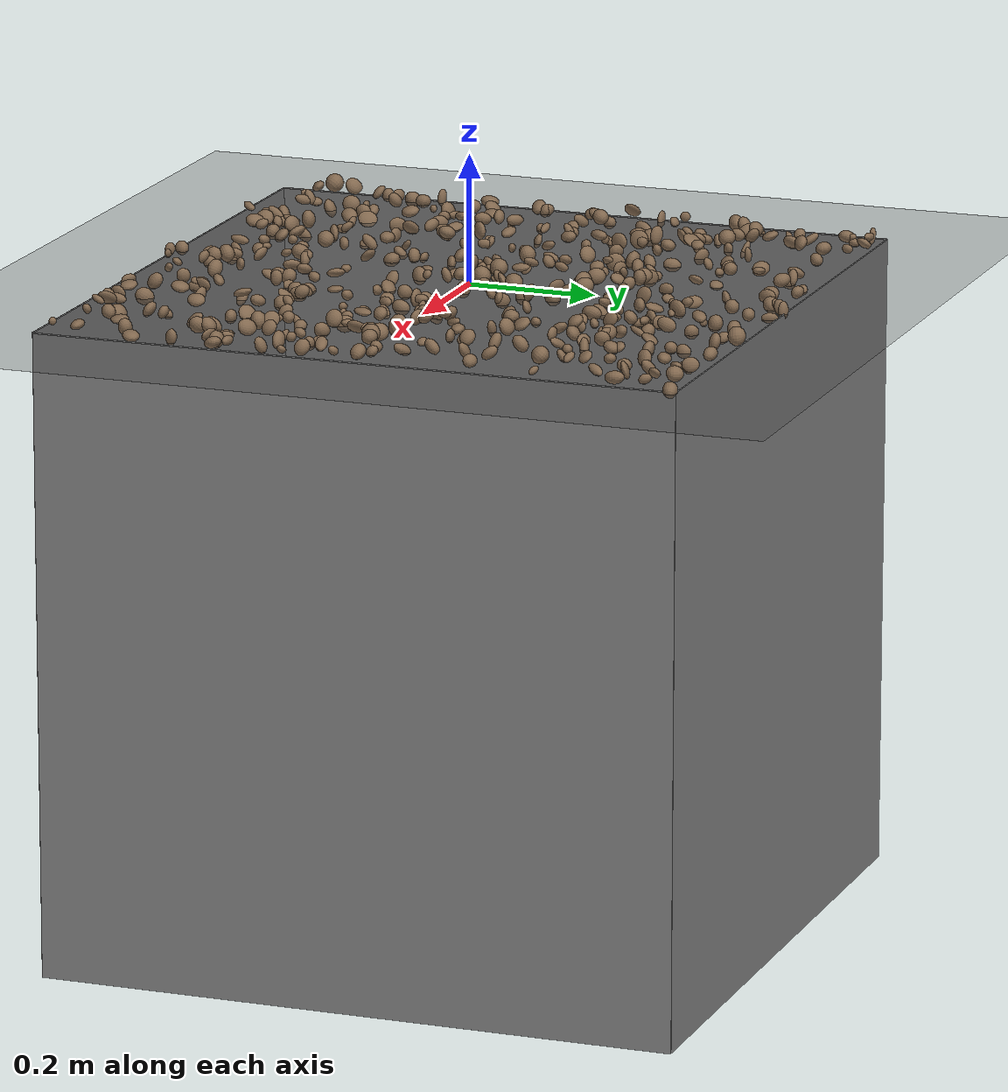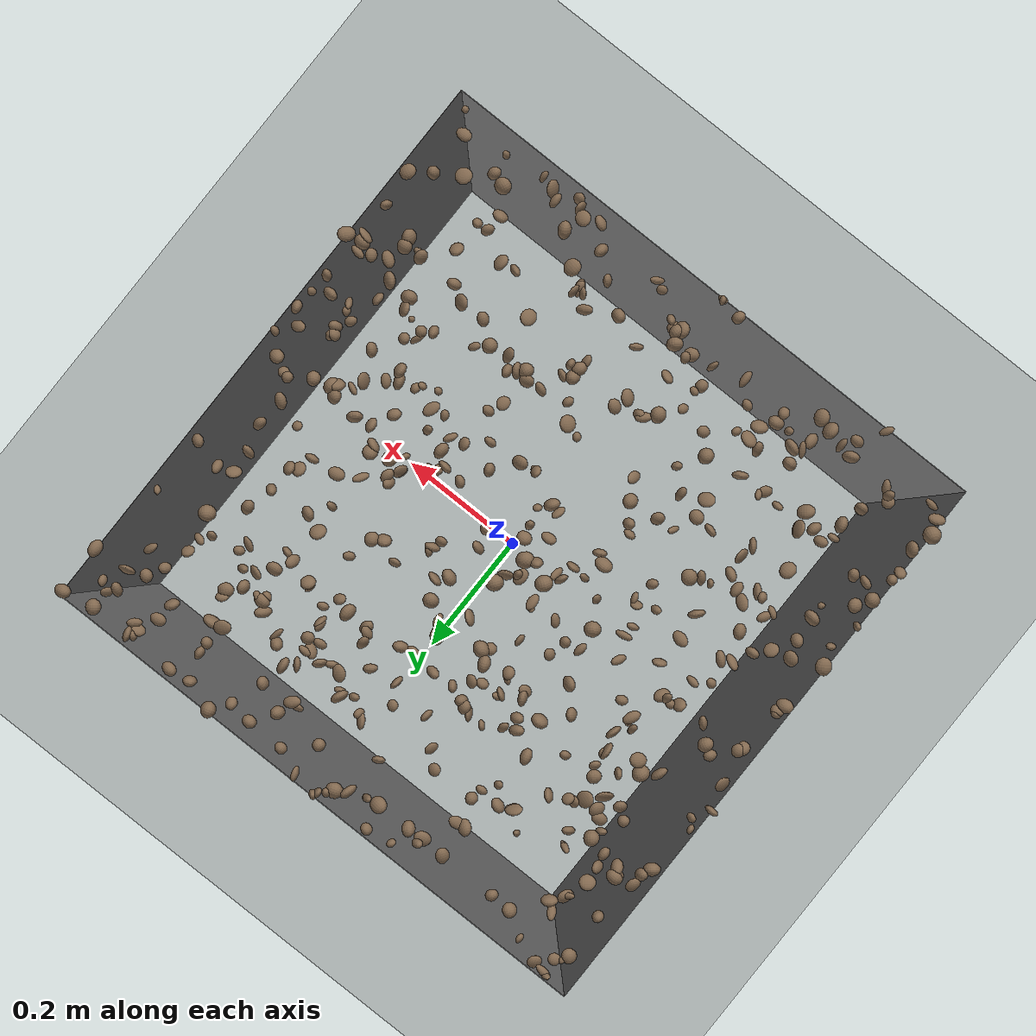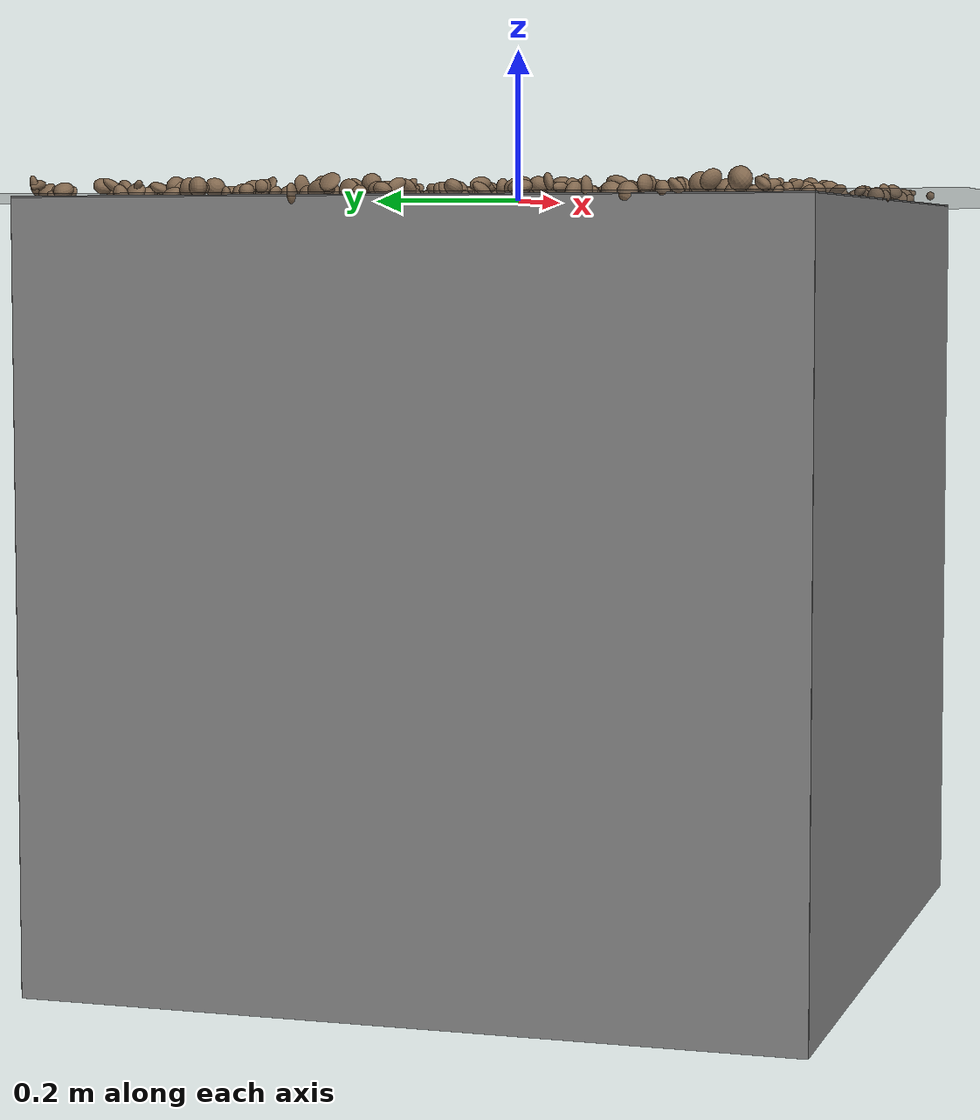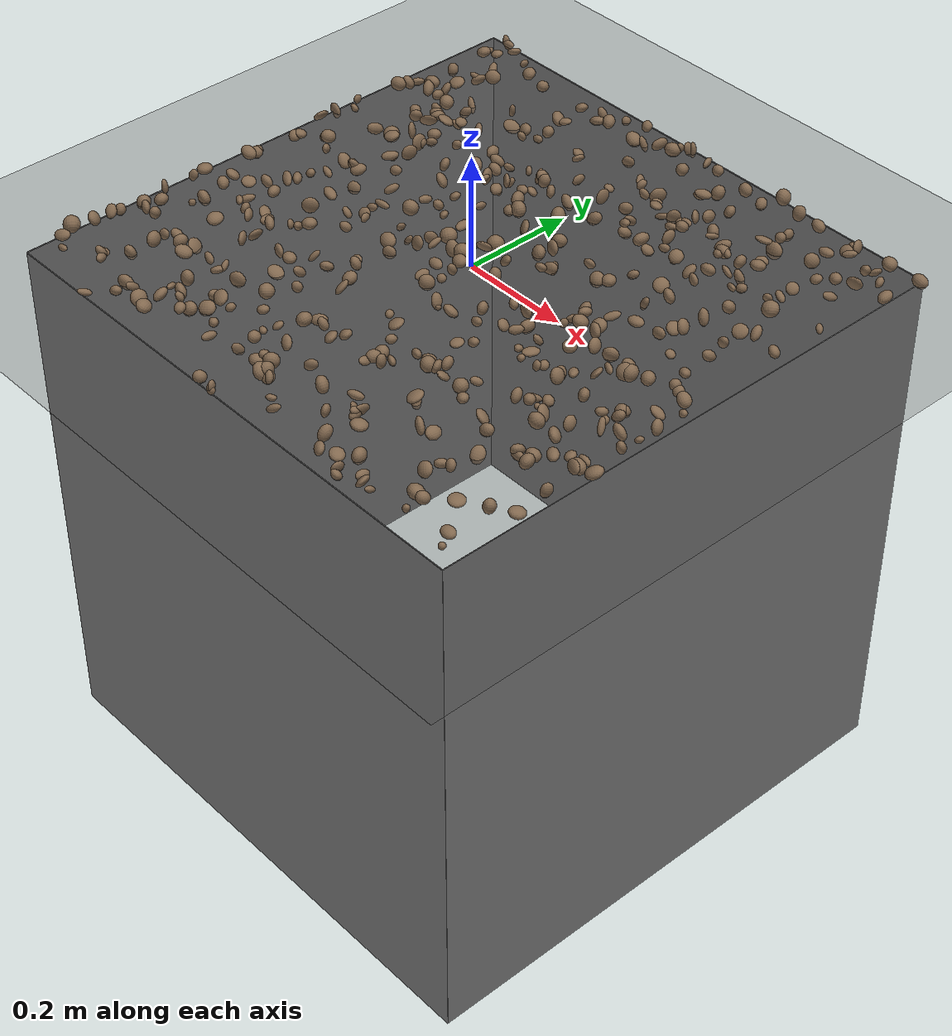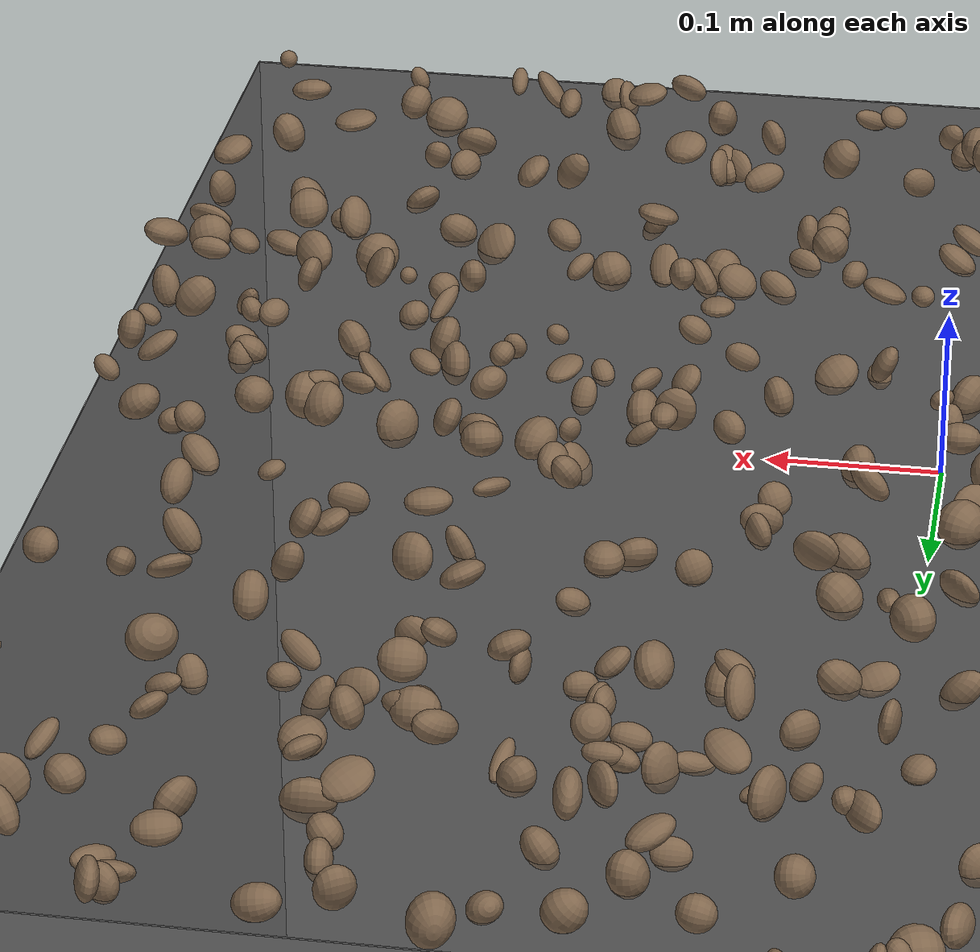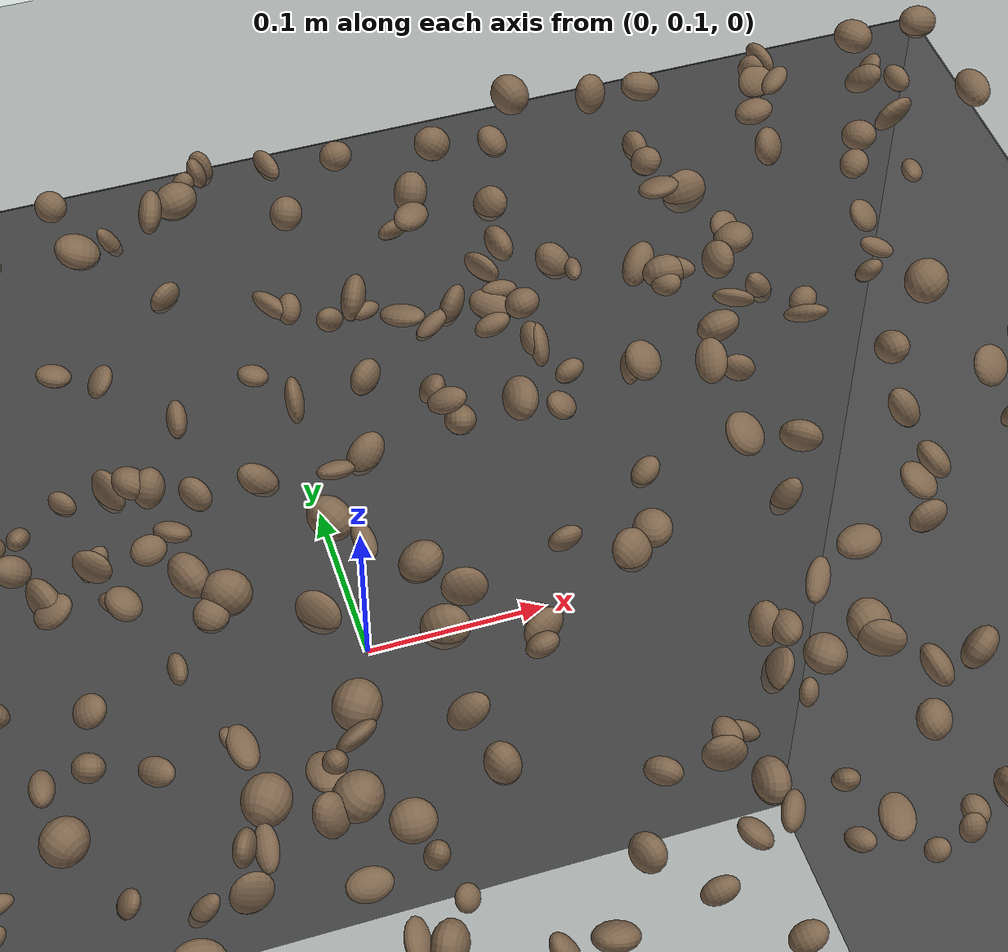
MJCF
<mujoco model="rocky_terrain_scene">
    <compiler angle="radian" inertiafromgeom="true" />
    <option timestep="0.002" gravity="0 0 -9.81" />

    <worldbody>
        <light name="sunlight" pos="5 5 5" dir="-1 -1 -1" diffuse="1 1 1" specular="0.5 0.5 0.5" ambient="0.5 0.5 0.5" />

        <geom name="ground_plane" type="plane" size="50 50 0.1" rgba="0.3 0.3 0.3 1" />

        <body name="rocky_terrain_body">

        </body>
    <body name="rock1" pos="-0.08270307679511935 -0.19609366114369275 0.009819770924032488"><joint type="free" damping="5" armature="0.01" /><geom type="ellipsoid" size="0.014554696461839163 0.005511062293659936 0.009125022048223169" quat="0.27044280948985394 0.3395529119257742 0.04375424636395662 0.3462500322204153" rgba="0.5 0.4 0.3 1" friction="0.01 0.01 0.01" solref="0.002 1" solimp="0.4 0.4 0.001" /><inertial pos="-0.08270307679511935 -0.19609366114369275 0.009819770924032488" quat="0.27044280948985394 0.3395529119257742 0.04375424636395662 0.3462500322204153" mass="0.2691671632566646" diaginertia="0.1 0.1 0.1" /></body><body name="rock2" pos="0.04442889703092223 0.10276441327152808 0.0009371384172825608"><joint type="free" damping="5" armature="0.01" /><geom type="ellipsoid" size="0.010184453734835792 0.013188407084801353 0.01475369386920029" quat="0.44954251815282315 0.15561983454446626 0.17248352757022928 0.22235411973248134" rgba="0.5 0.4 0.3 1" friction="0.01 0.01 0.01" solref="0.002 1" solimp="0.4 0.4 0.001" /><inertial pos="0.04442889703092223 0.10276441327152808 0.0009371384172825608" quat="0.44954251815282315 0.15561983454446626 0.17248352757022928 0.22235411973248134" mass="0.11144767862005885" diaginertia="0.1 0.1 0.1" /></body><body name="rock3" pos="0.15798427075579224 -0.37047559220674664 0.00706733023078233"><joint type="free" damping="5" armature="0.01" /><geom type="ellipsoid" size="0.005022704628891586 0.009788094928401173 0.0124069451385255" quat="0.36551993282791684 0.3226886980695813 0.05646114267495865 0.25533022642754327" rgba="0.5 0.4 0.3 1" friction="0.01 0.01 0.01" solref="0.002 1" solimp="0.4 0.4 0.001" /><inertial pos="0.15798427075579224 -0.37047559220674664 0.00706733023078233" quat="0.36551993282791684 0.3226886980695813 0.05646114267495865 0.25533022642754327" mass="0.23273347673324693" diaginertia="0.1 0.1 0.1" /></body><body name="rock4" pos="-0.3263099389489662 -0.4309255830562627 0.0013970234581078106"><joint type="free" damping="5" armature="0.01" /><geom type="ellipsoid" size="0.009083646040159921 0.012802637804985712 0.014542511185886876" quat="0.07779774849784551 0.3032058094325799 0.43098448750541557 0.18801195456415892" rgba="0.5 0.4 0.3 1" friction="0.01 0.01 0.01" solref="0.002 1" solimp="0.4 0.4 0.001" /><inertial pos="-0.3263099389489662 -0.4309255830562627 0.0013970234581078106" quat="0.07779774849784551 0.3032058094325799 0.43098448750541557 0.18801195456415892" mass="0.2071439080940808" diaginertia="0.1 0.1 0.1" /></body><body name="rock5" pos="0.01360067417976718 -0.41657304838826315 0.0034453484576177956"><joint type="free" damping="5" armature="0.01" /><geom type="ellipsoid" size="0.010995059597169909 0.010179683020024899 0.00915161964382423" quat="0.2606953568714224 0.3043884445580445 0.0948247942049608 0.3400914043655722" rgba="0.5 0.4 0.3 1" friction="0.01 0.01 0.01" solref="0.002 1" solimp="0.4 0.4 0.001" /><inertial pos="0.01360067417976718 -0.41657304838826315 0.0034453484576177956" quat="0.2606953568714224 0.3043884445580445 0.0948247942049608 0.3400914043655722" mass="0.4716749893885034" diaginertia="0.1 0.1 0.1" /></body><body name="rock6" pos="0.16807067745550253 0.4104359674342418 0.0022915554603001012"><joint type="free" damping="5" armature="0.01" /><geom type="ellipsoid" size="0.010822292286910593 0.008662465259789498 0.011938821974468198" quat="0.28520391177774257 0.1828298058139202 0.040891484139887226 0.49107479826845" rgba="0.5 0.4 0.3 1" friction="0.01 0.01 0.01" solref="0.002 1" solimp="0.4 0.4 0.001" /><inertial pos="0.16807067745550253 0.4104359674342418 0.0022915554603001012" quat="0.28520391177774257 0.1828298058139202 0.040891484139887226 0.49107479826845" mass="0.43620269748407836" diaginertia="0.1 0.1 0.1" /></body><body name="rock7" pos="-0.06436747067697157 0.23093025300501335 0.006134492886656709"><joint type="free" damping="5" armature="0.01" /><geom type="ellipsoid" size="0.009915060384066445 0.01114514305325828 0.0068680925611015785" quat="0.2607146124342 0.024999296416444453 0.4292617537980045 0.2850243373513511" rgba="0.5 0.4 0.3 1" friction="0.01 0.01 0.01" solref="0.002 1" solimp="0.4 0.4 0.001" /><inertial pos="-0.06436747067697157 0.23093025300501335 0.006134492886656709" quat="0.2607146124342 0.024999296416444453 0.4292617537980045 0.2850243373513511" mass="0.36101478564946177" diaginertia="0.1 0.1 0.1" /></body><body name="rock8" pos="0.47461581402351727 -0.4781520615642332 0.012985627254404582"><joint type="free" damping="5" armature="0.01" /><geom type="ellipsoid" size="0.005818718811240489 0.005694875733047591 0.005781972634693311" quat="0.21403066392747624 0.037355017293420945 0.09165568096642894 0.6569586378126738" rgba="0.5 0.4 0.3 1" friction="0.01 0.01 0.01" solref="0.002 1" solimp="0.4 0.4 0.001" /><inertial pos="0.47461581402351727 -0.4781520615642332 0.012985627254404582" quat="0.21403066392747624 0.037355017293420945 0.09165568096642894 0.6569586378126738" mass="0.15580805303900905" diaginertia="0.1 0.1 0.1" /></body><body name="rock9" pos="-0.2627074303434681 -0.41156912593498307 0.0032977480409563456"><joint type="free" damping="5" armature="0.01" /><geom type="ellipsoid" size="0.013952139658810588 0.008007536816425858 0.010225810482427926" quat="0.3052297977977795 0.23004559261298801 0.09252086758096273 0.3722037420082698" rgba="0.5 0.4 0.3 1" friction="0.01 0.01 0.01" solref="0.002 1" solimp="0.4 0.4 0.001" /><inertial pos="-0.2627074303434681 -0.41156912593498307 0.0032977480409563456" quat="0.3052297977977795 0.23004559261298801 0.09252086758096273 0.3722037420082698" mass="0.44841313890648826" diaginertia="0.1 0.1 0.1" /></body><body name="rock10" pos="-0.3986461596539388 0.13768371463373863 0.009034086035439029"><joint type="free" damping="5" armature="0.01" /><geom type="ellipsoid" size="0.009922229418822275 0.014921689080682202 0.007149435584350303" quat="0.15064845185204243 0.3943488449525959 0.019211813142535908 0.43579089005282573" rgba="0.5 0.4 0.3 1" friction="0.01 0.01 0.01" solref="0.002 1" solimp="0.4 0.4 0.001" /><inertial pos="-0.3986461596539388 0.13768371463373863 0.009034086035439029" quat="0.15064845185204243 0.3943488449525959 0.019211813142535908 0.43579089005282573" mass="0.23303375689458541" diaginertia="0.1 0.1 0.1" /></body><body name="rock11" pos="-0.19546389058045022 0.3479350206791234 0.009302333200409197"><joint type="free" damping="5" armature="0.01" /><geom type="ellipsoid" size="0.010585434505114634 0.009741175163325694 0.010309364261786334" quat="0.31799343505446187 0.26162613964136633 0.027103739963544166 0.39327668534062776" rgba="0.5 0.4 0.3 1" friction="0.01 0.01 0.01" solref="0.002 1" solimp="0.4 0.4 0.001" /><inertial pos="-0.19546389058045022 0.3479350206791234 0.009302333200409197" quat="0.31799343505446187 0.26162613964136633 0.027103739963544166 0.39327668534062776" mass="0.4700777386835736" diaginertia="0.1 0.1 0.1" /></body><body name="rock12" pos="0.3556946786839129 0.43317334297889076 0.009932411185830143"><joint type="free" damping="5" armature="0.01" /><geom type="ellipsoid" size="0.007917451491695902 0.010165265695964591 0.013031759127785592" quat="0.014906021258142466 0.43529467467513566 0.1189616249582258 0.4308376791084961" rgba="0.5 0.4 0.3 1" friction="0.01 0.01 0.01" solref="0.002 1" solimp="0.4 0.4 0.001" /><inertial pos="0.3556946786839129 0.43317334297889076 0.009932411185830143" quat="0.014906021258142466 0.43529467467513566 0.1189616249582258 0.4308376791084961" mass="0.2347037364952215" diaginertia="0.1 0.1 0.1" /></body><body name="rock13" pos="-0.2931251832641327 -0.1724305760823821 0.012082481801068303"><joint type="free" damping="5" armature="0.01" /><geom type="ellipsoid" size="0.01328096917895549 0.009289970455428703 0.007711610694859941" quat="0.02744557871462412 0.18887984572590916 0.3784704952980292 0.40520408026143756" rgba="0.5 0.4 0.3 1" friction="0.01 0.01 0.01" solref="0.002 1" solimp="0.4 0.4 0.001" /><inertial pos="-0.2931251832641327 -0.1724305760823821 0.012082481801068303" quat="0.02744557871462412 0.18887984572590916 0.3784704952980292 0.40520408026143756" mass="0.269599471292305" diaginertia="0.1 0.1 0.1" /></body><body name="rock14" pos="0.09506027803232875 0.08807423502691958 0.004326685663164983"><joint type="free" damping="5" armature="0.01" /><geom type="ellipsoid" size="0.006280976846910199 0.011473646424891983 0.011129104661510549" quat="0.48093153890310697 0.2797474426461168 0.11386386276397846 0.12545715568679772" rgba="0.5 0.4 0.3 1" friction="0.01 0.01 0.01" solref="0.002 1" solimp="0.4 0.4 0.001" /><inertial pos="0.09506027803232875 0.08807423502691958 0.004326685663164983" quat="0.48093153890310697 0.2797474426461168 0.11386386276397846 0.12545715568679772" mass="0.47700541064617075" diaginertia="0.1 0.1 0.1" /></body><body name="rock15" pos="0.14800176181245261 0.3303843990937718 0.008319873858315544"><joint type="free" damping="5" armature="0.01" /><geom type="ellipsoid" size="0.006050690439903223 0.006322947502610247 0.011156850884219551" quat="0.1236585916945242 0.39271979440076304 0.09677256808791693 0.3868490458167958" rgba="0.5 0.4 0.3 1" friction="0.01 0.01 0.01" solref="0.002 1" solimp="0.4 0.4 0.001" /><inertial pos="0.14800176181245261 0.3303843990937718 0.008319873858315544" quat="0.1236585916945242 0.39271979440076304 0.09677256808791693 0.3868490458167958" mass="0.1622506697178943" diaginertia="0.1 0.1 0.1" /></body><body name="rock16" pos="0.03627083402913378 0.23347229004981296 0.002840569623211413"><joint type="free" damping="5" armature="0.01" /><geom type="ellipsoid" size="0.008932892721695188 0.014105054079351396 0.010453245579397473" quat="0.12565104165855753 0.278685761506679 0.4328364423784312 0.16282675445633224" rgba="0.5 0.4 0.3 1" friction="0.01 0.01 0.01" solref="0.002 1" solimp="0.4 0.4 0.001" /><inertial pos="0.03627083402913378 0.23347229004981296 0.002840569623211413" quat="0.12565104165855753 0.278685761506679 0.4328364423784312 0.16282675445633224" mass="0.4643889542555698" diaginertia="0.1 0.1 0.1" /></body><body name="rock17" pos="0.08520957817027297 0.32413767819584316 0.012154932524371425"><joint type="free" damping="5" armature="0.01" /><geom type="ellipsoid" size="0.010733043542316656 0.005804310446774423 0.014881010766358567" quat="0.43961163534671444 0.2903161864207412 0.16903874885002662 0.10103342938251786" rgba="0.5 0.4 0.3 1" friction="0.01 0.01 0.01" solref="0.002 1" solimp="0.4 0.4 0.001" /><inertial pos="0.08520957817027297 0.32413767819584316 0.012154932524371425" quat="0.43961163534671444 0.2903161864207412 0.16903874885002662 0.10103342938251786" mass="0.14889799643064144" diaginertia="0.1 0.1 0.1" /></body><body name="rock18" pos="-0.4897687511349538 -0.43720109460660495 0.009341026635446005"><joint type="free" damping="5" armature="0.01" /><geom type="ellipsoid" size="0.010167410527869784 0.0068588229901650295 0.014198311780541074" quat="0.0967448323949887 0.2659310843190377 0.23031613717221272 0.40700794611376084" rgba="0.5 0.4 0.3 1" friction="0.01 0.01 0.01" solref="0.002 1" solimp="0.4 0.4 0.001" /><inertial pos="-0.4897687511349538 -0.43720109460660495 0.009341026635446005" quat="0.0967448323949887 0.2659310843190377 0.23031613717221272 0.40700794611376084" mass="0.4173001038406263" diaginertia="0.1 0.1 0.1" /></body><body name="rock19" pos="-0.49438954871367746 -0.32131303588484716 0.0035879289613970277"><joint type="free" damping="5" armature="0.01" /><geom type="ellipsoid" size="0.008644288649299881 0.008854899891193957 0.010533233407199938" quat="0.08686538853740332 0.7398310653661783 0.171806188956531 0.001497357139887513" rgba="0.5 0.4 0.3 1" friction="0.01 0.01 0.01" solref="0.002 1" solimp="0.4 0.4 0.001" /><inertial pos="-0.49438954871367746 -0.32131303588484716 0.0035879289613970277" quat="0.08686538853740332 0.7398310653661783 0.171806188956531 0.001497357139887513" mass="0.3698775729085395" diaginertia="0.1 0.1 0.1" /></body><body name="rock20" pos="-0.20115781583031034 0.3913829413895 0.009066925476433793"><joint type="free" damping="5" armature="0.01" /><geom type="ellipsoid" size="0.009680848360609912 0.013970247674830488 0.005291857979580197" quat="0.04900962127920993 0.41073294071571137 0.48038980976811235 0.05986762823696632" rgba="0.5 0.4 0.3 1" friction="0.01 0.01 0.01" solref="0.002 1" solimp="0.4 0.4 0.001" /><inertial pos="-0.20115781583031034 0.3913829413895 0.009066925476433793" quat="0.04900962127920993 0.41073294071571137 0.48038980976811235 0.05986762823696632" mass="0.24139331117815246" diaginertia="0.1 0.1 0.1" /></body><body name="rock21" pos="-0.35644137741146253 0.03507866888787092 0.00918721446950069"><joint type="free" damping="5" armature="0.01" /><geom type="ellipsoid" size="0.010856015043585718 0.014065886352884641 0.006891137351346463" quat="0.3622026545476415 0.1847427348164458 0.14117515454664759 0.3118794560892651" rgba="0.5 0.4 0.3 1" friction="0.01 0.01 0.01" solref="0.002 1" solimp="0.4 0.4 0.001" /><inertial pos="-0.35644137741146253 0.03507866888787092 0.00918721446950069" quat="0.3622026545476415 0.1847427348164458 0.14117515454664759 0.3118794560892651" mass="0.48893463942356574" diaginertia="0.1 0.1 0.1" /></body><body name="rock22" pos="-0.15859509147867434 0.06931946990089422 0.0050468028746207"><joint type="free" damping="5" armature="0.01" /><geom type="ellipsoid" size="0.011075014303928522 0.007964662839269148 0.00884797282453054" quat="0.34431877634876523 0.15422799386312042 0.41869298439073355 0.08276024539738079" rgba="0.5 0.4 0.3 1" friction="0.01 0.01 0.01" solref="0.002 1" solimp="0.4 0.4 0.001" /><inertial pos="-0.15859509147867434 0.06931946990089422 0.0050468028746207" quat="0.34431877634876523 0.15422799386312042 0.41869298439073355 0.08276024539738079" mass="0.39435093847317815" diaginertia="0.1 0.1 0.1" /></body><body name="rock23" pos="0.008782706670323437 -0.26387498793697284 0.003719217939757041"><joint type="free" damping="5" armature="0.01" /><geom type="ellipsoid" size="0.013233604934121807 0.010783632419918726 0.007516187458868483" quat="0.19095801159188022 0.08594205977886618 0.6291323253987912 0.0939676032304625" rgba="0.5 0.4 0.3 1" friction="0.01 0.01 0.01" solref="0.002 1" solimp="0.4 0.4 0.001" /><inertial pos="0.008782706670323437 -0.26387498793697284 0.003719217939757041" quat="0.19095801159188022 0.08594205977886618 0.6291323253987912 0.0939676032304625" mass="0.2260442523425736" diaginertia="0.1 0.1 0.1" /></body><body name="rock24" pos="0.25474351866257416 0.12967732894270445 0.0031840375770663923"><joint type="free" damping="5" armature="0.01" /><geom type="ellipsoid" size="0.005741698592188225 0.00731786908255596 0.014242158438350774" quat="0.5271790312051813 0.06553131750880226 0.11148717774117443 0.29580247354484207" rgba="0.5 0.4 0.3 1" friction="0.01 0.01 0.01" solref="0.002 1" solimp="0.4 0.4 0.001" /><inertial pos="0.25474351866257416 0.12967732894270445 0.0031840375770663923" quat="0.5271790312051813 0.06553131750880226 0.11148717774117443 0.29580247354484207" mass="0.4185269799754143" diaginertia="0.1 0.1 0.1" /></body><body name="rock25" pos="-0.4980156017813495 -0.4128744650300741 0.014776459378101051"><joint type="free" damping="5" armature="0.01" /><geom type="ellipsoid" size="0.014250762434828281 0.014714622149043267 0.014385238089355462" quat="0.2223356870308603 0.38460349101216734 0.335117783897653 0.057943038059319364" rgba="0.5 0.4 0.3 1" friction="0.01 0.01 0.01" solref="0.002 1" solimp="0.4 0.4 0.001" /><inertial pos="-0.4980156017813495 -0.4128744650300741 0.014776459378101051" quat="0.2223356870308603 0.38460349101216734 0.335117783897653 0.057943038059319364" mass="0.2950285388967373" diaginertia="0.1 0.1 0.1" /></body><body name="rock26" pos="0.07837004955321836 -0.4575390758602893 0.005448066367252578"><joint type="free" damping="5" armature="0.01" /><geom type="ellipsoid" size="0.005856957146544207 0.006320889902266083 0.012546908036782172" quat="0.2449943255875909 0.10949943631834648 0.25567595668152376 0.3898302814125387" rgba="0.5 0.4 0.3 1" friction="0.01 0.01 0.01" solref="0.002 1" solimp="0.4 0.4 0.001" /><inertial pos="0.07837004955321836 -0.4575390758602893 0.005448066367252578" quat="0.2449943255875909 0.10949943631834648 0.25567595668152376 0.3898302814125387" mass="0.3491904640746709" diaginertia="0.1 0.1 0.1" /></body><body name="rock27" pos="-0.2529246824795963 -0.44988656356134515 0.005404131895539714"><joint type="free" damping="5" armature="0.01" /><geom type="ellipsoid" size="0.014410434811434374 0.009142116353442968 0.012561844495353202" quat="0.1698867002458738 0.22084983391416857 0.3942235533610658 0.21503991247889173" rgba="0.5 0.4 0.3 1" friction="0.01 0.01 0.01" solref="0.002 1" solimp="0.4 0.4 0.001" /><inertial pos="-0.2529246824795963 -0.44988656356134515 0.005404131895539714" quat="0.1698867002458738 0.22084983391416857 0.3942235533610658 0.21503991247889173" mass="0.3573556385105294" diaginertia="0.1 0.1 0.1" /></body><body name="rock28" pos="-0.2760588114987558 -0.44285763924072585 0.004515398670598296"><joint type="free" damping="5" armature="0.01" /><geom type="ellipsoid" size="0.014383198757196708 0.00974559930654223 0.013862481789556829" quat="0.07043045628816468 0.3631240946907742 0.4074851422313092 0.15896030678975184" rgba="0.5 0.4 0.3 1" friction="0.01 0.01 0.01" solref="0.002 1" solimp="0.4 0.4 0.001" /><inertial pos="-0.2760588114987558 -0.44285763924072585 0.004515398670598296" quat="0.07043045628816468 0.3631240946907742 0.4074851422313092 0.15896030678975184" mass="0.18344018436267695" diaginertia="0.1 0.1 0.1" /></body><body name="rock29" pos="0.0003534463754618633 0.49666985380062856 0.0029981846785954408"><joint type="free" damping="5" armature="0.01" /><geom type="ellipsoid" size="0.008156709055036824 0.014206970169932269 0.006105527026504769" quat="0.14075941630603456 0.1306199251704386 0.36299482028795915 0.3656258382355677" rgba="0.5 0.4 0.3 1" friction="0.01 0.01 0.01" solref="0.002 1" solimp="0.4 0.4 0.001" /><inertial pos="0.0003534463754618633 0.49666985380062856 0.0029981846785954408" quat="0.14075941630603456 0.1306199251704386 0.36299482028795915 0.3656258382355677" mass="0.3325007126730105" diaginertia="0.1 0.1 0.1" /></body><body name="rock30" pos="-0.38475462335695065 0.26341656108474576 0.002393045368894421"><joint type="free" damping="5" armature="0.01" /><geom type="ellipsoid" size="0.005895912112070341 0.011263420796125183 0.007700612027845067" quat="0.23122242216096603 0.10113464639117037 0.23541197227482327 0.43223095917304033" rgba="0.5 0.4 0.3 1" friction="0.01 0.01 0.01" solref="0.002 1" solimp="0.4 0.4 0.001" /><inertial pos="-0.38475462335695065 0.26341656108474576 0.002393045368894421" quat="0.23122242216096603 0.10113464639117037 0.23541197227482327 0.43223095917304033" mass="0.28467735219138157" diaginertia="0.1 0.1 0.1" /></body><body name="rock31" pos="0.005450586937512214 -0.4136045969842458 0.011820165101859839"><joint type="free" damping="5" armature="0.01" /><geom type="ellipsoid" size="0.012515531921463187 0.013639618388419018 0.010913400565569002" quat="0.33820485132122996 0.22677090785470305 0.3040996563659345 0.13092458445813246" rgba="0.5 0.4 0.3 1" friction="0.01 0.01 0.01" solref="0.002 1" solimp="0.4 0.4 0.001" /><inertial pos="0.005450586937512214 -0.4136045969842458 0.011820165101859839" quat="0.33820485132122996 0.22677090785470305 0.3040996563659345 0.13092458445813246" mass="0.2235148924704991" diaginertia="0.1 0.1 0.1" /></body><body name="rock32" pos="0.2852802902364202 -0.006594479792609964 0.008422595738020053"><joint type="free" damping="5" armature="0.01" /><geom type="ellipsoid" size="0.011514473600161968 0.01296854311944651 0.007264276169764094" quat="0.423070607763964 0.10038588312963274 0.2845615463841715 0.19198196272223186" rgba="0.5 0.4 0.3 1" friction="0.01 0.01 0.01" solref="0.002 1" solimp="0.4 0.4 0.001" /><inertial pos="0.2852802902364202 -0.006594479792609964 0.008422595738020053" quat="0.423070607763964 0.10038588312963274 0.2845615463841715 0.19198196272223186" mass="0.4426080387740924" diaginertia="0.1 0.1 0.1" /></body><body name="rock33" pos="-0.4148967520412553 -0.41158051813586105 0.0029830810560769767"><joint type="free" damping="5" armature="0.01" /><geom type="ellipsoid" size="0.010106320134931294 0.010425161513920596 0.006186510742080594" quat="0.3632395621061269 0.010101092109833777 0.06624913049374241 0.5604102152902969" rgba="0.5 0.4 0.3 1" friction="0.01 0.01 0.01" solref="0.002 1" solimp="0.4 0.4 0.001" /><inertial pos="-0.4148967520412553 -0.41158051813586105 0.0029830810560769767" quat="0.3632395621061269 0.010101092109833777 0.06624913049374241 0.5604102152902969" mass="0.28372460345313466" diaginertia="0.1 0.1 0.1" /></body><body name="rock34" pos="0.46056822647745466 -0.12590839324167036 0.012470809733165729"><joint type="free" damping="5" armature="0.01" /><geom type="ellipsoid" size="0.008141648940957943 0.014576985354943457 0.010996846686466978" quat="0.3687238358346847 0.21624405257425033 0.08701691693446223 0.3280151946566027" rgba="0.5 0.4 0.3 1" friction="0.01 0.01 0.01" solref="0.002 1" solimp="0.4 0.4 0.001" /><inertial pos="0.46056822647745466 -0.12590839324167036 0.012470809733165729" quat="0.3687238358346847 0.21624405257425033 0.08701691693446223 0.3280151946566027" mass="0.15407554589316239" diaginertia="0.1 0.1 0.1" /></body><body name="rock35" pos="-0.36008023268657097 0.1414651807020143 0.011305459869227872"><joint type="free" damping="5" armature="0.01" /><geom type="ellipsoid" size="0.01365954109688653 0.0070714995260479615 0.012185217917986754" quat="0.3550330608775356 0.42490960357098073 0.06645900839535299 0.15359832715613064" rgba="0.5 0.4 0.3 1" friction="0.01 0.01 0.01" solref="0.002 1" solimp="0.4 0.4 0.001" /><inertial pos="-0.36008023268657097 0.1414651807020143 0.011305459869227872" quat="0.3550330608775356 0.42490960357098073 0.06645900839535299 0.15359832715613064" mass="0.4346364227324654" diaginertia="0.1 0.1 0.1" /></body><body name="rock36" pos="0.201568995010042 -0.47144340949474905 0.013651114589159982"><joint type="free" damping="5" armature="0.01" /><geom type="ellipsoid" size="0.01041008866103425 0.006956102662515606 0.012794574228193092" quat="0.21975995163462753 0.4049851140739828 0.02192716099167482 0.353327773299715" rgba="0.5 0.4 0.3 1" friction="0.01 0.01 0.01" solref="0.002 1" solimp="0.4 0.4 0.001" /><inertial pos="0.201568995010042 -0.47144340949474905 0.013651114589159982" quat="0.21975995163462753 0.4049851140739828 0.02192716099167482 0.353327773299715" mass="0.30802846200685274" diaginertia="0.1 0.1 0.1" /></body><body name="rock37" pos="0.2948436772251375 -0.24215005519754462 0.003493892526509962"><joint type="free" damping="5" armature="0.01" /><geom type="ellipsoid" size="0.006379288308334699 0.01353661368583934 0.013888121111578822" quat="0.10522994174213908 0.49318333803011233 0.15854225611414824 0.24304446411360037" rgba="0.5 0.4 0.3 1" friction="0.01 0.01 0.01" solref="0.002 1" solimp="0.4 0.4 0.001" /><inertial pos="0.2948436772251375 -0.24215005519754462 0.003493892526509962" quat="0.10522994174213908 0.49318333803011233 0.15854225611414824 0.24304446411360037" mass="0.15300761379934721" diaginertia="0.1 0.1 0.1" /></body><body name="rock38" pos="0.2843206901182025 -0.32780771479785287 0.01413519962002357"><joint type="free" damping="5" armature="0.01" /><geom type="ellipsoid" size="0.013742245689126596 0.007106109924066919 0.011317817613416624" quat="0.18120753723871083 0.3323288055090369 0.34220076903931623 0.14426288821293606" rgba="0.5 0.4 0.3 1" friction="0.01 0.01 0.01" solref="0.002 1" solimp="0.4 0.4 0.001" /><inertial pos="0.2843206901182025 -0.32780771479785287 0.01413519962002357" quat="0.18120753723871083 0.3323288055090369 0.34220076903931623 0.14426288821293606" mass="0.34425688103499785" diaginertia="0.1 0.1 0.1" /></body><body name="rock39" pos="0.09374767869620915 0.08178054713442329 0.007524058745583416"><joint type="free" damping="5" armature="0.01" /><geom type="ellipsoid" size="0.006940172781491415 0.010326213005407274 0.012702141172537547" quat="0.2830579622733728 0.1340258451862962 0.24745560363095206 0.3354605889093789" rgba="0.5 0.4 0.3 1" friction="0.01 0.01 0.01" solref="0.002 1" solimp="0.4 0.4 0.001" /><inertial pos="0.09374767869620915 0.08178054713442329 0.007524058745583416" quat="0.2830579622733728 0.1340258451862962 0.24745560363095206 0.3354605889093789" mass="0.45784556656167374" diaginertia="0.1 0.1 0.1" /></body><body name="rock40" pos="-0.03448313485556542 -0.40107645722763785 0.00016917558280019228"><joint type="free" damping="5" armature="0.01" /><geom type="ellipsoid" size="0.011214796366210303 0.010395309851132132 0.012380308540588976" quat="0.23784355212338618 0.15246938035419055 0.36283498122464375 0.2468520862977796" rgba="0.5 0.4 0.3 1" friction="0.01 0.01 0.01" solref="0.002 1" solimp="0.4 0.4 0.001" /><inertial pos="-0.03448313485556542 -0.40107645722763785 0.00016917558280019228" quat="0.23784355212338618 0.15246938035419055 0.36283498122464375 0.2468520862977796" mass="0.17951209500748067" diaginertia="0.1 0.1 0.1" /></body><body name="rock41" pos="0.3518283554158811 -0.30250468074427406 0.0009438338615430508"><joint type="free" damping="5" armature="0.01" /><geom type="ellipsoid" size="0.006905280598552752 0.014584415524493088 0.011361884613896419" quat="0.2699568372014519 0.032375614016288176 0.4665463996863386 0.2311211490959213" rgba="0.5 0.4 0.3 1" friction="0.01 0.01 0.01" solref="0.002 1" solimp="0.4 0.4 0.001" /><inertial pos="0.3518283554158811 -0.30250468074427406 0.0009438338615430508" quat="0.2699568372014519 0.032375614016288176 0.4665463996863386 0.2311211490959213" mass="0.4068193648255204" diaginertia="0.1 0.1 0.1" /></body><body name="rock42" pos="0.01667870506939484 0.16507616050990914 0.012539640428505212"><joint type="free" damping="5" armature="0.01" /><geom type="ellipsoid" size="0.012213352655584837 0.006227525656060181 0.006219253418276706" quat="0.1519273339568065 0.2969193562656326 0.27791551172362927 0.2732377980539316" rgba="0.5 0.4 0.3 1" friction="0.01 0.01 0.01" solref="0.002 1" solimp="0.4 0.4 0.001" /><inertial pos="0.01667870506939484 0.16507616050990914 0.012539640428505212" quat="0.1519273339568065 0.2969193562656326 0.27791551172362927 0.2732377980539316" mass="0.30122034117891494" diaginertia="0.1 0.1 0.1" /></body><body name="rock43" pos="0.1559772190408092 0.2346365580525125 0.0025789913544217806"><joint type="free" damping="5" armature="0.01" /><geom type="ellipsoid" size="0.01137682691442811 0.009254567163630226 0.006424568369592491" quat="0.5816696789553939 0.08432227903598122 0.21584343751002202 0.11816460449860282" rgba="0.5 0.4 0.3 1" friction="0.01 0.01 0.01" solref="0.002 1" solimp="0.4 0.4 0.001" /><inertial pos="0.1559772190408092 0.2346365580525125 0.0025789913544217806" quat="0.5816696789553939 0.08432227903598122 0.21584343751002202 0.11816460449860282" mass="0.33246911526135153" diaginertia="0.1 0.1 0.1" /></body><body name="rock44" pos="-0.12041364802872234 -0.027472092283530758 0.00018707533081819438"><joint type="free" damping="5" armature="0.01" /><geom type="ellipsoid" size="0.005805167068331645 0.00536524436479687 0.012694064791136998" quat="0.33100986501660545 0.1387351137952309 0.10699554563978994 0.42325947554837384" rgba="0.5 0.4 0.3 1" friction="0.01 0.01 0.01" solref="0.002 1" solimp="0.4 0.4 0.001" /><inertial pos="-0.12041364802872234 -0.027472092283530758 0.00018707533081819438" quat="0.33100986501660545 0.1387351137952309 0.10699554563978994 0.42325947554837384" mass="0.2950680456485032" diaginertia="0.1 0.1 0.1" /></body><body name="rock45" pos="-0.43685104370477623 -0.1560046147334132 0.010664129058915079"><joint type="free" damping="5" armature="0.01" /><geom type="ellipsoid" size="0.010318953645693584 0.009512414241059867 0.011909619647553549" quat="0.3170863647738445 0.2846314384981778 0.385688499710264 0.01259369701771378" rgba="0.5 0.4 0.3 1" friction="0.01 0.01 0.01" solref="0.002 1" solimp="0.4 0.4 0.001" /><inertial pos="-0.43685104370477623 -0.1560046147334132 0.010664129058915079" quat="0.3170863647738445 0.2846314384981778 0.385688499710264 0.01259369701771378" mass="0.402159707119489" diaginertia="0.1 0.1 0.1" /></body><body name="rock46" pos="-0.019210854996499216 0.13128508529458371 0.0032117520979821055"><joint type="free" damping="5" armature="0.01" /><geom type="ellipsoid" size="0.005841179587333861 0.012667908865305805 0.013896971751424788" quat="0.2880309201606155 0.4115287473485268 0.26020388776061604 0.04023644473024169" rgba="0.5 0.4 0.3 1" friction="0.01 0.01 0.01" solref="0.002 1" solimp="0.4 0.4 0.001" /><inertial pos="-0.019210854996499216 0.13128508529458371 0.0032117520979821055" quat="0.2880309201606155 0.4115287473485268 0.26020388776061604 0.04023644473024169" mass="0.27386915279806556" diaginertia="0.1 0.1 0.1" /></body><body name="rock47" pos="-0.1483684025943368 0.44518432016111975 0.010908965717489196"><joint type="free" damping="5" armature="0.01" /><geom type="ellipsoid" size="0.010553367290539382 0.010559251590007781 0.013316610446036575" quat="0.3395918616925749 0.39334789624415856 0.23099859947984805 0.03606164258341847" rgba="0.5 0.4 0.3 1" friction="0.01 0.01 0.01" solref="0.002 1" solimp="0.4 0.4 0.001" /><inertial pos="-0.1483684025943368 0.44518432016111975 0.010908965717489196" quat="0.3395918616925749 0.39334789624415856 0.23099859947984805 0.03606164258341847" mass="0.3045029168845712" diaginertia="0.1 0.1 0.1" /></body><body name="rock48" pos="-0.09315877074794432 -0.0029401169147229567 0.007253252662804227"><joint type="free" damping="5" armature="0.01" /><geom type="ellipsoid" size="0.014904026750462436 0.010303220136774654 0.0060313546667159715" quat="0.40079905733247007 0.2015028093284683 0.3780023695558683 0.01969576378319327" rgba="0.5 0.4 0.3 1" friction="0.01 0.01 0.01" solref="0.002 1" solimp="0.4 0.4 0.001" /><inertial pos="-0.09315877074794432 -0.0029401169147229567 0.007253252662804227" quat="0.40079905733247007 0.2015028093284683 0.3780023695558683 0.01969576378319327" mass="0.2811644107998801" diaginertia="0.1 0.1 0.1" /></body><body name="rock49" pos="-0.49630827660890264 -0.23108225009189665 0.006295269112786374"><joint type="free" damping="5" armature="0.01" /><geom type="ellipsoid" size="0.007283371822078692 0.013653579370493572 0.005402743984038706" quat="0.16882769378993645 0.10514144435723155 0.36229463126527167 0.3637362305875603" rgba="0.5 0.4 0.3 1" friction="0.01 0.01 0.01" solref="0.002 1" solimp="0.4 0.4 0.001" /><inertial pos="-0.49630827660890264 -0.23108225009189665 0.006295269112786374" quat="0.16882769378993645 0.10514144435723155 0.36229463126527167 0.3637362305875603" mass="0.29795423834191803" diaginertia="0.1 0.1 0.1" /></body><body name="rock50" pos="0.024923721366335916 -0.1899469422200527 0.01450112965639538"><joint type="free" damping="5" armature="0.01" /><geom type="ellipsoid" size="0.0067198835930580335 0.007763801089816691 0.006251746040480521" quat="0.6798852896416939 0.004691727853899485 0.08488442706399478 0.23053855544041188" rgba="0.5 0.4 0.3 1" friction="0.01 0.01 0.01" solref="0.002 1" solimp="0.4 0.4 0.001" /><inertial pos="0.024923721366335916 -0.1899469422200527 0.01450112965639538" quat="0.6798852896416939 0.004691727853899485 0.08488442706399478 0.23053855544041188" mass="0.26037161106669304" diaginertia="0.1 0.1 0.1" /></body><body name="rock51" pos="0.4246478820286025 -0.12071122407241908 0.008990978315343026"><joint type="free" damping="5" armature="0.01" /><geom type="ellipsoid" size="0.007949557339885543 0.007976572758779662 0.006362965868815903" quat="0.20860247261411377 0.14198986522719506 0.39256434305714527 0.2568433191015459" rgba="0.5 0.4 0.3 1" friction="0.01 0.01 0.01" solref="0.002 1" solimp="0.4 0.4 0.001" /><inertial pos="0.4246478820286025 -0.12071122407241908 0.008990978315343026" quat="0.20860247261411377 0.14198986522719506 0.39256434305714527 0.2568433191015459" mass="0.33667277042923205" diaginertia="0.1 0.1 0.1" /></body><body name="rock52" pos="0.3534324684264596 0.4020780640705083 0.00676181359904292"><joint type="free" damping="5" armature="0.01" /><geom type="ellipsoid" size="0.00804209943704225 0.012380754965997276 0.013225110243816954" quat="0.14352674154978495 0.12791453639380643 0.5518021384498057 0.17675658360660293" rgba="0.5 0.4 0.3 1" friction="0.01 0.01 0.01" solref="0.002 1" solimp="0.4 0.4 0.001" /><inertial pos="0.3534324684264596 0.4020780640705083 0.00676181359904292" quat="0.14352674154978495 0.12791453639380643 0.5518021384498057 0.17675658360660293" mass="0.15451152324824566" diaginertia="0.1 0.1 0.1" /></body><body name="rock53" pos="0.413195737765109 -0.3969354374274503 0.0090882006877938"><joint type="free" damping="5" armature="0.01" /><geom type="ellipsoid" size="0.013699274494338831 0.013601367287762574 0.005746587094806995" quat="0.6218531503716329 0.03258846369740215 0.03730453603516406 0.30825384989580085" rgba="0.5 0.4 0.3 1" friction="0.01 0.01 0.01" solref="0.002 1" solimp="0.4 0.4 0.001" /><inertial pos="0.413195737765109 -0.3969354374274503 0.0090882006877938" quat="0.6218531503716329 0.03258846369740215 0.03730453603516406 0.30825384989580085" mass="0.3510172385322091" diaginertia="0.1 0.1 0.1" /></body><body name="rock54" pos="0.3150022800347543 -0.16805868631203413 0.008696451750608646"><joint type="free" damping="5" armature="0.01" /><geom type="ellipsoid" size="0.009483016876145379 0.009238161255820172 0.00936338770761139" quat="0.17726891540631323 0.0336987409429848 0.4113050592856074 0.37772728436509456" rgba="0.5 0.4 0.3 1" friction="0.01 0.01 0.01" solref="0.002 1" solimp="0.4 0.4 0.001" /><inertial pos="0.3150022800347543 -0.16805868631203413 0.008696451750608646" quat="0.17726891540631323 0.0336987409429848 0.4113050592856074 0.37772728436509456" mass="0.3387264855973141" diaginertia="0.1 0.1 0.1" /></body><body name="rock55" pos="-0.4456638371616093 0.3025973656689612 0.009724110671381181"><joint type="free" damping="5" armature="0.01" /><geom type="ellipsoid" size="0.010771899992003352 0.011405249029040693 0.009732653487258953" quat="0.20632135918333974 0.3158437311273751 0.45703149096486406 0.020803418724421055" rgba="0.5 0.4 0.3 1" friction="0.01 0.01 0.01" solref="0.002 1" solimp="0.4 0.4 0.001" /><inertial pos="-0.4456638371616093 0.3025973656689612 0.009724110671381181" quat="0.20632135918333974 0.3158437311273751 0.45703149096486406 0.020803418724421055" mass="0.38994614011468665" diaginertia="0.1 0.1 0.1" /></body><body name="rock56" pos="0.002470492708054439 0.18437843845771007 0.014438844262520607"><joint type="free" damping="5" armature="0.01" /><geom type="ellipsoid" size="0.01435897130434569 0.0128827364274413 0.011558781402823022" quat="0.1371694227265431 0.20759088829517847 0.30069542223356094 0.35454426674471745" rgba="0.5 0.4 0.3 1" friction="0.01 0.01 0.01" solref="0.002 1" solimp="0.4 0.4 0.001" /><inertial pos="0.002470492708054439 0.18437843845771007 0.014438844262520607" quat="0.1371694227265431 0.20759088829517847 0.30069542223356094 0.35454426674471745" mass="0.1884781344760752" diaginertia="0.1 0.1 0.1" /></body><body name="rock57" pos="-0.2898224336296594 -0.09161631805694193 0.01083707436168996"><joint type="free" damping="5" armature="0.01" /><geom type="ellipsoid" size="0.01443461295088215 0.01406746715076897 0.006644896105349582" quat="0.274529925067787 0.41227941819861036 0.005935580902673531 0.3072550758309291" rgba="0.5 0.4 0.3 1" friction="0.01 0.01 0.01" solref="0.002 1" solimp="0.4 0.4 0.001" /><inertial pos="-0.2898224336296594 -0.09161631805694193 0.01083707436168996" quat="0.274529925067787 0.41227941819861036 0.005935580902673531 0.3072550758309291" mass="0.4243884701060975" diaginertia="0.1 0.1 0.1" /></body><body name="rock58" pos="0.34273238467250944 0.12415315381427783 0.010632933965980815"><joint type="free" damping="5" armature="0.01" /><geom type="ellipsoid" size="0.011187290728404544 0.012939980544735285 0.00748085406004179" quat="0.36637140828159553 0.12878780423043076 0.23069696998569608 0.2741438175022776" rgba="0.5 0.4 0.3 1" friction="0.01 0.01 0.01" solref="0.002 1" solimp="0.4 0.4 0.001" /><inertial pos="0.34273238467250944 0.12415315381427783 0.010632933965980815" quat="0.36637140828159553 0.12878780423043076 0.23069696998569608 0.2741438175022776" mass="0.35968970785772514" diaginertia="0.1 0.1 0.1" /></body><body name="rock59" pos="0.23981492095613977 -0.4296862799050155 0.0002388218308024731"><joint type="free" damping="5" armature="0.01" /><geom type="ellipsoid" size="0.010737511352865 0.013201967349511439 0.014809133954959183" quat="0.5312687764883113 0.27515750123867694 0.08222717596677175 0.11134654630623998" rgba="0.5 0.4 0.3 1" friction="0.01 0.01 0.01" solref="0.002 1" solimp="0.4 0.4 0.001" /><inertial pos="0.23981492095613977 -0.4296862799050155 0.0002388218308024731" quat="0.5312687764883113 0.27515750123867694 0.08222717596677175 0.11134654630623998" mass="0.4006318968290671" diaginertia="0.1 0.1 0.1" /></body><body name="rock60" pos="0.4529540193130943 -0.3717242664791516 0.008927851921160036"><joint type="free" damping="5" armature="0.01" /><geom type="ellipsoid" size="0.010503876066778023 0.013061046733001031 0.01004771443987483" quat="0.09412705594627489 0.19901666710367946 0.36520110391674465 0.34165517303330095" rgba="0.5 0.4 0.3 1" friction="0.01 0.01 0.01" solref="0.002 1" solimp="0.4 0.4 0.001" /><inertial pos="0.4529540193130943 -0.3717242664791516 0.008927851921160036" quat="0.09412705594627489 0.19901666710367946 0.36520110391674465 0.34165517303330095" mass="0.40154298531561905" diaginertia="0.1 0.1 0.1" /></body><body name="rock61" pos="-0.2925389371980548 -0.22814284592480738 0.00792154227021916"><joint type="free" damping="5" armature="0.01" /><geom type="ellipsoid" size="0.005853445197973419 0.011604275152407048 0.013493866630515494" quat="0.4047336412299999 0.34723401711811713 0.11960288632259007 0.12842945532929287" rgba="0.5 0.4 0.3 1" friction="0.01 0.01 0.01" solref="0.002 1" solimp="0.4 0.4 0.001" /><inertial pos="-0.2925389371980548 -0.22814284592480738 0.00792154227021916" quat="0.4047336412299999 0.34723401711811713 0.11960288632259007 0.12842945532929287" mass="0.4891287714121507" diaginertia="0.1 0.1 0.1" /></body><body name="rock62" pos="-0.3120580874001333 0.10499585973650072 0.009450448621962412"><joint type="free" damping="5" armature="0.01" /><geom type="ellipsoid" size="0.005993987501180008 0.008092605312117238 0.006249079624650668" quat="0.2516455882471156 0.3546769406677831 0.17257910975504867 0.22109836133005273" rgba="0.5 0.4 0.3 1" friction="0.01 0.01 0.01" solref="0.002 1" solimp="0.4 0.4 0.001" /><inertial pos="-0.3120580874001333 0.10499585973650072 0.009450448621962412" quat="0.2516455882471156 0.3546769406677831 0.17257910975504867 0.22109836133005273" mass="0.30994930353158945" diaginertia="0.1 0.1 0.1" /></body><body name="rock63" pos="0.15889634863104773 0.12078146073693619 0.0021232155601651785"><joint type="free" damping="5" armature="0.01" /><geom type="ellipsoid" size="0.012849300654689866 0.008542912944058423 0.012340132413643658" quat="0.005566881304172361 0.31142506703188577 0.2214450651814963 0.4615629864824456" rgba="0.5 0.4 0.3 1" friction="0.01 0.01 0.01" solref="0.002 1" solimp="0.4 0.4 0.001" /><inertial pos="0.15889634863104773 0.12078146073693619 0.0021232155601651785" quat="0.005566881304172361 0.31142506703188577 0.2214450651814963 0.4615629864824456" mass="0.2508011795389852" diaginertia="0.1 0.1 0.1" /></body><body name="rock64" pos="0.12366750373673163 -0.023635720032291307 0.006301096268294396"><joint type="free" damping="5" armature="0.01" /><geom type="ellipsoid" size="0.010838674037118922 0.009336057177336854 0.007383427689521127" quat="0.21383665577427047 0.04282716413914868 0.3407833207091772 0.40255285937740365" rgba="0.5 0.4 0.3 1" friction="0.01 0.01 0.01" solref="0.002 1" solimp="0.4 0.4 0.001" /><inertial pos="0.12366750373673163 -0.023635720032291307 0.006301096268294396" quat="0.21383665577427047 0.04282716413914868 0.3407833207091772 0.40255285937740365" mass="0.12269541458819302" diaginertia="0.1 0.1 0.1" /></body><body name="rock65" pos="-0.46113449211754 0.455793094713432 0.007967825245432807"><joint type="free" damping="5" armature="0.01" /><geom type="ellipsoid" size="0.006887485207020027 0.0052163697870116045 0.005075415853788497" quat="0.2487871337992568 0.2588629772283559 0.25628522331634207 0.23606466565604523" rgba="0.5 0.4 0.3 1" friction="0.01 0.01 0.01" solref="0.002 1" solimp="0.4 0.4 0.001" /><inertial pos="-0.46113449211754 0.455793094713432 0.007967825245432807" quat="0.2487871337992568 0.2588629772283559 0.25628522331634207 0.23606466565604523" mass="0.12825822491991834" diaginertia="0.1 0.1 0.1" /></body><body name="rock66" pos="0.15543931247414544 -0.027252450223082536 0.013526784821575993"><joint type="free" damping="5" armature="0.01" /><geom type="ellipsoid" size="0.006450779030124971 0.012123113072144625 0.013778794834018823" quat="0.07170780789083743 0.46025344299894877 0.4077570200969393 0.06028172901327447" rgba="0.5 0.4 0.3 1" friction="0.01 0.01 0.01" solref="0.002 1" solimp="0.4 0.4 0.001" /><inertial pos="0.15543931247414544 -0.027252450223082536 0.013526784821575993" quat="0.07170780789083743 0.46025344299894877 0.4077570200969393 0.06028172901327447" mass="0.372189679568391" diaginertia="0.1 0.1 0.1" /></body><body name="rock67" pos="0.1383210026039633 -0.40854088959816603 0.011027780803464192"><joint type="free" damping="5" armature="0.01" /><geom type="ellipsoid" size="0.010341398718125294 0.011775583791402325 0.006699535167842063" quat="0.10568201451759832 0.2580279256765824 0.3131084601648344 0.32318159964098503" rgba="0.5 0.4 0.3 1" friction="0.01 0.01 0.01" solref="0.002 1" solimp="0.4 0.4 0.001" /><inertial pos="0.1383210026039633 -0.40854088959816603 0.011027780803464192" quat="0.10568201451759832 0.2580279256765824 0.3131084601648344 0.32318159964098503" mass="0.319913288144849" diaginertia="0.1 0.1 0.1" /></body><body name="rock68" pos="0.23004149016993625 0.016295131500370208 0.011902730837474057"><joint type="free" damping="5" armature="0.01" /><geom type="ellipsoid" size="0.013857745032982371 0.010478857284749945 0.011875461813188548" quat="0.34648410412029873 0.3089000089136714 0.2735710149180787 0.07104487204795108" rgba="0.5 0.4 0.3 1" friction="0.01 0.01 0.01" solref="0.002 1" solimp="0.4 0.4 0.001" /><inertial pos="0.23004149016993625 0.016295131500370208 0.011902730837474057" quat="0.34648410412029873 0.3089000089136714 0.2735710149180787 0.07104487204795108" mass="0.26693139463661253" diaginertia="0.1 0.1 0.1" /></body><body name="rock69" pos="-0.09793564363071605 0.4864977163260986 0.007371826868474181"><joint type="free" damping="5" armature="0.01" /><geom type="ellipsoid" size="0.008591401973689924 0.00989606389023154 0.010154855743291072" quat="0.27678019863234615 0.362606183061342 0.3240415630838354 0.036572055222476384" rgba="0.5 0.4 0.3 1" friction="0.01 0.01 0.01" solref="0.002 1" solimp="0.4 0.4 0.001" /><inertial pos="-0.09793564363071605 0.4864977163260986 0.007371826868474181" quat="0.27678019863234615 0.362606183061342 0.3240415630838354 0.036572055222476384" mass="0.31309125623358114" diaginertia="0.1 0.1 0.1" /></body><body name="rock70" pos="-0.2672230102895713 0.2055343502214687 0.009956303994144173"><joint type="free" damping="5" armature="0.01" /><geom type="ellipsoid" size="0.007936328962924233 0.006941591700867353 0.010521105751498602" quat="0.5979605240822179 0.03255410140611408 0.19699540077184502 0.17248997373982308" rgba="0.5 0.4 0.3 1" friction="0.01 0.01 0.01" solref="0.002 1" solimp="0.4 0.4 0.001" /><inertial pos="-0.2672230102895713 0.2055343502214687 0.009956303994144173" quat="0.5979605240822179 0.03255410140611408 0.19699540077184502 0.17248997373982308" mass="0.22455253083287238" diaginertia="0.1 0.1 0.1" /></body><body name="rock71" pos="-0.44693512433325155 -0.12826514050681426 0.009559915293842874"><joint type="free" damping="5" armature="0.01" /><geom type="ellipsoid" size="0.013217220807507993 0.007388722846958675 0.012226603699941881" quat="0.1635464672035679 0.14566909549455592 0.4775001040316669 0.2132843332702092" rgba="0.5 0.4 0.3 1" friction="0.01 0.01 0.01" solref="0.002 1" solimp="0.4 0.4 0.001" /><inertial pos="-0.44693512433325155 -0.12826514050681426 0.009559915293842874" quat="0.1635464672035679 0.14566909549455592 0.4775001040316669 0.2132843332702092" mass="0.16992668895701823" diaginertia="0.1 0.1 0.1" /></body><body name="rock72" pos="-0.12569425129917355 0.05278021533645083 0.010475365591552255"><joint type="free" damping="5" armature="0.01" /><geom type="ellipsoid" size="0.0078070497140628565 0.00595579220888192 0.012220852583738402" quat="0.3627213359520336 0.3164958771305073 0.008870797842513737 0.3119119890749453" rgba="0.5 0.4 0.3 1" friction="0.01 0.01 0.01" solref="0.002 1" solimp="0.4 0.4 0.001" /><inertial pos="-0.12569425129917355 0.05278021533645083 0.010475365591552255" quat="0.3627213359520336 0.3164958771305073 0.008870797842513737 0.3119119890749453" mass="0.13286212918683488" diaginertia="0.1 0.1 0.1" /></body><body name="rock73" pos="0.20958553975244554 0.24397196674486665 0.01403283589752546"><joint type="free" damping="5" armature="0.01" /><geom type="ellipsoid" size="0.012483926099746264 0.007673462283452076 0.011977521322180204" quat="0.1259773233721193 0.3629582400053452 0.25471642964893915 0.2563480069735962" rgba="0.5 0.4 0.3 1" friction="0.01 0.01 0.01" solref="0.002 1" solimp="0.4 0.4 0.001" /><inertial pos="0.20958553975244554 0.24397196674486665 0.01403283589752546" quat="0.1259773233721193 0.3629582400053452 0.25471642964893915 0.2563480069735962" mass="0.454525469386307" diaginertia="0.1 0.1 0.1" /></body><body name="rock74" pos="-0.029696561123958132 -0.3905500825618352 0.008855751622362584"><joint type="free" damping="5" armature="0.01" /><geom type="ellipsoid" size="0.010194609158326555 0.007057060883577537 0.008052594168980657" quat="0.2936064102850012 0.004145689586953169 0.30670333096693103 0.39554456916111463" rgba="0.5 0.4 0.3 1" friction="0.01 0.01 0.01" solref="0.002 1" solimp="0.4 0.4 0.001" /><inertial pos="-0.029696561123958132 -0.3905500825618352 0.008855751622362584" quat="0.2936064102850012 0.004145689586953169 0.30670333096693103 0.39554456916111463" mass="0.3928524297523809" diaginertia="0.1 0.1 0.1" /></body><body name="rock75" pos="0.30274920297807817 0.29099636120202044 0.0005729107653789977"><joint type="free" damping="5" armature="0.01" /><geom type="ellipsoid" size="0.007462891374128268 0.014912278697763862 0.007143125227395072" quat="0.3865386784637133 0.40053480777624 0.015003591839890456 0.19792292192015618" rgba="0.5 0.4 0.3 1" friction="0.01 0.01 0.01" solref="0.002 1" solimp="0.4 0.4 0.001" /><inertial pos="0.30274920297807817 0.29099636120202044 0.0005729107653789977" quat="0.3865386784637133 0.40053480777624 0.015003591839890456 0.19792292192015618" mass="0.3129860649125801" diaginertia="0.1 0.1 0.1" /></body><body name="rock76" pos="-0.3187936091283242 -0.4558656132805966 0.0017521006993908893"><joint type="free" damping="5" armature="0.01" /><geom type="ellipsoid" size="0.00920498467828478 0.008045474231503816 0.012288142233895405" quat="0.4109394313328751 0.14967534248354 0.21833421228753716 0.22105101389604778" rgba="0.5 0.4 0.3 1" friction="0.01 0.01 0.01" solref="0.002 1" solimp="0.4 0.4 0.001" /><inertial pos="-0.3187936091283242 -0.4558656132805966 0.0017521006993908893" quat="0.4109394313328751 0.14967534248354 0.21833421228753716 0.22105101389604778" mass="0.4441614563763002" diaginertia="0.1 0.1 0.1" /></body><body name="rock77" pos="0.15062025064551443 -0.22173555188045468 0.006383902632116284"><joint type="free" damping="5" armature="0.01" /><geom type="ellipsoid" size="0.012460767778902766 0.013454928106719673 0.011800537310634157" quat="0.2945503322077321 0.29652399012227926 0.16090944641817193 0.24801623125181668" rgba="0.5 0.4 0.3 1" friction="0.01 0.01 0.01" solref="0.002 1" solimp="0.4 0.4 0.001" /><inertial pos="0.15062025064551443 -0.22173555188045468 0.006383902632116284" quat="0.2945503322077321 0.29652399012227926 0.16090944641817193 0.24801623125181668" mass="0.49041266865671695" diaginertia="0.1 0.1 0.1" /></body><body name="rock78" pos="0.006626616401815166 0.27991749887985873 0.009525530673552465"><joint type="free" damping="5" armature="0.01" /><geom type="ellipsoid" size="0.01135464692750178 0.014078778866773715 0.005439473013428986" quat="0.3470625787926542 0.20118367256961 0.2925518305053354 0.15920191813240037" rgba="0.5 0.4 0.3 1" friction="0.01 0.01 0.01" solref="0.002 1" solimp="0.4 0.4 0.001" /><inertial pos="0.006626616401815166 0.27991749887985873 0.009525530673552465" quat="0.3470625787926542 0.20118367256961 0.2925518305053354 0.15920191813240037" mass="0.4725885643902846" diaginertia="0.1 0.1 0.1" /></body><body name="rock79" pos="-0.47402149593737863 0.2765771626193636 0.008995434235706047"><joint type="free" damping="5" armature="0.01" /><geom type="ellipsoid" size="0.008759377854715337 0.013247984540655598 0.009982414495025127" quat="0.29083288345264047 0.37171615797397217 0.08678326119877029 0.2506676973746171" rgba="0.5 0.4 0.3 1" friction="0.01 0.01 0.01" solref="0.002 1" solimp="0.4 0.4 0.001" /><inertial pos="-0.47402149593737863 0.2765771626193636 0.008995434235706047" quat="0.29083288345264047 0.37171615797397217 0.08678326119877029 0.2506676973746171" mass="0.12045968468920885" diaginertia="0.1 0.1 0.1" /></body><body name="rock80" pos="0.4064123969023724 0.1823111085452449 0.008324783255148157"><joint type="free" damping="5" armature="0.01" /><geom type="ellipsoid" size="0.0123505490151659 0.005730335005814598 0.012953326172027168" quat="0.021733066526480552 0.2702022001556063 0.2710929616762178 0.4369717716416953" rgba="0.5 0.4 0.3 1" friction="0.01 0.01 0.01" solref="0.002 1" solimp="0.4 0.4 0.001" /><inertial pos="0.4064123969023724 0.1823111085452449 0.008324783255148157" quat="0.021733066526480552 0.2702022001556063 0.2710929616762178 0.4369717716416953" mass="0.38152841071995724" diaginertia="0.1 0.1 0.1" /></body><body name="rock81" pos="0.1676618832059954 -0.36664579493967797 0.006787265328482252"><joint type="free" damping="5" armature="0.01" /><geom type="ellipsoid" size="0.014644029684725359 0.011879683250781573 0.005144863406337961" quat="0.22688562360563552 0.3296377099829755 0.23726216807858283 0.20621449833280617" rgba="0.5 0.4 0.3 1" friction="0.01 0.01 0.01" solref="0.002 1" solimp="0.4 0.4 0.001" /><inertial pos="0.1676618832059954 -0.36664579493967797 0.006787265328482252" quat="0.22688562360563552 0.3296377099829755 0.23726216807858283 0.20621449833280617" mass="0.49608689373438797" diaginertia="0.1 0.1 0.1" /></body><body name="rock82" pos="-0.3832015208051319 0.21502483311644705 0.009389719866521165"><joint type="free" damping="5" armature="0.01" /><geom type="ellipsoid" size="0.00802378661555116 0.01329324129656714 0.011153400960542778" quat="0.02733590869072067 0.22251419943286108 0.36337140371989196 0.3867784881565264" rgba="0.5 0.4 0.3 1" friction="0.01 0.01 0.01" solref="0.002 1" solimp="0.4 0.4 0.001" /><inertial pos="-0.3832015208051319 0.21502483311644705 0.009389719866521165" quat="0.02733590869072067 0.22251419943286108 0.36337140371989196 0.3867784881565264" mass="0.3524893509644814" diaginertia="0.1 0.1 0.1" /></body><body name="rock83" pos="-0.28299016796753673 0.08478154938887306 0.004278070308376416"><joint type="free" damping="5" armature="0.01" /><geom type="ellipsoid" size="0.010350257527846705 0.008650364614398014 0.0076538192532856035" quat="0.4583372870023685 0.3713511352901981 0.02242621787644442 0.14788535983098897" rgba="0.5 0.4 0.3 1" friction="0.01 0.01 0.01" solref="0.002 1" solimp="0.4 0.4 0.001" /><inertial pos="-0.28299016796753673 0.08478154938887306 0.004278070308376416" quat="0.4583372870023685 0.3713511352901981 0.02242621787644442 0.14788535983098897" mass="0.11128165029821546" diaginertia="0.1 0.1 0.1" /></body><body name="rock84" pos="0.3567904127835768 -0.4233243105743689 0.0035145329717438745"><joint type="free" damping="5" armature="0.01" /><geom type="ellipsoid" size="0.011582587665907959 0.013758545987968808 0.013993622623483123" quat="0.22512274030667973 0.3535376027262183 0.059064324435761865 0.36227533253134014" rgba="0.5 0.4 0.3 1" friction="0.01 0.01 0.01" solref="0.002 1" solimp="0.4 0.4 0.001" /><inertial pos="0.3567904127835768 -0.4233243105743689 0.0035145329717438745" quat="0.22512274030667973 0.3535376027262183 0.059064324435761865 0.36227533253134014" mass="0.20469109159938215" diaginertia="0.1 0.1 0.1" /></body><body name="rock85" pos="-0.3444112870878181 0.29423557800064215 0.0010984207082428954"><joint type="free" damping="5" armature="0.01" /><geom type="ellipsoid" size="0.008652111612157568 0.012852918038633313 0.006860351085717687" quat="0.36550830654680183 0.343211737649158 0.2827393043421125 0.008540651461927652" rgba="0.5 0.4 0.3 1" friction="0.01 0.01 0.01" solref="0.002 1" solimp="0.4 0.4 0.001" /><inertial pos="-0.3444112870878181 0.29423557800064215 0.0010984207082428954" quat="0.36550830654680183 0.343211737649158 0.2827393043421125 0.008540651461927652" mass="0.3384936150249436" diaginertia="0.1 0.1 0.1" /></body><body name="rock86" pos="-0.4377422680017585 0.2911907602699936 0.008364080613035021"><joint type="free" damping="5" armature="0.01" /><geom type="ellipsoid" size="0.014759234301144487 0.009986728277460383 0.009106388848515397" quat="0.17612883228190193 0.2468552666929662 0.09271281021459427 0.48430309081053763" rgba="0.5 0.4 0.3 1" friction="0.01 0.01 0.01" solref="0.002 1" solimp="0.4 0.4 0.001" /><inertial pos="-0.4377422680017585 0.2911907602699936 0.008364080613035021" quat="0.17612883228190193 0.2468552666929662 0.09271281021459427 0.48430309081053763" mass="0.1675136555315691" diaginertia="0.1 0.1 0.1" /></body><body name="rock87" pos="0.044043505331411104 -0.11051452431548914 0.00043517636383586574"><joint type="free" damping="5" armature="0.01" /><geom type="ellipsoid" size="0.008188029055927647 0.005827236583436063 0.007061110236831904" quat="0.2952888745659276 0.11069844709889674 0.467231811290178 0.12678086704499772" rgba="0.5 0.4 0.3 1" friction="0.01 0.01 0.01" solref="0.002 1" solimp="0.4 0.4 0.001" /><inertial pos="0.044043505331411104 -0.11051452431548914 0.00043517636383586574" quat="0.2952888745659276 0.11069844709889674 0.467231811290178 0.12678086704499772" mass="0.3740117314666125" diaginertia="0.1 0.1 0.1" /></body><body name="rock88" pos="0.1412599177106031 0.3244737409108839 0.0027730241058387278"><joint type="free" damping="5" armature="0.01" /><geom type="ellipsoid" size="0.009649725208020635 0.007234549320834629 0.014015525476614" quat="0.26365016921681617 0.4228391406026613 0.05271784620825371 0.26079284397226893" rgba="0.5 0.4 0.3 1" friction="0.01 0.01 0.01" solref="0.002 1" solimp="0.4 0.4 0.001" /><inertial pos="0.1412599177106031 0.3244737409108839 0.0027730241058387278" quat="0.26365016921681617 0.4228391406026613 0.05271784620825371 0.26079284397226893" mass="0.3222360373545716" diaginertia="0.1 0.1 0.1" /></body><body name="rock89" pos="-0.4013114583590329 0.22921439820540113 0.006573075720710164"><joint type="free" damping="5" armature="0.01" /><geom type="ellipsoid" size="0.009159858970064667 0.009551012319949367 0.009518176119792818" quat="0.08540256398023456 0.4292995109709213 0.18106688933623166 0.30423103571261245" rgba="0.5 0.4 0.3 1" friction="0.01 0.01 0.01" solref="0.002 1" solimp="0.4 0.4 0.001" /><inertial pos="-0.4013114583590329 0.22921439820540113 0.006573075720710164" quat="0.08540256398023456 0.4292995109709213 0.18106688933623166 0.30423103571261245" mass="0.3594380387600654" diaginertia="0.1 0.1 0.1" /></body><body name="rock90" pos="0.15469430870448764 -0.07354512970679095 0.007605588204801359"><joint type="free" damping="5" armature="0.01" /><geom type="ellipsoid" size="0.010772609057625103 0.01057855259088099 0.006328566848122087" quat="0.3385586294962587 0.09300738249210479 0.2024411470915002 0.3659928409201363" rgba="0.5 0.4 0.3 1" friction="0.01 0.01 0.01" solref="0.002 1" solimp="0.4 0.4 0.001" /><inertial pos="0.15469430870448764 -0.07354512970679095 0.007605588204801359" quat="0.3385586294962587 0.09300738249210479 0.2024411470915002 0.3659928409201363" mass="0.24215159023984412" diaginertia="0.1 0.1 0.1" /></body><body name="rock91" pos="-0.15084852311901753 -0.39346991961747124 0.0025502381120352594"><joint type="free" damping="5" armature="0.01" /><geom type="ellipsoid" size="0.007605530599107823 0.007532919379788056 0.01002833185463482" quat="0.23255217674162998 0.31478153446633783 0.03557348485532311 0.41709280393670906" rgba="0.5 0.4 0.3 1" friction="0.01 0.01 0.01" solref="0.002 1" solimp="0.4 0.4 0.001" /><inertial pos="-0.15084852311901753 -0.39346991961747124 0.0025502381120352594" quat="0.23255217674162998 0.31478153446633783 0.03557348485532311 0.41709280393670906" mass="0.49885719861851074" diaginertia="0.1 0.1 0.1" /></body><body name="rock92" pos="0.1985506400888305 -0.2882528723254737 0.008945738159660807"><joint type="free" damping="5" armature="0.01" /><geom type="ellipsoid" size="0.014498662260833267 0.00616792208783004 0.012777102065954341" quat="0.24327651278873963 0.2730258238053428 0.17733863957005128 0.30635902383586633" rgba="0.5 0.4 0.3 1" friction="0.01 0.01 0.01" solref="0.002 1" solimp="0.4 0.4 0.001" /><inertial pos="0.1985506400888305 -0.2882528723254737 0.008945738159660807" quat="0.24327651278873963 0.2730258238053428 0.17733863957005128 0.30635902383586633" mass="0.4982929321907691" diaginertia="0.1 0.1 0.1" /></body><body name="rock93" pos="-0.3447050865958079 -0.49633817303981487 0.0041698453503084525"><joint type="free" damping="5" armature="0.01" /><geom type="ellipsoid" size="0.006360327358046983 0.012166541354462867 0.0051670703907423276" quat="0.19320748230903773 0.11018596621440821 0.07852252263409037 0.6180840288424637" rgba="0.5 0.4 0.3 1" friction="0.01 0.01 0.01" solref="0.002 1" solimp="0.4 0.4 0.001" /><inertial pos="-0.3447050865958079 -0.49633817303981487 0.0041698453503084525" quat="0.19320748230903773 0.11018596621440821 0.07852252263409037 0.6180840288424637" mass="0.1857317673930289" diaginertia="0.1 0.1 0.1" /></body><body name="rock94" pos="0.3024712896646692 0.33333382058861527 0.00420619700752892"><joint type="free" damping="5" armature="0.01" /><geom type="ellipsoid" size="0.012277564062394445 0.009077165782346274 0.0131100111570371" quat="0.17221353054315008 0.09651064600409731 0.43108164333325244 0.3001941801195001" rgba="0.5 0.4 0.3 1" friction="0.01 0.01 0.01" solref="0.002 1" solimp="0.4 0.4 0.001" /><inertial pos="0.3024712896646692 0.33333382058861527 0.00420619700752892" quat="0.17221353054315008 0.09651064600409731 0.43108164333325244 0.3001941801195001" mass="0.35797362775497643" diaginertia="0.1 0.1 0.1" /></body><body name="rock95" pos="0.4792291119752706 -0.2876863617843587 0.006560097748173599"><joint type="free" damping="5" armature="0.01" /><geom type="ellipsoid" size="0.0070412052836355925 0.013262071608959453 0.00949108778457386" quat="0.07898244309895451 0.11941878146071497 0.4552880671714429 0.3463107082688877" rgba="0.5 0.4 0.3 1" friction="0.01 0.01 0.01" solref="0.002 1" solimp="0.4 0.4 0.001" /><inertial pos="0.4792291119752706 -0.2876863617843587 0.006560097748173599" quat="0.07898244309895451 0.11941878146071497 0.4552880671714429 0.3463107082688877" mass="0.16463599391945555" diaginertia="0.1 0.1 0.1" /></body><body name="rock96" pos="-0.4052920042718722 0.372300766492219 0.013557166375838363"><joint type="free" damping="5" armature="0.01" /><geom type="ellipsoid" size="0.005047136622131929 0.005494055203270073 0.011295867183122369" quat="0.013747938974539648 0.3907024625083715 0.30110979639917596 0.2944398021179129" rgba="0.5 0.4 0.3 1" friction="0.01 0.01 0.01" solref="0.002 1" solimp="0.4 0.4 0.001" /><inertial pos="-0.4052920042718722 0.372300766492219 0.013557166375838363" quat="0.013747938974539648 0.3907024625083715 0.30110979639917596 0.2944398021179129" mass="0.47019539356735907" diaginertia="0.1 0.1 0.1" /></body><body name="rock97" pos="0.2746339982401683 0.4154489699274646 0.004080565397501396"><joint type="free" damping="5" armature="0.01" /><geom type="ellipsoid" size="0.009256360062126606 0.010411451911072445 0.008774305338372559" quat="0.05941035049119925 0.38793518133034266 0.29201703570788856 0.2606374324705696" rgba="0.5 0.4 0.3 1" friction="0.01 0.01 0.01" solref="0.002 1" solimp="0.4 0.4 0.001" /><inertial pos="0.2746339982401683 0.4154489699274646 0.004080565397501396" quat="0.05941035049119925 0.38793518133034266 0.29201703570788856 0.2606374324705696" mass="0.32589178143444586" diaginertia="0.1 0.1 0.1" /></body><body name="rock98" pos="-0.3587629447392303 -0.11171646484823927 0.012723517663322977"><joint type="free" damping="5" armature="0.01" /><geom type="ellipsoid" size="0.013257295954028109 0.010133157871120253 0.00939185044775406" quat="0.15083113517219915 0.2394804952393437 0.44003556447513215 0.1696528051133249" rgba="0.5 0.4 0.3 1" friction="0.01 0.01 0.01" solref="0.002 1" solimp="0.4 0.4 0.001" /><inertial pos="-0.3587629447392303 -0.11171646484823927 0.012723517663322977" quat="0.15083113517219915 0.2394804952393437 0.44003556447513215 0.1696528051133249" mass="0.44044131760337446" diaginertia="0.1 0.1 0.1" /></body><body name="rock99" pos="-0.027301771600144575 0.23326716250820556 0.002420100561155381"><joint type="free" damping="5" armature="0.01" /><geom type="ellipsoid" size="0.008099714945152983 0.01471073453231797 0.008782911811458117" quat="0.35070128453634075 0.14021755581969295 0.1760264647512524 0.3330546948927139" rgba="0.5 0.4 0.3 1" friction="0.01 0.01 0.01" solref="0.002 1" solimp="0.4 0.4 0.001" /><inertial pos="-0.027301771600144575 0.23326716250820556 0.002420100561155381" quat="0.35070128453634075 0.14021755581969295 0.1760264647512524 0.3330546948927139" mass="0.17905272004309586" diaginertia="0.1 0.1 0.1" /></body><body name="rock100" pos="0.42975798373004337 -0.1328029018959398 0.0075090256784891484"><joint type="free" damping="5" armature="0.01" /><geom type="ellipsoid" size="0.0057830240822523025 0.01494107052687398 0.005829100176882694" quat="0.234698611519999 0.011598127961132037 0.46256114770491386 0.2911421128139551" rgba="0.5 0.4 0.3 1" friction="0.01 0.01 0.01" solref="0.002 1" solimp="0.4 0.4 0.001" /><inertial pos="0.42975798373004337 -0.1328029018959398 0.0075090256784891484" quat="0.234698611519999 0.011598127961132037 0.46256114770491386 0.2911421128139551" mass="0.28303327646279797" diaginertia="0.1 0.1 0.1" /></body><body name="rock101" pos="-0.49066382665194985 -0.2781207151429962 0.00024900422828287306"><joint type="free" damping="5" armature="0.01" /><geom type="ellipsoid" size="0.012323605758391813 0.01171588232949114 0.013980266809341963" quat="0.33081018340799945 0.17441583417808496 0.058573694059127185 0.4362002883547884" rgba="0.5 0.4 0.3 1" friction="0.01 0.01 0.01" solref="0.002 1" solimp="0.4 0.4 0.001" /><inertial pos="-0.49066382665194985 -0.2781207151429962 0.00024900422828287306" quat="0.33081018340799945 0.17441583417808496 0.058573694059127185 0.4362002883547884" mass="0.2757869871374457" diaginertia="0.1 0.1 0.1" /></body><body name="rock102" pos="0.06214893679271172 0.3521132592322964 0.007126438122860534"><joint type="free" damping="5" armature="0.01" /><geom type="ellipsoid" size="0.014797168616153922 0.01441169101468252 0.007476739889565461" quat="0.2961373753798606 0.30472307329196874 0.23045785131599755 0.16868170001217309" rgba="0.5 0.4 0.3 1" friction="0.01 0.01 0.01" solref="0.002 1" solimp="0.4 0.4 0.001" /><inertial pos="0.06214893679271172 0.3521132592322964 0.007126438122860534" quat="0.2961373753798606 0.30472307329196874 0.23045785131599755 0.16868170001217309" mass="0.49266877592700686" diaginertia="0.1 0.1 0.1" /></body><body name="rock103" pos="0.3425249141836221 -0.033072754862011666 0.01209495032531253"><joint type="free" damping="5" armature="0.01" /><geom type="ellipsoid" size="0.005258731345615102 0.011556918993484657 0.00656169367188999" quat="0.5770204771029086 0.033111315527534345 0.022934518082920036 0.3669336892866371" rgba="0.5 0.4 0.3 1" friction="0.01 0.01 0.01" solref="0.002 1" solimp="0.4 0.4 0.001" /><inertial pos="0.3425249141836221 -0.033072754862011666 0.01209495032531253" quat="0.5770204771029086 0.033111315527534345 0.022934518082920036 0.3669336892866371" mass="0.1642980244124359" diaginertia="0.1 0.1 0.1" /></body><body name="rock104" pos="-0.4946976418757969 -0.15023908605803304 0.007140979886549841"><joint type="free" damping="5" armature="0.01" /><geom type="ellipsoid" size="0.01325828656092021 0.008941679672860883 0.014559319018248678" quat="0.4156500431782289 0.35517971591862935 0.08524366606005138 0.1439265748430903" rgba="0.5 0.4 0.3 1" friction="0.01 0.01 0.01" solref="0.002 1" solimp="0.4 0.4 0.001" /><inertial pos="-0.4946976418757969 -0.15023908605803304 0.007140979886549841" quat="0.4156500431782289 0.35517971591862935 0.08524366606005138 0.1439265748430903" mass="0.1796768866177133" diaginertia="0.1 0.1 0.1" /></body><body name="rock105" pos="0.2518629744374544 -0.48186624125641586 0.001322150205280556"><joint type="free" damping="5" armature="0.01" /><geom type="ellipsoid" size="0.007109461797542825 0.010898450482284237 0.009612179512022876" quat="0.1356655729681753 0.36098394159568764 0.20428357026735047 0.2990669151687866" rgba="0.5 0.4 0.3 1" friction="0.01 0.01 0.01" solref="0.002 1" solimp="0.4 0.4 0.001" /><inertial pos="0.2518629744374544 -0.48186624125641586 0.001322150205280556" quat="0.1356655729681753 0.36098394159568764 0.20428357026735047 0.2990669151687866" mass="0.12617856219594628" diaginertia="0.1 0.1 0.1" /></body><body name="rock106" pos="0.0012031172943837154 -0.42030824276142964 0.010745210659377169"><joint type="free" damping="5" armature="0.01" /><geom type="ellipsoid" size="0.014732481837110858 0.013785890987539382 0.010310037883673386" quat="0.07408880360098812 0.2551655543479748 0.10937179094949175 0.5613738511015454" rgba="0.5 0.4 0.3 1" friction="0.01 0.01 0.01" solref="0.002 1" solimp="0.4 0.4 0.001" /><inertial pos="0.0012031172943837154 -0.42030824276142964 0.010745210659377169" quat="0.07408880360098812 0.2551655543479748 0.10937179094949175 0.5613738511015454" mass="0.23528718213114616" diaginertia="0.1 0.1 0.1" /></body><body name="rock107" pos="0.0912183301439008 -0.3762964437857199 0.014225371172689375"><joint type="free" damping="5" armature="0.01" /><geom type="ellipsoid" size="0.011501780397299507 0.010107986022898295 0.014203448335932688" quat="0.1836833555866537 0.23608186222548436 0.567546836350671 0.012687945837190774" rgba="0.5 0.4 0.3 1" friction="0.01 0.01 0.01" solref="0.002 1" solimp="0.4 0.4 0.001" /><inertial pos="0.0912183301439008 -0.3762964437857199 0.014225371172689375" quat="0.1836833555866537 0.23608186222548436 0.567546836350671 0.012687945837190774" mass="0.35671526056490777" diaginertia="0.1 0.1 0.1" /></body><body name="rock108" pos="0.15716401293350524 -0.1365686904457828 0.008606167693353239"><joint type="free" damping="5" armature="0.01" /><geom type="ellipsoid" size="0.008198463842479124 0.00778665577962926 0.010552216901018187" quat="0.33623668035549925 0.18686472951849784 0.17509885335913417 0.30179973676686883" rgba="0.5 0.4 0.3 1" friction="0.01 0.01 0.01" solref="0.002 1" solimp="0.4 0.4 0.001" /><inertial pos="0.15716401293350524 -0.1365686904457828 0.008606167693353239" quat="0.33623668035549925 0.18686472951849784 0.17509885335913417 0.30179973676686883" mass="0.16217620594195986" diaginertia="0.1 0.1 0.1" /></body><body name="rock109" pos="-0.44337739900490236 0.06654956803821943 0.002126737608223231"><joint type="free" damping="5" armature="0.01" /><geom type="ellipsoid" size="0.011112545432631557 0.009626842665069076 0.008951105784421674" quat="0.1676287800676069 0.4769793305129744 0.13824070890880638 0.21715118051061238" rgba="0.5 0.4 0.3 1" friction="0.01 0.01 0.01" solref="0.002 1" solimp="0.4 0.4 0.001" /><inertial pos="-0.44337739900490236 0.06654956803821943 0.002126737608223231" quat="0.1676287800676069 0.4769793305129744 0.13824070890880638 0.21715118051061238" mass="0.4952775278931496" diaginertia="0.1 0.1 0.1" /></body><body name="rock110" pos="-0.21499583924003407 0.3899796380815924 0.008491936012273745"><joint type="free" damping="5" armature="0.01" /><geom type="ellipsoid" size="0.01191128040187279 0.008900452162692314 0.014236976783756045" quat="0.3254005454170841 0.3126846056605932 0.33088131418512995 0.031033534737192822" rgba="0.5 0.4 0.3 1" friction="0.01 0.01 0.01" solref="0.002 1" solimp="0.4 0.4 0.001" /><inertial pos="-0.21499583924003407 0.3899796380815924 0.008491936012273745" quat="0.3254005454170841 0.3126846056605932 0.33088131418512995 0.031033534737192822" mass="0.22265490451424252" diaginertia="0.1 0.1 0.1" /></body><body name="rock111" pos="0.09945198002959821 -0.06639312753537319 0.005583885308526491"><joint type="free" damping="5" armature="0.01" /><geom type="ellipsoid" size="0.011141943263024746 0.012014641917943523 0.00830017695355698" quat="0.12018616786190939 0.2842029357130012 0.2778521582447679 0.3177587381803215" rgba="0.5 0.4 0.3 1" friction="0.01 0.01 0.01" solref="0.002 1" solimp="0.4 0.4 0.001" /><inertial pos="0.09945198002959821 -0.06639312753537319 0.005583885308526491" quat="0.12018616786190939 0.2842029357130012 0.2778521582447679 0.3177587381803215" mass="0.3474967158148762" diaginertia="0.1 0.1 0.1" /></body><body name="rock112" pos="-0.40821317746204977 -0.4192444686787161 0.011203999576819012"><joint type="free" damping="5" armature="0.01" /><geom type="ellipsoid" size="0.012562439781265993 0.006949679304230577 0.008024928713655212" quat="0.43720668939831814 0.1065447568280427 0.3580459510310549 0.09820260274258426" rgba="0.5 0.4 0.3 1" friction="0.01 0.01 0.01" solref="0.002 1" solimp="0.4 0.4 0.001" /><inertial pos="-0.40821317746204977 -0.4192444686787161 0.011203999576819012" quat="0.43720668939831814 0.1065447568280427 0.3580459510310549 0.09820260274258426" mass="0.17478904758266336" diaginertia="0.1 0.1 0.1" /></body><body name="rock113" pos="0.05191443969573073 0.2887457090426714 0.005328071291074261"><joint type="free" damping="5" armature="0.01" /><geom type="ellipsoid" size="0.007510475536335702 0.011266474667097973 0.011590724474870702" quat="0.15634483009067077 0.15114716214968343 0.33488141172992986 0.3576265960297159" rgba="0.5 0.4 0.3 1" friction="0.01 0.01 0.01" solref="0.002 1" solimp="0.4 0.4 0.001" /><inertial pos="0.05191443969573073 0.2887457090426714 0.005328071291074261" quat="0.15634483009067077 0.15114716214968343 0.33488141172992986 0.3576265960297159" mass="0.38628916428415017" diaginertia="0.1 0.1 0.1" /></body><body name="rock114" pos="-0.08365733983703927 0.059827768774839085 0.009647448315463884"><joint type="free" damping="5" armature="0.01" /><geom type="ellipsoid" size="0.006953387888225863 0.009007691827043939 0.005137588845306022" quat="0.41381580544120883 0.06215686117967668 0.2642398661340678 0.25978746724504664" rgba="0.5 0.4 0.3 1" friction="0.01 0.01 0.01" solref="0.002 1" solimp="0.4 0.4 0.001" /><inertial pos="-0.08365733983703927 0.059827768774839085 0.009647448315463884" quat="0.41381580544120883 0.06215686117967668 0.2642398661340678 0.25978746724504664" mass="0.2462732470162663" diaginertia="0.1 0.1 0.1" /></body><body name="rock115" pos="-0.20340068025269376 0.1888872572507453 0.007552788306378993"><joint type="free" damping="5" armature="0.01" /><geom type="ellipsoid" size="0.010068708040978478 0.013811517649836489 0.014939364192721832" quat="0.4389826038825635 0.007652507796425071 0.15139548184831153 0.4019694064726998" rgba="0.5 0.4 0.3 1" friction="0.01 0.01 0.01" solref="0.002 1" solimp="0.4 0.4 0.001" /><inertial pos="-0.20340068025269376 0.1888872572507453 0.007552788306378993" quat="0.4389826038825635 0.007652507796425071 0.15139548184831153 0.4019694064726998" mass="0.3405182216119774" diaginertia="0.1 0.1 0.1" /></body><body name="rock116" pos="-0.20787636271429089 -0.08490365239839326 0.008037123025660987"><joint type="free" damping="5" armature="0.01" /><geom type="ellipsoid" size="0.007976159532639344 0.008210551039905893 0.010784777507531202" quat="0.02915382662658472 0.28096127908563895 0.45857131609537505 0.23131357819240128" rgba="0.5 0.4 0.3 1" friction="0.01 0.01 0.01" solref="0.002 1" solimp="0.4 0.4 0.001" /><inertial pos="-0.20787636271429089 -0.08490365239839326 0.008037123025660987" quat="0.02915382662658472 0.28096127908563895 0.45857131609537505 0.23131357819240128" mass="0.2149079715304291" diaginertia="0.1 0.1 0.1" /></body><body name="rock117" pos="-0.47491112347494113 0.2978568032194062 0.0015082035441421"><joint type="free" damping="5" armature="0.01" /><geom type="ellipsoid" size="0.01321547098836992 0.010739375038935432 0.006571156863814249" quat="0.18768024486886345 0.3827485483069229 0.3771878625171827 0.05238334430703101" rgba="0.5 0.4 0.3 1" friction="0.01 0.01 0.01" solref="0.002 1" solimp="0.4 0.4 0.001" /><inertial pos="-0.47491112347494113 0.2978568032194062 0.0015082035441421" quat="0.18768024486886345 0.3827485483069229 0.3771878625171827 0.05238334430703101" mass="0.19439275591410446" diaginertia="0.1 0.1 0.1" /></body><body name="rock118" pos="0.44366700934270187 0.44871945756563025 0.010368159886311658"><joint type="free" damping="5" armature="0.01" /><geom type="ellipsoid" size="0.005245493058865681 0.009184430327581702 0.01104467435637475" quat="0.021331772727852614 0.222057666793805 0.2217559749974454 0.5348545854808969" rgba="0.5 0.4 0.3 1" friction="0.01 0.01 0.01" solref="0.002 1" solimp="0.4 0.4 0.001" /><inertial pos="0.44366700934270187 0.44871945756563025 0.010368159886311658" quat="0.021331772727852614 0.222057666793805 0.2217559749974454 0.5348545854808969" mass="0.3921921607688311" diaginertia="0.1 0.1 0.1" /></body><body name="rock119" pos="0.04372361914349698 0.33879266217886217 0.007006007872618247"><joint type="free" damping="5" armature="0.01" /><geom type="ellipsoid" size="0.006529117280664102 0.007994164244876742 0.010672339989228256" quat="0.03357728639476402 0.3781095743437821 0.43063122377618507 0.15768191548526875" rgba="0.5 0.4 0.3 1" friction="0.01 0.01 0.01" solref="0.002 1" solimp="0.4 0.4 0.001" /><inertial pos="0.04372361914349698 0.33879266217886217 0.007006007872618247" quat="0.03357728639476402 0.3781095743437821 0.43063122377618507 0.15768191548526875" mass="0.3632598204653459" diaginertia="0.1 0.1 0.1" /></body><body name="rock120" pos="0.3717868819464798 0.281268608957985 0.003496941142399118"><joint type="free" damping="5" armature="0.01" /><geom type="ellipsoid" size="0.005827436484050823 0.011031913305657937 0.007997444654638438" quat="0.10791390854465875 0.2918675896765789 0.26409528537613036 0.3361232164026321" rgba="0.5 0.4 0.3 1" friction="0.01 0.01 0.01" solref="0.002 1" solimp="0.4 0.4 0.001" /><inertial pos="0.3717868819464798 0.281268608957985 0.003496941142399118" quat="0.10791390854465875 0.2918675896765789 0.26409528537613036 0.3361232164026321" mass="0.10872490140624916" diaginertia="0.1 0.1 0.1" /></body><body name="rock121" pos="0.23560022672048486 -0.20071022727493593 0.012879502857453576"><joint type="free" damping="5" armature="0.01" /><geom type="ellipsoid" size="0.01064131821573913 0.006767517375703492 0.006088453654197071" quat="0.49763473824776117 0.11206710023873512 0.1918623727678361 0.19843578874566753" rgba="0.5 0.4 0.3 1" friction="0.01 0.01 0.01" solref="0.002 1" solimp="0.4 0.4 0.001" /><inertial pos="0.23560022672048486 -0.20071022727493593 0.012879502857453576" quat="0.49763473824776117 0.11206710023873512 0.1918623727678361 0.19843578874566753" mass="0.3536664484974984" diaginertia="0.1 0.1 0.1" /></body><body name="rock122" pos="0.37057871048226865 0.465899326176447 0.004634659001992568"><joint type="free" damping="5" armature="0.01" /><geom type="ellipsoid" size="0.012290796362812629 0.005780766627841092 0.010858357132424072" quat="0.2650635540206913 0.5737769982444674 0.05938112031260562 0.10177832742223575" rgba="0.5 0.4 0.3 1" friction="0.01 0.01 0.01" solref="0.002 1" solimp="0.4 0.4 0.001" /><inertial pos="0.37057871048226865 0.465899326176447 0.004634659001992568" quat="0.2650635540206913 0.5737769982444674 0.05938112031260562 0.10177832742223575" mass="0.4226231620067983" diaginertia="0.1 0.1 0.1" /></body><body name="rock123" pos="0.10204696320967266 -0.25154925720204246 0.0005396558155057884"><joint type="free" damping="5" armature="0.01" /><geom type="ellipsoid" size="0.005648828948995713 0.008477186520656209 0.011224615736180521" quat="0.32077690718038493 0.2957145234670697 0.12845337799668846 0.2550551913558568" rgba="0.5 0.4 0.3 1" friction="0.01 0.01 0.01" solref="0.002 1" solimp="0.4 0.4 0.001" /><inertial pos="0.10204696320967266 -0.25154925720204246 0.0005396558155057884" quat="0.32077690718038493 0.2957145234670697 0.12845337799668846 0.2550551913558568" mass="0.46949780346979175" diaginertia="0.1 0.1 0.1" /></body><body name="rock124" pos="0.35514546015988735 0.21113524672215966 0.01166428585761525"><joint type="free" damping="5" armature="0.01" /><geom type="ellipsoid" size="0.010097643681579376 0.013945148037674805 0.009683790399535763" quat="0.13599189274483323 0.3337058102763943 0.16580433900015906 0.36449795797861334" rgba="0.5 0.4 0.3 1" friction="0.01 0.01 0.01" solref="0.002 1" solimp="0.4 0.4 0.001" /><inertial pos="0.35514546015988735 0.21113524672215966 0.01166428585761525" quat="0.13599189274483323 0.3337058102763943 0.16580433900015906 0.36449795797861334" mass="0.2717201815255279" diaginertia="0.1 0.1 0.1" /></body><body name="rock125" pos="-0.47023092411411227 -0.45117180774763155 0.0013539053371816017"><joint type="free" damping="5" armature="0.01" /><geom type="ellipsoid" size="0.005589391360385608 0.005382630891806069 0.012357761021319219" quat="0.3211891743718106 0.20974915908423097 0.2194952653478148 0.2495664011961436" rgba="0.5 0.4 0.3 1" friction="0.01 0.01 0.01" solref="0.002 1" solimp="0.4 0.4 0.001" /><inertial pos="-0.47023092411411227 -0.45117180774763155 0.0013539053371816017" quat="0.3211891743718106 0.20974915908423097 0.2194952653478148 0.2495664011961436" mass="0.45173757668131753" diaginertia="0.1 0.1 0.1" /></body><body name="rock126" pos="0.03763031568644748 0.03827930514342959 0.01267223529836143"><joint type="free" damping="5" armature="0.01" /><geom type="ellipsoid" size="0.006794959372638239 0.013967574610675736 0.00881615843689506" quat="0.2749590786154992 0.4318152765708944 0.28197706522898036 0.011248579584625976" rgba="0.5 0.4 0.3 1" friction="0.01 0.01 0.01" solref="0.002 1" solimp="0.4 0.4 0.001" /><inertial pos="0.03763031568644748 0.03827930514342959 0.01267223529836143" quat="0.2749590786154992 0.4318152765708944 0.28197706522898036 0.011248579584625976" mass="0.10179045072483986" diaginertia="0.1 0.1 0.1" /></body><body name="rock127" pos="0.29504151678127843 0.4828042447252805 0.006270542286879265"><joint type="free" damping="5" armature="0.01" /><geom type="ellipsoid" size="0.009958886694439988 0.009653490979315022 0.012950864638456" quat="0.2793293915024918 0.23144053494169456 0.3506339522666164 0.13859612128919716" rgba="0.5 0.4 0.3 1" friction="0.01 0.01 0.01" solref="0.002 1" solimp="0.4 0.4 0.001" /><inertial pos="0.29504151678127843 0.4828042447252805 0.006270542286879265" quat="0.2793293915024918 0.23144053494169456 0.3506339522666164 0.13859612128919716" mass="0.32026304600667055" diaginertia="0.1 0.1 0.1" /></body><body name="rock128" pos="-0.31346013393458494 0.18968066122368665 0.00010521541220759655"><joint type="free" damping="5" armature="0.01" /><geom type="ellipsoid" size="0.00985402985247184 0.009539326656670177 0.006219395563360309" quat="0.31007484515858075 0.3115978138449711 0.35780548106007193 0.020521859936376143" rgba="0.5 0.4 0.3 1" friction="0.01 0.01 0.01" solref="0.002 1" solimp="0.4 0.4 0.001" /><inertial pos="-0.31346013393458494 0.18968066122368665 0.00010521541220759655" quat="0.31007484515858075 0.3115978138449711 0.35780548106007193 0.020521859936376143" mass="0.18915804154322277" diaginertia="0.1 0.1 0.1" /></body><body name="rock129" pos="-0.08295690123342125 0.2068209961840447 0.007725241197490738"><joint type="free" damping="5" armature="0.01" /><geom type="ellipsoid" size="0.011681150412152085 0.0058331065005216365 0.00975966463383722" quat="0.1752388377379168 0.1756784150454929 0.47196935177909777 0.1771133954374926" rgba="0.5 0.4 0.3 1" friction="0.01 0.01 0.01" solref="0.002 1" solimp="0.4 0.4 0.001" /><inertial pos="-0.08295690123342125 0.2068209961840447 0.007725241197490738" quat="0.1752388377379168 0.1756784150454929 0.47196935177909777 0.1771133954374926" mass="0.49320089600511974" diaginertia="0.1 0.1 0.1" /></body><body name="rock130" pos="-0.11473963574410528 -0.07240821020229493 0.0009527976764556884"><joint type="free" damping="5" armature="0.01" /><geom type="ellipsoid" size="0.006401460530131379 0.011517286504873138 0.01114280448825181" quat="0.27943770366186077 0.07924085499480402 0.1821140963047597 0.4592073450385755" rgba="0.5 0.4 0.3 1" friction="0.01 0.01 0.01" solref="0.002 1" solimp="0.4 0.4 0.001" /><inertial pos="-0.11473963574410528 -0.07240821020229493 0.0009527976764556884" quat="0.27943770366186077 0.07924085499480402 0.1821140963047597 0.4592073450385755" mass="0.2556000512937364" diaginertia="0.1 0.1 0.1" /></body><body name="rock131" pos="0.18929397629846245 0.3495548024632805 0.0025352565322122934"><joint type="free" damping="5" armature="0.01" /><geom type="ellipsoid" size="0.01016199335202693 0.012745172305609065 0.009674843250445528" quat="0.24746289926205545 0.0038147144400503975 0.41953609002125786 0.32918629627663637" rgba="0.5 0.4 0.3 1" friction="0.01 0.01 0.01" solref="0.002 1" solimp="0.4 0.4 0.001" /><inertial pos="0.18929397629846245 0.3495548024632805 0.0025352565322122934" quat="0.24746289926205545 0.0038147144400503975 0.41953609002125786 0.32918629627663637" mass="0.37459321106901333" diaginertia="0.1 0.1 0.1" /></body><body name="rock132" pos="0.16120837874423977 -0.21327123231377154 0.004171947680938517"><joint type="free" damping="5" armature="0.01" /><geom type="ellipsoid" size="0.01170267217783014 0.01379602022632979 0.0072353434486900955" quat="0.03564046357077587 0.3986601614186856 0.2454606498674154 0.3202387251431232" rgba="0.5 0.4 0.3 1" friction="0.01 0.01 0.01" solref="0.002 1" solimp="0.4 0.4 0.001" /><inertial pos="0.16120837874423977 -0.21327123231377154 0.004171947680938517" quat="0.03564046357077587 0.3986601614186856 0.2454606498674154 0.3202387251431232" mass="0.19038297456782033" diaginertia="0.1 0.1 0.1" /></body><body name="rock133" pos="0.1937003237574535 -0.39098873149586144 0.008372270203492389"><joint type="free" damping="5" armature="0.01" /><geom type="ellipsoid" size="0.013469738654587986 0.007807722488610718 0.014179629778006325" quat="0.012456269652969273 0.07240004595963828 0.5092099847306104 0.40593369965678205" rgba="0.5 0.4 0.3 1" friction="0.01 0.01 0.01" solref="0.002 1" solimp="0.4 0.4 0.001" /><inertial pos="0.1937003237574535 -0.39098873149586144 0.008372270203492389" quat="0.012456269652969273 0.07240004595963828 0.5092099847306104 0.40593369965678205" mass="0.14134773143522694" diaginertia="0.1 0.1 0.1" /></body><body name="rock134" pos="-0.28404298326871535 -0.30032887335665404 0.008066394549222871"><joint type="free" damping="5" armature="0.01" /><geom type="ellipsoid" size="0.005428914039155178 0.010848102719565132 0.007138970938536413" quat="0.3546684141868619 0.06812681789934211 0.2090307626029519 0.3681740053108441" rgba="0.5 0.4 0.3 1" friction="0.01 0.01 0.01" solref="0.002 1" solimp="0.4 0.4 0.001" /><inertial pos="-0.28404298326871535 -0.30032887335665404 0.008066394549222871" quat="0.3546684141868619 0.06812681789934211 0.2090307626029519 0.3681740053108441" mass="0.4672748781900504" diaginertia="0.1 0.1 0.1" /></body><body name="rock135" pos="0.09640349883123811 0.24265196622246987 0.0017939530189985664"><joint type="free" damping="5" armature="0.01" /><geom type="ellipsoid" size="0.013837857995026077 0.00907597944046699 0.009331377737071258" quat="0.35891699362490975 0.20106782448527882 0.3347365354554556 0.10527864643435587" rgba="0.5 0.4 0.3 1" friction="0.01 0.01 0.01" solref="0.002 1" solimp="0.4 0.4 0.001" /><inertial pos="0.09640349883123811 0.24265196622246987 0.0017939530189985664" quat="0.35891699362490975 0.20106782448527882 0.3347365354554556 0.10527864643435587" mass="0.12848381161458874" diaginertia="0.1 0.1 0.1" /></body><body name="rock136" pos="-0.3230034130765247 0.20393592043760111 0.00516622802670338"><joint type="free" damping="5" armature="0.01" /><geom type="ellipsoid" size="0.011687464485572487 0.009439070708705278 0.011846211104609159" quat="0.24281901274110765 0.08654368269016859 0.3472866969325474 0.3233506076361764" rgba="0.5 0.4 0.3 1" friction="0.01 0.01 0.01" solref="0.002 1" solimp="0.4 0.4 0.001" /><inertial pos="-0.3230034130765247 0.20393592043760111 0.00516622802670338" quat="0.24281901274110765 0.08654368269016859 0.3472866969325474 0.3233506076361764" mass="0.2876652630291573" diaginertia="0.1 0.1 0.1" /></body><body name="rock137" pos="0.01734729742851293 0.22783298991378065 0.0015796882410856134"><joint type="free" damping="5" armature="0.01" /><geom type="ellipsoid" size="0.00932635039546783 0.005309163470876497 0.012696756547512261" quat="0.2483687065258525 0.1308880322324133 0.43119053272569985 0.18955272851603439" rgba="0.5 0.4 0.3 1" friction="0.01 0.01 0.01" solref="0.002 1" solimp="0.4 0.4 0.001" /><inertial pos="0.01734729742851293 0.22783298991378065 0.0015796882410856134" quat="0.2483687065258525 0.1308880322324133 0.43119053272569985 0.18955272851603439" mass="0.42330967811664066" diaginertia="0.1 0.1 0.1" /></body><body name="rock138" pos="-0.2928127852447696 0.002789336811127918 0.0014358750884653525"><joint type="free" damping="5" armature="0.01" /><geom type="ellipsoid" size="0.011764549865711293 0.010964590962324007 0.005675832534625926" quat="0.47572826538642443 0.3355175634371803 0.061475689253732965 0.1272784819226624" rgba="0.5 0.4 0.3 1" friction="0.01 0.01 0.01" solref="0.002 1" solimp="0.4 0.4 0.001" /><inertial pos="-0.2928127852447696 0.002789336811127918 0.0014358750884653525" quat="0.47572826538642443 0.3355175634371803 0.061475689253732965 0.1272784819226624" mass="0.22388816357278893" diaginertia="0.1 0.1 0.1" /></body><body name="rock139" pos="0.32477057101860074 0.09055163995992588 0.005300647362917862"><joint type="free" damping="5" armature="0.01" /><geom type="ellipsoid" size="0.006406951845859333 0.010636911091160784 0.011825376369946308" quat="0.2806054581626792 0.18780668287763436 0.2311299889238293 0.30045787003585717" rgba="0.5 0.4 0.3 1" friction="0.01 0.01 0.01" solref="0.002 1" solimp="0.4 0.4 0.001" /><inertial pos="0.32477057101860074 0.09055163995992588 0.005300647362917862" quat="0.2806054581626792 0.18780668287763436 0.2311299889238293 0.30045787003585717" mass="0.3525164871384099" diaginertia="0.1 0.1 0.1" /></body><body name="rock140" pos="-0.12170635585699319 -0.13569491828141578 0.005763741935898072"><joint type="free" damping="5" armature="0.01" /><geom type="ellipsoid" size="0.008504454075500453 0.00948763361726818 0.011987547278396994" quat="0.0016916544021589376 0.554029989403916 0.309811818282052 0.13446653791187302" rgba="0.5 0.4 0.3 1" friction="0.01 0.01 0.01" solref="0.002 1" solimp="0.4 0.4 0.001" /><inertial pos="-0.12170635585699319 -0.13569491828141578 0.005763741935898072" quat="0.0016916544021589376 0.554029989403916 0.309811818282052 0.13446653791187302" mass="0.3905425819537781" diaginertia="0.1 0.1 0.1" /></body><body name="rock141" pos="0.31555368989345467 -0.4730830207206983 0.00996250846878783"><joint type="free" damping="5" armature="0.01" /><geom type="ellipsoid" size="0.010600720411432764 0.005119705929736616 0.005290693301746586" quat="0.329410389260041 0.1406393840138553 0.3110937110190413 0.2188565157070624" rgba="0.5 0.4 0.3 1" friction="0.01 0.01 0.01" solref="0.002 1" solimp="0.4 0.4 0.001" /><inertial pos="0.31555368989345467 -0.4730830207206983 0.00996250846878783" quat="0.329410389260041 0.1406393840138553 0.3110937110190413 0.2188565157070624" mass="0.4657935028162352" diaginertia="0.1 0.1 0.1" /></body><body name="rock142" pos="-0.3621036753406649 -0.06013209072431569 0.013970651719926619"><joint type="free" damping="5" armature="0.01" /><geom type="ellipsoid" size="0.014167516723853444 0.008797972007950135 0.007624123606390998" quat="0.16214050994390433 0.12013903499895004 0.3615207351527919 0.35619971990435373" rgba="0.5 0.4 0.3 1" friction="0.01 0.01 0.01" solref="0.002 1" solimp="0.4 0.4 0.001" /><inertial pos="-0.3621036753406649 -0.06013209072431569 0.013970651719926619" quat="0.16214050994390433 0.12013903499895004 0.3615207351527919 0.35619971990435373" mass="0.43423049922854895" diaginertia="0.1 0.1 0.1" /></body><body name="rock143" pos="-0.1861901987738065 -0.37891087760097075 0.0028010222598939694"><joint type="free" damping="5" armature="0.01" /><geom type="ellipsoid" size="0.00790079791209003 0.012902797385925466 0.014190965913154035" quat="0.3409088316863746 0.028983165287267434 0.3635216961661165 0.26658630686024154" rgba="0.5 0.4 0.3 1" friction="0.01 0.01 0.01" solref="0.002 1" solimp="0.4 0.4 0.001" /><inertial pos="-0.1861901987738065 -0.37891087760097075 0.0028010222598939694" quat="0.3409088316863746 0.028983165287267434 0.3635216961661165 0.26658630686024154" mass="0.37464912704407694" diaginertia="0.1 0.1 0.1" /></body><body name="rock144" pos="0.2700590648744061 0.380991161930781 0.013460984278509981"><joint type="free" damping="5" armature="0.01" /><geom type="ellipsoid" size="0.012179642253458592 0.005399543368180715 0.014936031819641933" quat="0.17939262649800222 0.10938741142621591 0.43657633579904875 0.27464362627673305" rgba="0.5 0.4 0.3 1" friction="0.01 0.01 0.01" solref="0.002 1" solimp="0.4 0.4 0.001" /><inertial pos="0.2700590648744061 0.380991161930781 0.013460984278509981" quat="0.17939262649800222 0.10938741142621591 0.43657633579904875 0.27464362627673305" mass="0.14366343411549587" diaginertia="0.1 0.1 0.1" /></body><body name="rock145" pos="0.29896253371014314 -0.17917269468068586 0.012374197580250141"><joint type="free" damping="5" armature="0.01" /><geom type="ellipsoid" size="0.01261087486892191 0.009448191701725258 0.008010973559886187" quat="0.09191824497708302 0.33519158458146087 0.18465511289084602 0.38823505755061005" rgba="0.5 0.4 0.3 1" friction="0.01 0.01 0.01" solref="0.002 1" solimp="0.4 0.4 0.001" /><inertial pos="0.29896253371014314 -0.17917269468068586 0.012374197580250141" quat="0.09191824497708302 0.33519158458146087 0.18465511289084602 0.38823505755061005" mass="0.2515993661602116" diaginertia="0.1 0.1 0.1" /></body><body name="rock146" pos="0.22765533911367775 -0.46014527677912564 0.012424091156778352"><joint type="free" damping="5" armature="0.01" /><geom type="ellipsoid" size="0.013444222183808929 0.012129341784812897 0.0062306815163706486" quat="0.18505490391001406 0.0874401332062569 0.02681578740566422 0.7006891754780648" rgba="0.5 0.4 0.3 1" friction="0.01 0.01 0.01" solref="0.002 1" solimp="0.4 0.4 0.001" /><inertial pos="0.22765533911367775 -0.46014527677912564 0.012424091156778352" quat="0.18505490391001406 0.0874401332062569 0.02681578740566422 0.7006891754780648" mass="0.4263343873084421" diaginertia="0.1 0.1 0.1" /></body><body name="rock147" pos="-0.11958791462327367 0.16059087556279172 0.01460097805017889"><joint type="free" damping="5" armature="0.01" /><geom type="ellipsoid" size="0.01119255081789626 0.00990179560989874 0.007499530658233199" quat="0.2919109678396024 0.12611216137514994 0.06527852835431715 0.5166983424309305" rgba="0.5 0.4 0.3 1" friction="0.01 0.01 0.01" solref="0.002 1" solimp="0.4 0.4 0.001" /><inertial pos="-0.11958791462327367 0.16059087556279172 0.01460097805017889" quat="0.2919109678396024 0.12611216137514994 0.06527852835431715 0.5166983424309305" mass="0.49486919352671843" diaginertia="0.1 0.1 0.1" /></body><body name="rock148" pos="-0.2577580327332851 0.3218491048125083 0.001368010440704645"><joint type="free" damping="5" armature="0.01" /><geom type="ellipsoid" size="0.0113770249584338 0.005044480285984251 0.014768543175744761" quat="0.03771385283737841 0.35358649377131673 0.3111762775237379 0.297523375867567" rgba="0.5 0.4 0.3 1" friction="0.01 0.01 0.01" solref="0.002 1" solimp="0.4 0.4 0.001" /><inertial pos="-0.2577580327332851 0.3218491048125083 0.001368010440704645" quat="0.03771385283737841 0.35358649377131673 0.3111762775237379 0.297523375867567" mass="0.1367702009523075" diaginertia="0.1 0.1 0.1" /></body><body name="rock149" pos="0.32464387799306105 0.27264147911627246 0.0010205698227933962"><joint type="free" damping="5" armature="0.01" /><geom type="ellipsoid" size="0.009343522853995798 0.007997236615229638 0.007738938359610233" quat="0.3872150220059019 0.42244289554662173 0.019681262584587914 0.1706608198628884" rgba="0.5 0.4 0.3 1" friction="0.01 0.01 0.01" solref="0.002 1" solimp="0.4 0.4 0.001" /><inertial pos="0.32464387799306105 0.27264147911627246 0.0010205698227933962" quat="0.3872150220059019 0.42244289554662173 0.019681262584587914 0.1706608198628884" mass="0.2008002635682924" diaginertia="0.1 0.1 0.1" /></body><body name="rock150" pos="-0.030818847599477284 0.00832407991060291 0.008202830470365413"><joint type="free" damping="5" armature="0.01" /><geom type="ellipsoid" size="0.014638077390526392 0.013273511770508402 0.013930655197875133" quat="0.5260806884607797 0.07641077553288227 0.19202629802640625 0.2054822379799318" rgba="0.5 0.4 0.3 1" friction="0.01 0.01 0.01" solref="0.002 1" solimp="0.4 0.4 0.001" /><inertial pos="-0.030818847599477284 0.00832407991060291 0.008202830470365413" quat="0.5260806884607797 0.07641077553288227 0.19202629802640625 0.2054822379799318" mass="0.20887469314662607" diaginertia="0.1 0.1 0.1" /></body><body name="rock151" pos="0.01333190033219378 0.36050799546872114 0.007096891324216547"><joint type="free" damping="5" armature="0.01" /><geom type="ellipsoid" size="0.014334159423349535 0.005934908735772138 0.009860817812469298" quat="0.04547342164497661 0.2790318093658961 0.5409801605160387 0.13451460847308866" rgba="0.5 0.4 0.3 1" friction="0.01 0.01 0.01" solref="0.002 1" solimp="0.4 0.4 0.001" /><inertial pos="0.01333190033219378 0.36050799546872114 0.007096891324216547" quat="0.04547342164497661 0.2790318093658961 0.5409801605160387 0.13451460847308866" mass="0.14714107975679852" diaginertia="0.1 0.1 0.1" /></body><body name="rock152" pos="0.0015885852953267943 -0.28672782506169314 0.006545334588023787"><joint type="free" damping="5" armature="0.01" /><geom type="ellipsoid" size="0.014594767641348927 0.011386524984910884 0.007018502872765325" quat="0.12391249566237841 0.2041187955264196 0.5266913170014038 0.1452773918097982" rgba="0.5 0.4 0.3 1" friction="0.01 0.01 0.01" solref="0.002 1" solimp="0.4 0.4 0.001" /><inertial pos="0.0015885852953267943 -0.28672782506169314 0.006545334588023787" quat="0.12391249566237841 0.2041187955264196 0.5266913170014038 0.1452773918097982" mass="0.13938559612228946" diaginertia="0.1 0.1 0.1" /></body><body name="rock153" pos="0.3565869937529631 -0.17916422370658192 0.013779489846389477"><joint type="free" damping="5" armature="0.01" /><geom type="ellipsoid" size="0.012332427624853644 0.014058010313587943 0.006091429181766294" quat="0.35650660864957356 0.08026843769082627 0.2653990243627167 0.29782592929688356" rgba="0.5 0.4 0.3 1" friction="0.01 0.01 0.01" solref="0.002 1" solimp="0.4 0.4 0.001" /><inertial pos="0.3565869937529631 -0.17916422370658192 0.013779489846389477" quat="0.35650660864957356 0.08026843769082627 0.2653990243627167 0.29782592929688356" mass="0.16521709760518916" diaginertia="0.1 0.1 0.1" /></body><body name="rock154" pos="0.18674149600595324 0.4650362548563759 0.0025675879803574745"><joint type="free" damping="5" armature="0.01" /><geom type="ellipsoid" size="0.009443148802959 0.008107325628690381 0.011127720321833859" quat="0.27625827386568796 0.4908205223855615 0.20990076481059267 0.023020438938157885" rgba="0.5 0.4 0.3 1" friction="0.01 0.01 0.01" solref="0.002 1" solimp="0.4 0.4 0.001" /><inertial pos="0.18674149600595324 0.4650362548563759 0.0025675879803574745" quat="0.27625827386568796 0.4908205223855615 0.20990076481059267 0.023020438938157885" mass="0.17040866399721902" diaginertia="0.1 0.1 0.1" /></body><body name="rock155" pos="-0.15108173111789247 0.09881084003922547 0.012308113178130495"><joint type="free" damping="5" armature="0.01" /><geom type="ellipsoid" size="0.009390505821464558 0.006628935395199355 0.010329212456910871" quat="0.3380533268591041 0.22902439882396794 0.09874213706288554 0.3341801372540424" rgba="0.5 0.4 0.3 1" friction="0.01 0.01 0.01" solref="0.002 1" solimp="0.4 0.4 0.001" /><inertial pos="-0.15108173111789247 0.09881084003922547 0.012308113178130495" quat="0.3380533268591041 0.22902439882396794 0.09874213706288554 0.3341801372540424" mass="0.2718625264228368" diaginertia="0.1 0.1 0.1" /></body><body name="rock156" pos="-0.1302342073905034 -0.06174014389874094 0.010908771995992822"><joint type="free" damping="5" armature="0.01" /><geom type="ellipsoid" size="0.009093924861750915 0.012730498962253676 0.014832149405237922" quat="0.3303553925982528 0.1552881754428122 0.38348305757142886 0.13087337438750615" rgba="0.5 0.4 0.3 1" friction="0.01 0.01 0.01" solref="0.002 1" solimp="0.4 0.4 0.001" /><inertial pos="-0.1302342073905034 -0.06174014389874094 0.010908771995992822" quat="0.3303553925982528 0.1552881754428122 0.38348305757142886 0.13087337438750615" mass="0.21174091238105675" diaginertia="0.1 0.1 0.1" /></body><body name="rock157" pos="-0.19981940227906114 -0.05055963766754645 0.01411952352044138"><joint type="free" damping="5" armature="0.01" /><geom type="ellipsoid" size="0.010463139841265779 0.0071582359425513475 0.0053591632195147286" quat="0.2282748863933458 0.18850380229306227 0.29025001043478105 0.29297130087881096" rgba="0.5 0.4 0.3 1" friction="0.01 0.01 0.01" solref="0.002 1" solimp="0.4 0.4 0.001" /><inertial pos="-0.19981940227906114 -0.05055963766754645 0.01411952352044138" quat="0.2282748863933458 0.18850380229306227 0.29025001043478105 0.29297130087881096" mass="0.26587613299835144" diaginertia="0.1 0.1 0.1" /></body><body name="rock158" pos="-0.23715932150900487 -0.057634740681517416 0.00823618556016212"><joint type="free" damping="5" armature="0.01" /><geom type="ellipsoid" size="0.006795298053672184 0.010684503793832924 0.005678228300684374" quat="0.30930708430139736 0.0857007273529251 0.20931676836609994 0.3956754199795776" rgba="0.5 0.4 0.3 1" friction="0.01 0.01 0.01" solref="0.002 1" solimp="0.4 0.4 0.001" /><inertial pos="-0.23715932150900487 -0.057634740681517416 0.00823618556016212" quat="0.30930708430139736 0.0857007273529251 0.20931676836609994 0.3956754199795776" mass="0.1786225733849961" diaginertia="0.1 0.1 0.1" /></body><body name="rock159" pos="-0.01977416446978697 -0.49790187447333345 0.003909401020167364"><joint type="free" damping="5" armature="0.01" /><geom type="ellipsoid" size="0.00551785160787722 0.008154307687258756 0.008885721172482014" quat="0.13935303889377454 0.38931907306548075 0.3870736792965639 0.0842542087441808" rgba="0.5 0.4 0.3 1" friction="0.01 0.01 0.01" solref="0.002 1" solimp="0.4 0.4 0.001" /><inertial pos="-0.01977416446978697 -0.49790187447333345 0.003909401020167364" quat="0.13935303889377454 0.38931907306548075 0.3870736792965639 0.0842542087441808" mass="0.1481958248050146" diaginertia="0.1 0.1 0.1" /></body><body name="rock160" pos="-0.42874255853889376 0.48508822253648476 0.007929913827045087"><joint type="free" damping="5" armature="0.01" /><geom type="ellipsoid" size="0.012025875803760598 0.0061161626130601405 0.011743938613461305" quat="0.35724236919201147 0.11427531149405558 0.24642677979133779 0.28205553952259516" rgba="0.5 0.4 0.3 1" friction="0.01 0.01 0.01" solref="0.002 1" solimp="0.4 0.4 0.001" /><inertial pos="-0.42874255853889376 0.48508822253648476 0.007929913827045087" quat="0.35724236919201147 0.11427531149405558 0.24642677979133779 0.28205553952259516" mass="0.21810287840855125" diaginertia="0.1 0.1 0.1" /></body><body name="rock161" pos="-0.3802378353946818 -0.16618110908453143 0.009496432399686642"><joint type="free" damping="5" armature="0.01" /><geom type="ellipsoid" size="0.006404587944208704 0.005584524704135339 0.011140954208305345" quat="0.22317305789058825 0.4077729585517042 0.0004142469265924529 0.36863973663111504" rgba="0.5 0.4 0.3 1" friction="0.01 0.01 0.01" solref="0.002 1" solimp="0.4 0.4 0.001" /><inertial pos="-0.3802378353946818 -0.16618110908453143 0.009496432399686642" quat="0.22317305789058825 0.4077729585517042 0.0004142469265924529 0.36863973663111504" mass="0.16848813254344758" diaginertia="0.1 0.1 0.1" /></body><body name="rock162" pos="0.004556044111721835 -0.06670735309478082 0.011320204559866076"><joint type="free" damping="5" armature="0.01" /><geom type="ellipsoid" size="0.007630051041290807 0.0054565377222504305 0.007466243702849968" quat="0.001850861272905076 0.3735457580117613 0.26190541337934875 0.36269796733598486" rgba="0.5 0.4 0.3 1" friction="0.01 0.01 0.01" solref="0.002 1" solimp="0.4 0.4 0.001" /><inertial pos="0.004556044111721835 -0.06670735309478082 0.011320204559866076" quat="0.001850861272905076 0.3735457580117613 0.26190541337934875 0.36269796733598486" mass="0.4052964147479069" diaginertia="0.1 0.1 0.1" /></body><body name="rock163" pos="0.15398699782807046 0.2840431604666459 0.010429432021795618"><joint type="free" damping="5" armature="0.01" /><geom type="ellipsoid" size="0.011597209976728157 0.005824188752174867 0.008442112756630947" quat="0.4080939367955233 0.10750841520884977 0.06605621144162425 0.4183414365540027" rgba="0.5 0.4 0.3 1" friction="0.01 0.01 0.01" solref="0.002 1" solimp="0.4 0.4 0.001" /><inertial pos="0.15398699782807046 0.2840431604666459 0.010429432021795618" quat="0.4080939367955233 0.10750841520884977 0.06605621144162425 0.4183414365540027" mass="0.46610199329983937" diaginertia="0.1 0.1 0.1" /></body><body name="rock164" pos="0.2184592337560899 -0.21703782460522925 0.0030591675982795624"><joint type="free" damping="5" armature="0.01" /><geom type="ellipsoid" size="0.012394618137559198 0.012432182360072964 0.011956439186063591" quat="0.22225192054269174 0.2642182900597896 0.35256983141355286 0.1609599579839657" rgba="0.5 0.4 0.3 1" friction="0.01 0.01 0.01" solref="0.002 1" solimp="0.4 0.4 0.001" /><inertial pos="0.2184592337560899 -0.21703782460522925 0.0030591675982795624" quat="0.22225192054269174 0.2642182900597896 0.35256983141355286 0.1609599579839657" mass="0.4327634181151304" diaginertia="0.1 0.1 0.1" /></body><body name="rock165" pos="0.4919216797302647 -0.027937554205670012 0.012668965362134485"><joint type="free" damping="5" armature="0.01" /><geom type="ellipsoid" size="0.006416999810713769 0.006389859576997428 0.008966271895199468" quat="0.5303220852604794 0.16259128816877866 0.22756710499205626 0.07951952157868566" rgba="0.5 0.4 0.3 1" friction="0.01 0.01 0.01" solref="0.002 1" solimp="0.4 0.4 0.001" /><inertial pos="0.4919216797302647 -0.027937554205670012 0.012668965362134485" quat="0.5303220852604794 0.16259128816877866 0.22756710499205626 0.07951952157868566" mass="0.28654093673230807" diaginertia="0.1 0.1 0.1" /></body><body name="rock166" pos="0.27593557323756657 0.16104995562072177 0.014020100598270179"><joint type="free" damping="5" armature="0.01" /><geom type="ellipsoid" size="0.008475626953490896 0.013283900468003124 0.012534711355123261" quat="0.23997668654404747 0.38228341711083197 0.15702080764254334 0.22071908870257723" rgba="0.5 0.4 0.3 1" friction="0.01 0.01 0.01" solref="0.002 1" solimp="0.4 0.4 0.001" /><inertial pos="0.27593557323756657 0.16104995562072177 0.014020100598270179" quat="0.23997668654404747 0.38228341711083197 0.15702080764254334 0.22071908870257723" mass="0.13086712396629838" diaginertia="0.1 0.1 0.1" /></body><body name="rock167" pos="-0.09875074500398029 0.3260413407595626 0.012639634703050047"><joint type="free" damping="5" armature="0.01" /><geom type="ellipsoid" size="0.01165784456375003 0.009635040249460967 0.005132970671627316" quat="0.17686228095225054 0.37780575624958135 0.33271008740868374 0.11262187538948432" rgba="0.5 0.4 0.3 1" friction="0.01 0.01 0.01" solref="0.002 1" solimp="0.4 0.4 0.001" /><inertial pos="-0.09875074500398029 0.3260413407595626 0.012639634703050047" quat="0.17686228095225054 0.37780575624958135 0.33271008740868374 0.11262187538948432" mass="0.49720525897669055" diaginertia="0.1 0.1 0.1" /></body><body name="rock168" pos="0.3738858590385854 0.06556605763207612 0.005971870474512489"><joint type="free" damping="5" armature="0.01" /><geom type="ellipsoid" size="0.007839969631717517 0.008384010424318043 0.005132303088658823" quat="0.4073754309674783 0.10491915574628072 0.07992718746068873 0.40777822582555223" rgba="0.5 0.4 0.3 1" friction="0.01 0.01 0.01" solref="0.002 1" solimp="0.4 0.4 0.001" /><inertial pos="0.3738858590385854 0.06556605763207612 0.005971870474512489" quat="0.4073754309674783 0.10491915574628072 0.07992718746068873 0.40777822582555223" mass="0.2726491728046554" diaginertia="0.1 0.1 0.1" /></body><body name="rock169" pos="-0.028276958481932568 -0.2775613792951003 0.010249955895327501"><joint type="free" damping="5" armature="0.01" /><geom type="ellipsoid" size="0.008206623492499041 0.007749925971693156 0.011792718977675611" quat="0.1878692165742236 0.07990652943090384 0.6500655792879318 0.0821586747069407" rgba="0.5 0.4 0.3 1" friction="0.01 0.01 0.01" solref="0.002 1" solimp="0.4 0.4 0.001" /><inertial pos="-0.028276958481932568 -0.2775613792951003 0.010249955895327501" quat="0.1878692165742236 0.07990652943090384 0.6500655792879318 0.0821586747069407" mass="0.4183764295385728" diaginertia="0.1 0.1 0.1" /></body><body name="rock170" pos="0.25981617809306234 0.027088761467192524 0.014714966990963465"><joint type="free" damping="5" armature="0.01" /><geom type="ellipsoid" size="0.012814611172306218 0.010235330554054123 0.012123045649458623" quat="0.14792630345363147 0.30204164011956686 0.214814048597703 0.33521800782909866" rgba="0.5 0.4 0.3 1" friction="0.01 0.01 0.01" solref="0.002 1" solimp="0.4 0.4 0.001" /><inertial pos="0.25981617809306234 0.027088761467192524 0.014714966990963465" quat="0.14792630345363147 0.30204164011956686 0.214814048597703 0.33521800782909866" mass="0.34297791071932193" diaginertia="0.1 0.1 0.1" /></body><body name="rock171" pos="0.11416845674440734 0.4038373437425967 0.012716099495405642"><joint type="free" damping="5" armature="0.01" /><geom type="ellipsoid" size="0.01445471422279105 0.006792097005263981 0.009502009396828066" quat="0.34738209836752154 0.3690458319256778 0.1992057801000118 0.0843662896067889" rgba="0.5 0.4 0.3 1" friction="0.01 0.01 0.01" solref="0.002 1" solimp="0.4 0.4 0.001" /><inertial pos="0.11416845674440734 0.4038373437425967 0.012716099495405642" quat="0.34738209836752154 0.3690458319256778 0.1992057801000118 0.0843662896067889" mass="0.2576724963607011" diaginertia="0.1 0.1 0.1" /></body><body name="rock172" pos="-0.3126996502684458 0.16083794732536283 0.01242058592630522"><joint type="free" damping="5" armature="0.01" /><geom type="ellipsoid" size="0.014540330270216891 0.014822261751035397 0.005904285626757759" quat="0.15478974554463373 0.31891692698076846 0.15339206337931338 0.3729012640952843" rgba="0.5 0.4 0.3 1" friction="0.01 0.01 0.01" solref="0.002 1" solimp="0.4 0.4 0.001" /><inertial pos="-0.3126996502684458 0.16083794732536283 0.01242058592630522" quat="0.15478974554463373 0.31891692698076846 0.15339206337931338 0.3729012640952843" mass="0.4792574444968556" diaginertia="0.1 0.1 0.1" /></body><body name="rock173" pos="-0.004112782227461809 -0.3961004964148451 0.014267296633200057"><joint type="free" damping="5" armature="0.01" /><geom type="ellipsoid" size="0.013396378253746361 0.013925113513534555 0.011243440385057023" quat="0.32395765460343545 0.3905968820056139 0.15243742015778441 0.13300804323316626" rgba="0.5 0.4 0.3 1" friction="0.01 0.01 0.01" solref="0.002 1" solimp="0.4 0.4 0.001" /><inertial pos="-0.004112782227461809 -0.3961004964148451 0.014267296633200057" quat="0.32395765460343545 0.3905968820056139 0.15243742015778441 0.13300804323316626" mass="0.48615019144524496" diaginertia="0.1 0.1 0.1" /></body><body name="rock174" pos="-0.16596043361416812 0.2321942392494647 0.0024072723872720792"><joint type="free" damping="5" armature="0.01" /><geom type="ellipsoid" size="0.012802413208963068 0.006057973814617571 0.007098872217444827" quat="0.408548033165133 0.05308616698564119 0.31589182017061135 0.22247397967861438" rgba="0.5 0.4 0.3 1" friction="0.01 0.01 0.01" solref="0.002 1" solimp="0.4 0.4 0.001" /><inertial pos="-0.16596043361416812 0.2321942392494647 0.0024072723872720792" quat="0.408548033165133 0.05308616698564119 0.31589182017061135 0.22247397967861438" mass="0.4955585128218868" diaginertia="0.1 0.1 0.1" /></body><body name="rock175" pos="-0.23994128858858121 0.038903812059630116 0.009596212985027624"><joint type="free" damping="5" armature="0.01" /><geom type="ellipsoid" size="0.01356859385006643 0.006921217283042181 0.007029502371893658" quat="0.35917507302831864 0.2948833280662024 0.06725116487415239 0.27869043403132654" rgba="0.5 0.4 0.3 1" friction="0.01 0.01 0.01" solref="0.002 1" solimp="0.4 0.4 0.001" /><inertial pos="-0.23994128858858121 0.038903812059630116 0.009596212985027624" quat="0.35917507302831864 0.2948833280662024 0.06725116487415239 0.27869043403132654" mass="0.1167737306694427" diaginertia="0.1 0.1 0.1" /></body><body name="rock176" pos="0.24164948525781094 -0.47165029610036624 0.002478206930004858"><joint type="free" damping="5" armature="0.01" /><geom type="ellipsoid" size="0.011336700529805243 0.012582120998435137 0.005482135337412933" quat="0.20004826013640084 0.3295339945712885 0.23128228155499692 0.23913546373731376" rgba="0.5 0.4 0.3 1" friction="0.01 0.01 0.01" solref="0.002 1" solimp="0.4 0.4 0.001" /><inertial pos="0.24164948525781094 -0.47165029610036624 0.002478206930004858" quat="0.20004826013640084 0.3295339945712885 0.23128228155499692 0.23913546373731376" mass="0.36124579000911605" diaginertia="0.1 0.1 0.1" /></body><body name="rock177" pos="-0.08099118035509567 0.1732425985924796 0.008935718786351033"><joint type="free" damping="5" armature="0.01" /><geom type="ellipsoid" size="0.014350046285555033 0.012708902160673455 0.010018045807062868" quat="0.19481841497831984 0.19853384011618097 0.28522026179549237 0.3214274831100069" rgba="0.5 0.4 0.3 1" friction="0.01 0.01 0.01" solref="0.002 1" solimp="0.4 0.4 0.001" /><inertial pos="-0.08099118035509567 0.1732425985924796 0.008935718786351033" quat="0.19481841497831984 0.19853384011618097 0.28522026179549237 0.3214274831100069" mass="0.3915377489172257" diaginertia="0.1 0.1 0.1" /></body><body name="rock178" pos="0.19958236671044183 -0.28831423485619445 0.0017953430693773637"><joint type="free" damping="5" armature="0.01" /><geom type="ellipsoid" size="0.008345274968994704 0.013799008693744851 0.006340378723048136" quat="0.37774504804778064 0.1701487637173271 0.18069061999230382 0.27141556824258845" rgba="0.5 0.4 0.3 1" friction="0.01 0.01 0.01" solref="0.002 1" solimp="0.4 0.4 0.001" /><inertial pos="0.19958236671044183 -0.28831423485619445 0.0017953430693773637" quat="0.37774504804778064 0.1701487637173271 0.18069061999230382 0.27141556824258845" mass="0.24521056465262078" diaginertia="0.1 0.1 0.1" /></body><body name="rock179" pos="0.4240178506414326 -0.09203062971349063 0.0015411470631927304"><joint type="free" damping="5" armature="0.01" /><geom type="ellipsoid" size="0.008911499782191537 0.008636303987094982 0.012940133757575668" quat="0.47397266329317206 0.04377102431876559 0.20088368300192738 0.2813726293861349" rgba="0.5 0.4 0.3 1" friction="0.01 0.01 0.01" solref="0.002 1" solimp="0.4 0.4 0.001" /><inertial pos="0.4240178506414326 -0.09203062971349063 0.0015411470631927304" quat="0.47397266329317206 0.04377102431876559 0.20088368300192738 0.2813726293861349" mass="0.299175915630737" diaginertia="0.1 0.1 0.1" /></body><body name="rock180" pos="0.483177000443094 -0.1450009878340348 0.008133336337403041"><joint type="free" damping="5" armature="0.01" /><geom type="ellipsoid" size="0.007465138499410424 0.01323745903255619 0.008875736975293695" quat="0.2354547830887968 0.3856651427279997 0.18704566882906667 0.19183440535413687" rgba="0.5 0.4 0.3 1" friction="0.01 0.01 0.01" solref="0.002 1" solimp="0.4 0.4 0.001" /><inertial pos="0.483177000443094 -0.1450009878340348 0.008133336337403041" quat="0.2354547830887968 0.3856651427279997 0.18704566882906667 0.19183440535413687" mass="0.14940176047582768" diaginertia="0.1 0.1 0.1" /></body><body name="rock181" pos="0.3789966993835755 0.4809144029211935 0.00963583861900051"><joint type="free" damping="5" armature="0.01" /><geom type="ellipsoid" size="0.012754529441864431 0.00604629096670903 0.011176315517953967" quat="0.056305310237565916 0.3827434722067288 0.515242800911969 0.04570841664373636" rgba="0.5 0.4 0.3 1" friction="0.01 0.01 0.01" solref="0.002 1" solimp="0.4 0.4 0.001" /><inertial pos="0.3789966993835755 0.4809144029211935 0.00963583861900051" quat="0.056305310237565916 0.3827434722067288 0.515242800911969 0.04570841664373636" mass="0.4559054051150293" diaginertia="0.1 0.1 0.1" /></body><body name="rock182" pos="-0.4010840874568603 0.4079984957778279 0.013901538729795125"><joint type="free" damping="5" armature="0.01" /><geom type="ellipsoid" size="0.006140368589005041 0.014442353699740538 0.007203716594930882" quat="0.354082880155162 0.0024189101908413018 0.42118757480734575 0.22231063484665112" rgba="0.5 0.4 0.3 1" friction="0.01 0.01 0.01" solref="0.002 1" solimp="0.4 0.4 0.001" /><inertial pos="-0.4010840874568603 0.4079984957778279 0.013901538729795125" quat="0.354082880155162 0.0024189101908413018 0.42118757480734575 0.22231063484665112" mass="0.2144833505102621" diaginertia="0.1 0.1 0.1" /></body><body name="rock183" pos="-0.041726219573964385 0.03288830331614612 0.00024546210514743037"><joint type="free" damping="5" armature="0.01" /><geom type="ellipsoid" size="0.014605038976906133 0.005398877579903337 0.010243658747288432" quat="0.2770467825292623 0.22845920598038516 0.2758256897776009 0.21866832171275152" rgba="0.5 0.4 0.3 1" friction="0.01 0.01 0.01" solref="0.002 1" solimp="0.4 0.4 0.001" /><inertial pos="-0.041726219573964385 0.03288830331614612 0.00024546210514743037" quat="0.2770467825292623 0.22845920598038516 0.2758256897776009 0.21866832171275152" mass="0.10200873875146793" diaginertia="0.1 0.1 0.1" /></body><body name="rock184" pos="0.412213023032699 0.391746771590635 0.009100819036186834"><joint type="free" damping="5" armature="0.01" /><geom type="ellipsoid" size="0.011271008190598814 0.009649515580903996 0.010010467295106951" quat="0.16826699414468024 0.08097051174312472 0.41123943964090476 0.3395230544712903" rgba="0.5 0.4 0.3 1" friction="0.01 0.01 0.01" solref="0.002 1" solimp="0.4 0.4 0.001" /><inertial pos="0.412213023032699 0.391746771590635 0.009100819036186834" quat="0.16826699414468024 0.08097051174312472 0.41123943964090476 0.3395230544712903" mass="0.47468256027903943" diaginertia="0.1 0.1 0.1" /></body><body name="rock185" pos="-0.44347556781117314 0.3053647467558379 0.01218975485328479"><joint type="free" damping="5" armature="0.01" /><geom type="ellipsoid" size="0.011859901992826865 0.01076116773532698 0.013820618702076324" quat="0.38832235311325214 0.13211539998268465 0.33801971025764377 0.14154253664641953" rgba="0.5 0.4 0.3 1" friction="0.01 0.01 0.01" solref="0.002 1" solimp="0.4 0.4 0.001" /><inertial pos="-0.44347556781117314 0.3053647467558379 0.01218975485328479" quat="0.38832235311325214 0.13211539998268465 0.33801971025764377 0.14154253664641953" mass="0.19866162022491066" diaginertia="0.1 0.1 0.1" /></body><body name="rock186" pos="-0.16289460317552906 -0.3513529588224541 0.0034297395442835677"><joint type="free" damping="5" armature="0.01" /><geom type="ellipsoid" size="0.00711102918256569 0.008524300273835168 0.006557521677982419" quat="0.3816674924775526 0.1562977285131735 0.45247641485827894 0.009558364150994982" rgba="0.5 0.4 0.3 1" friction="0.01 0.01 0.01" solref="0.002 1" solimp="0.4 0.4 0.001" /><inertial pos="-0.16289460317552906 -0.3513529588224541 0.0034297395442835677" quat="0.3816674924775526 0.1562977285131735 0.45247641485827894 0.009558364150994982" mass="0.23418555115543926" diaginertia="0.1 0.1 0.1" /></body><body name="rock187" pos="-0.07631621256662258 -0.3268391318245666 0.004417242981396491"><joint type="free" damping="5" armature="0.01" /><geom type="ellipsoid" size="0.009631048271648127 0.0056291773079027545 0.007847413064238914" quat="0.30351279778805945 0.34269682887773917 0.07891223960570783 0.27487813372849373" rgba="0.5 0.4 0.3 1" friction="0.01 0.01 0.01" solref="0.002 1" solimp="0.4 0.4 0.001" /><inertial pos="-0.07631621256662258 -0.3268391318245666 0.004417242981396491" quat="0.30351279778805945 0.34269682887773917 0.07891223960570783 0.27487813372849373" mass="0.46515194652676595" diaginertia="0.1 0.1 0.1" /></body><body name="rock188" pos="0.3728520891003193 0.4768702053803838 0.005251506223891801"><joint type="free" damping="5" armature="0.01" /><geom type="ellipsoid" size="0.007432911714305794 0.01120367963753435 0.009945770467713933" quat="0.30778916686302243 0.33706765409664746 0.1770062499712698 0.17813692906906023" rgba="0.5 0.4 0.3 1" friction="0.01 0.01 0.01" solref="0.002 1" solimp="0.4 0.4 0.001" /><inertial pos="0.3728520891003193 0.4768702053803838 0.005251506223891801" quat="0.30778916686302243 0.33706765409664746 0.1770062499712698 0.17813692906906023" mass="0.3779352857698709" diaginertia="0.1 0.1 0.1" /></body><body name="rock189" pos="0.0901172561507092 0.248218823324325 0.01485774724964679"><joint type="free" damping="5" armature="0.01" /><geom type="ellipsoid" size="0.00799860770935527 0.012399071426461721 0.006710029386693709" quat="0.05655441931718941 0.46277723500168144 0.3337121447134971 0.14695620096763198" rgba="0.5 0.4 0.3 1" friction="0.01 0.01 0.01" solref="0.002 1" solimp="0.4 0.4 0.001" /><inertial pos="0.0901172561507092 0.248218823324325 0.01485774724964679" quat="0.05655441931718941 0.46277723500168144 0.3337121447134971 0.14695620096763198" mass="0.1738675754406697" diaginertia="0.1 0.1 0.1" /></body><body name="rock190" pos="0.2637454042772559 0.26022974370324214 0.009998464908872512"><joint type="free" damping="5" armature="0.01" /><geom type="ellipsoid" size="0.009184832247135885 0.012183998520329833 0.013143506349522" quat="0.15276642643985427 0.3062614905662739 0.18169639796339404 0.3592756850304779" rgba="0.5 0.4 0.3 1" friction="0.01 0.01 0.01" solref="0.002 1" solimp="0.4 0.4 0.001" /><inertial pos="0.2637454042772559 0.26022974370324214 0.009998464908872512" quat="0.15276642643985427 0.3062614905662739 0.18169639796339404 0.3592756850304779" mass="0.4968242595375093" diaginertia="0.1 0.1 0.1" /></body><body name="rock191" pos="0.3909229212355143 -0.2620892463975196 0.002932168784824935"><joint type="free" damping="5" armature="0.01" /><geom type="ellipsoid" size="0.006591545858351851 0.009498670292920851 0.012818738971352345" quat="0.2528735672273322 0.256040322876966 0.2620800679139614 0.22900604198174052" rgba="0.5 0.4 0.3 1" friction="0.01 0.01 0.01" solref="0.002 1" solimp="0.4 0.4 0.001" /><inertial pos="0.3909229212355143 -0.2620892463975196 0.002932168784824935" quat="0.2528735672273322 0.256040322876966 0.2620800679139614 0.22900604198174052" mass="0.3403542285217878" diaginertia="0.1 0.1 0.1" /></body><body name="rock192" pos="0.1573494282601079 0.2802869647492938 0.007472835212480562"><joint type="free" damping="5" armature="0.01" /><geom type="ellipsoid" size="0.010329365487312992 0.013242572130417796 0.005677333395777423" quat="0.4061713478213099 0.1731419548450602 0.31664346291783535 0.10404323441579445" rgba="0.5 0.4 0.3 1" friction="0.01 0.01 0.01" solref="0.002 1" solimp="0.4 0.4 0.001" /><inertial pos="0.1573494282601079 0.2802869647492938 0.007472835212480562" quat="0.4061713478213099 0.1731419548450602 0.31664346291783535 0.10404323441579445" mass="0.4789102809318735" diaginertia="0.1 0.1 0.1" /></body><body name="rock193" pos="-0.18497617406715128 -0.352919993409496 0.011196424673610206"><joint type="free" damping="5" armature="0.01" /><geom type="ellipsoid" size="0.014928077517228626 0.007103411622834418 0.012438192819718311" quat="0.08566960781949702 0.1134192565787255 0.2638573698691793 0.5370537657325981" rgba="0.5 0.4 0.3 1" friction="0.01 0.01 0.01" solref="0.002 1" solimp="0.4 0.4 0.001" /><inertial pos="-0.18497617406715128 -0.352919993409496 0.011196424673610206" quat="0.08566960781949702 0.1134192565787255 0.2638573698691793 0.5370537657325981" mass="0.3667222337880721" diaginertia="0.1 0.1 0.1" /></body><body name="rock194" pos="0.08353514447640287 0.47015292411785836 0.014161024935912401"><joint type="free" damping="5" armature="0.01" /><geom type="ellipsoid" size="0.009196209861842414 0.009871482027692797 0.010269749731113586" quat="0.2774329429045908 0.23678275252870057 0.21274045771948358 0.27304384684722505" rgba="0.5 0.4 0.3 1" friction="0.01 0.01 0.01" solref="0.002 1" solimp="0.4 0.4 0.001" /><inertial pos="0.08353514447640287 0.47015292411785836 0.014161024935912401" quat="0.2774329429045908 0.23678275252870057 0.21274045771948358 0.27304384684722505" mass="0.10173090303096664" diaginertia="0.1 0.1 0.1" /></body><body name="rock195" pos="-0.2598634460794581 -0.39148322739939745 0.011123121330083719"><joint type="free" damping="5" armature="0.01" /><geom type="ellipsoid" size="0.00584942308714826 0.005006010405339127 0.014078841475969908" quat="0.41668107076778493 0.32259936919648163 0.01503810978907702 0.24568145024665639" rgba="0.5 0.4 0.3 1" friction="0.01 0.01 0.01" solref="0.002 1" solimp="0.4 0.4 0.001" /><inertial pos="-0.2598634460794581 -0.39148322739939745 0.011123121330083719" quat="0.41668107076778493 0.32259936919648163 0.01503810978907702 0.24568145024665639" mass="0.44605524269301444" diaginertia="0.1 0.1 0.1" /></body><body name="rock196" pos="-0.3707550172733025 -0.2988355253251511 0.007883276706293761"><joint type="free" damping="5" armature="0.01" /><geom type="ellipsoid" size="0.011913419182928806 0.008772242134639154 0.00762651745255314" quat="0.7628090617586712 0.011883312339288823 0.1662745509196392 0.05903307498240071" rgba="0.5 0.4 0.3 1" friction="0.01 0.01 0.01" solref="0.002 1" solimp="0.4 0.4 0.001" /><inertial pos="-0.3707550172733025 -0.2988355253251511 0.007883276706293761" quat="0.7628090617586712 0.011883312339288823 0.1662745509196392 0.05903307498240071" mass="0.35312580201371846" diaginertia="0.1 0.1 0.1" /></body><body name="rock197" pos="0.1752324992623615 -0.4395942730182173 0.008131978809009732"><joint type="free" damping="5" armature="0.01" /><geom type="ellipsoid" size="0.01076525184248585 0.014461080395137365 0.009097155171124612" quat="0.36604100320688265 0.18568517970146278 0.3105035582379443 0.13777025885371022" rgba="0.5 0.4 0.3 1" friction="0.01 0.01 0.01" solref="0.002 1" solimp="0.4 0.4 0.001" /><inertial pos="0.1752324992623615 -0.4395942730182173 0.008131978809009732" quat="0.36604100320688265 0.18568517970146278 0.3105035582379443 0.13777025885371022" mass="0.19063274233133887" diaginertia="0.1 0.1 0.1" /></body><body name="rock198" pos="0.35756560214419597 -0.0983186415430688 0.005259642831581101"><joint type="free" damping="5" armature="0.01" /><geom type="ellipsoid" size="0.011121362715806334 0.012777219013189046 0.008604814551994053" quat="0.010051516667438838 0.34459183232501406 0.28234974396976414 0.36300690703778304" rgba="0.5 0.4 0.3 1" friction="0.01 0.01 0.01" solref="0.002 1" solimp="0.4 0.4 0.001" /><inertial pos="0.35756560214419597 -0.0983186415430688 0.005259642831581101" quat="0.010051516667438838 0.34459183232501406 0.28234974396976414 0.36300690703778304" mass="0.21669299895136485" diaginertia="0.1 0.1 0.1" /></body><body name="rock199" pos="0.28347133907910105 0.3119284624290358 0.010965933226356403"><joint type="free" damping="5" armature="0.01" /><geom type="ellipsoid" size="0.011862595343242039 0.008654292127429422 0.011845119429820868" quat="0.40018850298643804 0.12406581700584916 0.028337710319603897 0.4474079696881089" rgba="0.5 0.4 0.3 1" friction="0.01 0.01 0.01" solref="0.002 1" solimp="0.4 0.4 0.001" /><inertial pos="0.28347133907910105 0.3119284624290358 0.010965933226356403" quat="0.40018850298643804 0.12406581700584916 0.028337710319603897 0.4474079696881089" mass="0.4856062871703076" diaginertia="0.1 0.1 0.1" /></body><body name="rock200" pos="-0.24519097864111328 -0.3849975235770545 0.006833988815089265"><joint type="free" damping="5" armature="0.01" /><geom type="ellipsoid" size="0.00834391317551203 0.013135015263534187 0.014615823752900901" quat="0.28358273940586387 0.30749805227292104 0.17291373629270754 0.2360054720285075" rgba="0.5 0.4 0.3 1" friction="0.01 0.01 0.01" solref="0.002 1" solimp="0.4 0.4 0.001" /><inertial pos="-0.24519097864111328 -0.3849975235770545 0.006833988815089265" quat="0.28358273940586387 0.30749805227292104 0.17291373629270754 0.2360054720285075" mass="0.18845040627659349" diaginertia="0.1 0.1 0.1" /></body><body name="rock201" pos="-0.3032382575442173 0.13140481884944655 0.009143750093735215"><joint type="free" damping="5" armature="0.01" /><geom type="ellipsoid" size="0.013783703450072682 0.014115068039817248 0.005966963679077333" quat="0.3461335268969923 0.2178345290100435 0.31914344165512054 0.11688850243784361" rgba="0.5 0.4 0.3 1" friction="0.01 0.01 0.01" solref="0.002 1" solimp="0.4 0.4 0.001" /><inertial pos="-0.3032382575442173 0.13140481884944655 0.009143750093735215" quat="0.3461335268969923 0.2178345290100435 0.31914344165512054 0.11688850243784361" mass="0.4044349897537711" diaginertia="0.1 0.1 0.1" /></body><body name="rock202" pos="-0.3483235921483322 0.4459003763999029 0.014673031327689863"><joint type="free" damping="5" armature="0.01" /><geom type="ellipsoid" size="0.011628421815583108 0.009847068875024744 0.012336935247856385" quat="0.29970817397377963 0.39744782630322323 0.07745626038349872 0.22538773933949846" rgba="0.5 0.4 0.3 1" friction="0.01 0.01 0.01" solref="0.002 1" solimp="0.4 0.4 0.001" /><inertial pos="-0.3483235921483322 0.4459003763999029 0.014673031327689863" quat="0.29970817397377963 0.39744782630322323 0.07745626038349872 0.22538773933949846" mass="0.18570978746770264" diaginertia="0.1 0.1 0.1" /></body><body name="rock203" pos="-0.2611293252577118 -0.1396280877337308 0.007201385161655617"><joint type="free" damping="5" armature="0.01" /><geom type="ellipsoid" size="0.007148450596178109 0.01427224935845266 0.006983536446358147" quat="0.028102645936476656 0.3586344552379177 0.24855821414410878 0.3647046846814968" rgba="0.5 0.4 0.3 1" friction="0.01 0.01 0.01" solref="0.002 1" solimp="0.4 0.4 0.001" /><inertial pos="-0.2611293252577118 -0.1396280877337308 0.007201385161655617" quat="0.028102645936476656 0.3586344552379177 0.24855821414410878 0.3647046846814968" mass="0.25992923908492604" diaginertia="0.1 0.1 0.1" /></body><body name="rock204" pos="0.312736524123721 -0.15591060652573718 0.004255616856497576"><joint type="free" damping="5" armature="0.01" /><geom type="ellipsoid" size="0.0056338093250399325 0.014525554601003028 0.00530238835884747" quat="0.19271465975457272 0.3738237264373716 0.03285665441576825 0.4006049593922874" rgba="0.5 0.4 0.3 1" friction="0.01 0.01 0.01" solref="0.002 1" solimp="0.4 0.4 0.001" /><inertial pos="0.312736524123721 -0.15591060652573718 0.004255616856497576" quat="0.19271465975457272 0.3738237264373716 0.03285665441576825 0.4006049593922874" mass="0.2330561774914892" diaginertia="0.1 0.1 0.1" /></body><body name="rock205" pos="0.28036749517777426 0.08572297206527668 0.005173701327179206"><joint type="free" damping="5" armature="0.01" /><geom type="ellipsoid" size="0.010356509637974427 0.00736914020857401 0.013752440083875397" quat="0.20730856800482325 0.23844783899865346 0.27454413252845106 0.2796994604680722" rgba="0.5 0.4 0.3 1" friction="0.01 0.01 0.01" solref="0.002 1" solimp="0.4 0.4 0.001" /><inertial pos="0.28036749517777426 0.08572297206527668 0.005173701327179206" quat="0.20730856800482325 0.23844783899865346 0.27454413252845106 0.2796994604680722" mass="0.22041782858623843" diaginertia="0.1 0.1 0.1" /></body><body name="rock206" pos="-0.4155029062821717 -0.11972756348105706 0.007276095214666622"><joint type="free" damping="5" armature="0.01" /><geom type="ellipsoid" size="0.012468653689077056 0.0057153799754618186 0.011696892996812036" quat="0.2524787969295507 0.35920815163885356 0.23737360188590767 0.15093944954568808" rgba="0.5 0.4 0.3 1" friction="0.01 0.01 0.01" solref="0.002 1" solimp="0.4 0.4 0.001" /><inertial pos="-0.4155029062821717 -0.11972756348105706 0.007276095214666622" quat="0.2524787969295507 0.35920815163885356 0.23737360188590767 0.15093944954568808" mass="0.17864018422050615" diaginertia="0.1 0.1 0.1" /></body><body name="rock207" pos="-0.34545201825690786 0.042577485879395804 0.0064939036308545505"><joint type="free" damping="5" armature="0.01" /><geom type="ellipsoid" size="0.007407888973951625 0.008089573901088474 0.008631588234716468" quat="0.3254289804127994 0.1422555746357578 0.08591245858594258 0.44640298636550024" rgba="0.5 0.4 0.3 1" friction="0.01 0.01 0.01" solref="0.002 1" solimp="0.4 0.4 0.001" /><inertial pos="-0.34545201825690786 0.042577485879395804 0.0064939036308545505" quat="0.3254289804127994 0.1422555746357578 0.08591245858594258 0.44640298636550024" mass="0.2573115417893196" diaginertia="0.1 0.1 0.1" /></body><body name="rock208" pos="0.4411446313875068 0.4031117150305652 0.009955556715573431"><joint type="free" damping="5" armature="0.01" /><geom type="ellipsoid" size="0.005524524446464946 0.013371079424683904 0.014455219067261292" quat="0.29804420449409996 0.16224098243756396 0.08650336834603052 0.4532114447223055" rgba="0.5 0.4 0.3 1" friction="0.01 0.01 0.01" solref="0.002 1" solimp="0.4 0.4 0.001" /><inertial pos="0.4411446313875068 0.4031117150305652 0.009955556715573431" quat="0.29804420449409996 0.16224098243756396 0.08650336834603052 0.4532114447223055" mass="0.4837476402260591" diaginertia="0.1 0.1 0.1" /></body><body name="rock209" pos="-0.3746411476302034 -0.15314432286658852 0.009774864869805234"><joint type="free" damping="5" armature="0.01" /><geom type="ellipsoid" size="0.00790549152878523 0.006704642082352525 0.012544935121041923" quat="0.20893069985858054 0.014148527308000513 0.3788685742077161 0.3980521986257029" rgba="0.5 0.4 0.3 1" friction="0.01 0.01 0.01" solref="0.002 1" solimp="0.4 0.4 0.001" /><inertial pos="-0.3746411476302034 -0.15314432286658852 0.009774864869805234" quat="0.20893069985858054 0.014148527308000513 0.3788685742077161 0.3980521986257029" mass="0.13568872828958264" diaginertia="0.1 0.1 0.1" /></body><body name="rock210" pos="0.365252718414134 -0.02204901134101589 0.013075990260966775"><joint type="free" damping="5" armature="0.01" /><geom type="ellipsoid" size="0.008651220188138999 0.014363775993080505 0.013355553466177651" quat="0.2471559762740657 0.1635322431539356 0.4450220273300468 0.1442897532419518" rgba="0.5 0.4 0.3 1" friction="0.01 0.01 0.01" solref="0.002 1" solimp="0.4 0.4 0.001" /><inertial pos="0.365252718414134 -0.02204901134101589 0.013075990260966775" quat="0.2471559762740657 0.1635322431539356 0.4450220273300468 0.1442897532419518" mass="0.10773918701113745" diaginertia="0.1 0.1 0.1" /></body><body name="rock211" pos="0.18593154071026707 0.1733381984307545 0.0005015921367878623"><joint type="free" damping="5" armature="0.01" /><geom type="ellipsoid" size="0.007696790412619234 0.007110545078579703 0.010296698197784119" quat="0.413447275210542 0.03385088846670145 0.27845583061186824 0.27424600571088836" rgba="0.5 0.4 0.3 1" friction="0.01 0.01 0.01" solref="0.002 1" solimp="0.4 0.4 0.001" /><inertial pos="0.18593154071026707 0.1733381984307545 0.0005015921367878623" quat="0.413447275210542 0.03385088846670145 0.27845583061186824 0.27424600571088836" mass="0.34536845597336013" diaginertia="0.1 0.1 0.1" /></body><body name="rock212" pos="-0.03631497582842669 0.0331226848286571 0.006085906894239889"><joint type="free" damping="5" armature="0.01" /><geom type="ellipsoid" size="0.011573459966228852 0.006906395069940545 0.006836439023413965" quat="0.4123316118202636 0.03949593428303803 0.38891397426087143 0.15925847963582693" rgba="0.5 0.4 0.3 1" friction="0.01 0.01 0.01" solref="0.002 1" solimp="0.4 0.4 0.001" /><inertial pos="-0.03631497582842669 0.0331226848286571 0.006085906894239889" quat="0.4123316118202636 0.03949593428303803 0.38891397426087143 0.15925847963582693" mass="0.4525456215994893" diaginertia="0.1 0.1 0.1" /></body><body name="rock213" pos="0.4791277570445581 0.17876488493937037 0.012836512667628738"><joint type="free" damping="5" armature="0.01" /><geom type="ellipsoid" size="0.008183040104002753 0.010158484024082872 0.011269723384173157" quat="0.23565146666862488 0.4225776313742675 0.07802313872478399 0.2637477632323236" rgba="0.5 0.4 0.3 1" friction="0.01 0.01 0.01" solref="0.002 1" solimp="0.4 0.4 0.001" /><inertial pos="0.4791277570445581 0.17876488493937037 0.012836512667628738" quat="0.23565146666862488 0.4225776313742675 0.07802313872478399 0.2637477632323236" mass="0.31818347738256525" diaginertia="0.1 0.1 0.1" /></body><body name="rock214" pos="-0.38846140171334287 0.4713474345014327 0.006956487219307212"><joint type="free" damping="5" armature="0.01" /><geom type="ellipsoid" size="0.008404606431040705 0.007552785562063345 0.00512299459475731" quat="0.24949120628005494 0.2408118736222281 0.3224431202672999 0.18725379983041718" rgba="0.5 0.4 0.3 1" friction="0.01 0.01 0.01" solref="0.002 1" solimp="0.4 0.4 0.001" /><inertial pos="-0.38846140171334287 0.4713474345014327 0.006956487219307212" quat="0.24949120628005494 0.2408118736222281 0.3224431202672999 0.18725379983041718" mass="0.3654813189508378" diaginertia="0.1 0.1 0.1" /></body><body name="rock215" pos="-0.02557600791069148 -0.0809499567817401 0.00945653686130984"><joint type="free" damping="5" armature="0.01" /><geom type="ellipsoid" size="0.012567895112255274 0.007955980332558506 0.005183940358721543" quat="0.38165036498019717 0.19654567166080636 0.07714879247989578 0.3446551708791007" rgba="0.5 0.4 0.3 1" friction="0.01 0.01 0.01" solref="0.002 1" solimp="0.4 0.4 0.001" /><inertial pos="-0.02557600791069148 -0.0809499567817401 0.00945653686130984" quat="0.38165036498019717 0.19654567166080636 0.07714879247989578 0.3446551708791007" mass="0.3930832692417837" diaginertia="0.1 0.1 0.1" /></body><body name="rock216" pos="-0.40339505778966567 0.3763913713906194 0.0059816578614153805"><joint type="free" damping="5" armature="0.01" /><geom type="ellipsoid" size="0.013855866067105874 0.012933268238858583 0.007116725217398595" quat="0.14010370208793035 0.4855298476515663 0.16398718613082613 0.2103792641296772" rgba="0.5 0.4 0.3 1" friction="0.01 0.01 0.01" solref="0.002 1" solimp="0.4 0.4 0.001" /><inertial pos="-0.40339505778966567 0.3763913713906194 0.0059816578614153805" quat="0.14010370208793035 0.4855298476515663 0.16398718613082613 0.2103792641296772" mass="0.43147050050002766" diaginertia="0.1 0.1 0.1" /></body><body name="rock217" pos="-0.17896892054555036 0.027187811041993415 0.008606345362371906"><joint type="free" damping="5" armature="0.01" /><geom type="ellipsoid" size="0.013530043361821623 0.01374912820539011 0.012351862695234316" quat="0.34066078117680193 0.44718576750994093 0.03657660849125503 0.17557684282200198" rgba="0.5 0.4 0.3 1" friction="0.01 0.01 0.01" solref="0.002 1" solimp="0.4 0.4 0.001" /><inertial pos="-0.17896892054555036 0.027187811041993415 0.008606345362371906" quat="0.34066078117680193 0.44718576750994093 0.03657660849125503 0.17557684282200198" mass="0.24733940846206492" diaginertia="0.1 0.1 0.1" /></body><body name="rock218" pos="-0.33504026445531876 0.039063654800767345 0.01072505730919623"><joint type="free" damping="5" armature="0.01" /><geom type="ellipsoid" size="0.006377159197071761 0.013353775607118357 0.007271335382233568" quat="0.17694285500391937 0.29410952859905987 0.1773491530095852 0.35159846338743544" rgba="0.5 0.4 0.3 1" friction="0.01 0.01 0.01" solref="0.002 1" solimp="0.4 0.4 0.001" /><inertial pos="-0.33504026445531876 0.039063654800767345 0.01072505730919623" quat="0.17694285500391937 0.29410952859905987 0.1773491530095852 0.35159846338743544" mass="0.10815783615771464" diaginertia="0.1 0.1 0.1" /></body><body name="rock219" pos="0.44256712605721316 0.013229259220243983 0.003541850074181085"><joint type="free" damping="5" armature="0.01" /><geom type="ellipsoid" size="0.009191893630363702 0.007651227942982125 0.009527456953030904" quat="0.2659193924161869 0.5792631966151078 0.1250601165418307 0.02975729442687457" rgba="0.5 0.4 0.3 1" friction="0.01 0.01 0.01" solref="0.002 1" solimp="0.4 0.4 0.001" /><inertial pos="0.44256712605721316 0.013229259220243983 0.003541850074181085" quat="0.2659193924161869 0.5792631966151078 0.1250601165418307 0.02975729442687457" mass="0.4764193778913811" diaginertia="0.1 0.1 0.1" /></body><body name="rock220" pos="0.32934373512810944 -0.14342765712374983 0.001145189009662122"><joint type="free" damping="5" armature="0.01" /><geom type="ellipsoid" size="0.009435361589006732 0.008261592048070178 0.009901077579450118" quat="0.21373216105173284 0.3492162585113167 0.34664068334792875 0.09041089708902174" rgba="0.5 0.4 0.3 1" friction="0.01 0.01 0.01" solref="0.002 1" solimp="0.4 0.4 0.001" /><inertial pos="0.32934373512810944 -0.14342765712374983 0.001145189009662122" quat="0.21373216105173284 0.3492162585113167 0.34664068334792875 0.09041089708902174" mass="0.45014555504564735" diaginertia="0.1 0.1 0.1" /></body><body name="rock221" pos="-0.33458406114247274 -0.14983923947986721 0.0010441642245852822"><joint type="free" damping="5" armature="0.01" /><geom type="ellipsoid" size="0.009797064366867683 0.005567764539500531 0.014731998047664164" quat="0.3337834564205266 0.3282588610829719 0.2620085057412459 0.07594917675525553" rgba="0.5 0.4 0.3 1" friction="0.01 0.01 0.01" solref="0.002 1" solimp="0.4 0.4 0.001" /><inertial pos="-0.33458406114247274 -0.14983923947986721 0.0010441642245852822" quat="0.3337834564205266 0.3282588610829719 0.2620085057412459 0.07594917675525553" mass="0.22896110427219032" diaginertia="0.1 0.1 0.1" /></body><body name="rock222" pos="0.2533863793097956 0.31042686838066347 0.014757022182317926"><joint type="free" damping="5" armature="0.01" /><geom type="ellipsoid" size="0.013627420803350321 0.007267437598290458 0.006712407129655359" quat="0.059263844578432326 0.10444553644918993 0.3943966826256476 0.4418939363467302" rgba="0.5 0.4 0.3 1" friction="0.01 0.01 0.01" solref="0.002 1" solimp="0.4 0.4 0.001" /><inertial pos="0.2533863793097956 0.31042686838066347 0.014757022182317926" quat="0.059263844578432326 0.10444553644918993 0.3943966826256476 0.4418939363467302" mass="0.3106060633822073" diaginertia="0.1 0.1 0.1" /></body><body name="rock223" pos="-0.08892388013550623 0.23947291236566437 0.01075989224588657"><joint type="free" damping="5" armature="0.01" /><geom type="ellipsoid" size="0.010206942765839019 0.012810276350613551 0.009103886933623923" quat="0.3252176199736374 0.3113064567754201 0.2238686237134058 0.13960729953753662" rgba="0.5 0.4 0.3 1" friction="0.01 0.01 0.01" solref="0.002 1" solimp="0.4 0.4 0.001" /><inertial pos="-0.08892388013550623 0.23947291236566437 0.01075989224588657" quat="0.3252176199736374 0.3113064567754201 0.2238686237134058 0.13960729953753662" mass="0.4826016361623543" diaginertia="0.1 0.1 0.1" /></body><body name="rock224" pos="-0.3798832322365522 -0.06750121276494092 0.007644177789474"><joint type="free" damping="5" armature="0.01" /><geom type="ellipsoid" size="0.006042208849437277 0.009115740641021428 0.014537966622904203" quat="0.31007794570664676 0.2833325667858717 0.35623976671834034 0.05034972078914127" rgba="0.5 0.4 0.3 1" friction="0.01 0.01 0.01" solref="0.002 1" solimp="0.4 0.4 0.001" /><inertial pos="-0.3798832322365522 -0.06750121276494092 0.007644177789474" quat="0.31007794570664676 0.2833325667858717 0.35623976671834034 0.05034972078914127" mass="0.32739426277009964" diaginertia="0.1 0.1 0.1" /></body><body name="rock225" pos="0.04182740756015724 0.4894490487270684 0.0007385977489245832"><joint type="free" damping="5" armature="0.01" /><geom type="ellipsoid" size="0.012718182895465802 0.005519104760356004 0.007953880782267718" quat="0.37300112048166995 0.05461793551830359 0.044504708839453816 0.5278762351605726" rgba="0.5 0.4 0.3 1" friction="0.01 0.01 0.01" solref="0.002 1" solimp="0.4 0.4 0.001" /><inertial pos="0.04182740756015724 0.4894490487270684 0.0007385977489245832" quat="0.37300112048166995 0.05461793551830359 0.044504708839453816 0.5278762351605726" mass="0.2789793924591548" diaginertia="0.1 0.1 0.1" /></body><body name="rock226" pos="0.24639229143030883 0.17354014474136203 0.012514147021612639"><joint type="free" damping="5" armature="0.01" /><geom type="ellipsoid" size="0.013715273153010691 0.013078588345141268 0.006952647317240131" quat="0.412485822100121 0.17069985596892587 0.030488082542972465 0.38632623938798055" rgba="0.5 0.4 0.3 1" friction="0.01 0.01 0.01" solref="0.002 1" solimp="0.4 0.4 0.001" /><inertial pos="0.24639229143030883 0.17354014474136203 0.012514147021612639" quat="0.412485822100121 0.17069985596892587 0.030488082542972465 0.38632623938798055" mass="0.2285712209899111" diaginertia="0.1 0.1 0.1" /></body><body name="rock227" pos="-0.25571503369069926 -0.3058483590728891 0.003370634213110582"><joint type="free" damping="5" armature="0.01" /><geom type="ellipsoid" size="0.009664751104448593 0.00616355904280524 0.012034903433854799" quat="0.2603009555523666 0.048406585435938225 0.3364036731090362 0.354888785902659" rgba="0.5 0.4 0.3 1" friction="0.01 0.01 0.01" solref="0.002 1" solimp="0.4 0.4 0.001" /><inertial pos="-0.25571503369069926 -0.3058483590728891 0.003370634213110582" quat="0.2603009555523666 0.048406585435938225 0.3364036731090362 0.354888785902659" mass="0.24051817867998057" diaginertia="0.1 0.1 0.1" /></body><body name="rock228" pos="0.13313643147184173 0.24243177275015315 0.008450659319343025"><joint type="free" damping="5" armature="0.01" /><geom type="ellipsoid" size="0.014938340598127035 0.012058772661211158 0.009775226927118474" quat="0.20299269754350005 0.31469244611844394 0.319896431307921 0.16241842503013498" rgba="0.5 0.4 0.3 1" friction="0.01 0.01 0.01" solref="0.002 1" solimp="0.4 0.4 0.001" /><inertial pos="0.13313643147184173 0.24243177275015315 0.008450659319343025" quat="0.20299269754350005 0.31469244611844394 0.319896431307921 0.16241842503013498" mass="0.4803757601800357" diaginertia="0.1 0.1 0.1" /></body><body name="rock229" pos="-0.010090135365361186 -0.08451359362720712 0.004246039953757644"><joint type="free" damping="5" armature="0.01" /><geom type="ellipsoid" size="0.01265333912939427 0.014145521832290491 0.009501523839077515" quat="0.28431530231083296 0.3447805251712342 0.07585151999621606 0.29505265252171686" rgba="0.5 0.4 0.3 1" friction="0.01 0.01 0.01" solref="0.002 1" solimp="0.4 0.4 0.001" /><inertial pos="-0.010090135365361186 -0.08451359362720712 0.004246039953757644" quat="0.28431530231083296 0.3447805251712342 0.07585151999621606 0.29505265252171686" mass="0.3737619891860736" diaginertia="0.1 0.1 0.1" /></body><body name="rock230" pos="-0.357407282435548 0.24062520703669266 0.010368423549250707"><joint type="free" damping="5" armature="0.01" /><geom type="ellipsoid" size="0.013185713923081589 0.012753810976367155 0.008070611540959758" quat="0.16504021770116187 0.38213138031595184 0.34182260436258444 0.11100579762030181" rgba="0.5 0.4 0.3 1" friction="0.01 0.01 0.01" solref="0.002 1" solimp="0.4 0.4 0.001" /><inertial pos="-0.357407282435548 0.24062520703669266 0.010368423549250707" quat="0.16504021770116187 0.38213138031595184 0.34182260436258444 0.11100579762030181" mass="0.46741027257431134" diaginertia="0.1 0.1 0.1" /></body><body name="rock231" pos="-0.22623484699192586 -0.2061106023023076 0.008562790695711217"><joint type="free" damping="5" armature="0.01" /><geom type="ellipsoid" size="0.005941991281025589 0.011340065817600066 0.012065468029867302" quat="0.27451878913709304 0.29318396736178803 0.23038229554500714 0.20191494795611187" rgba="0.5 0.4 0.3 1" friction="0.01 0.01 0.01" solref="0.002 1" solimp="0.4 0.4 0.001" /><inertial pos="-0.22623484699192586 -0.2061106023023076 0.008562790695711217" quat="0.27451878913709304 0.29318396736178803 0.23038229554500714 0.20191494795611187" mass="0.18212840650160267" diaginertia="0.1 0.1 0.1" /></body><body name="rock232" pos="-0.0032942019823678503 0.4905303149879445 0.005926858425615612"><joint type="free" damping="5" armature="0.01" /><geom type="ellipsoid" size="0.009142597120899258 0.013135225042134636 0.005381435656610703" quat="0.22281127239825765 0.26331922341613523 0.18238433562967526 0.3314851685559319" rgba="0.5 0.4 0.3 1" friction="0.01 0.01 0.01" solref="0.002 1" solimp="0.4 0.4 0.001" /><inertial pos="-0.0032942019823678503 0.4905303149879445 0.005926858425615612" quat="0.22281127239825765 0.26331922341613523 0.18238433562967526 0.3314851685559319" mass="0.1072420470400361" diaginertia="0.1 0.1 0.1" /></body><body name="rock233" pos="0.46072208299318573 0.44017290652711616 0.0047731744544276975"><joint type="free" damping="5" armature="0.01" /><geom type="ellipsoid" size="0.009930996425832169 0.007766733009730704 0.006427720798078183" quat="0.09635953494695144 0.2843809080181265 0.3327876615218776 0.28647189551304436" rgba="0.5 0.4 0.3 1" friction="0.01 0.01 0.01" solref="0.002 1" solimp="0.4 0.4 0.001" /><inertial pos="0.46072208299318573 0.44017290652711616 0.0047731744544276975" quat="0.09635953494695144 0.2843809080181265 0.3327876615218776 0.28647189551304436" mass="0.4346128175879297" diaginertia="0.1 0.1 0.1" /></body><body name="rock234" pos="0.13837578013923235 -0.3513785349266836 0.009227551260238455"><joint type="free" damping="5" armature="0.01" /><geom type="ellipsoid" size="0.006955889638997561 0.008791560650026176 0.013483909817064581" quat="0.019702038421655434 0.3602946329601653 0.27018206077725465 0.34982126784092454" rgba="0.5 0.4 0.3 1" friction="0.01 0.01 0.01" solref="0.002 1" solimp="0.4 0.4 0.001" /><inertial pos="0.13837578013923235 -0.3513785349266836 0.009227551260238455" quat="0.019702038421655434 0.3602946329601653 0.27018206077725465 0.34982126784092454" mass="0.4940800081270891" diaginertia="0.1 0.1 0.1" /></body><body name="rock235" pos="0.3211221933800833 -0.2576117598530694 0.0032592201846115307"><joint type="free" damping="5" armature="0.01" /><geom type="ellipsoid" size="0.008956251506105642 0.010536056794565749 0.012314776732305861" quat="0.3197275129113059 0.12115735907079216 0.20580841664672753 0.3533067113711744" rgba="0.5 0.4 0.3 1" friction="0.01 0.01 0.01" solref="0.002 1" solimp="0.4 0.4 0.001" /><inertial pos="0.3211221933800833 -0.2576117598530694 0.0032592201846115307" quat="0.3197275129113059 0.12115735907079216 0.20580841664672753 0.3533067113711744" mass="0.30389377520004035" diaginertia="0.1 0.1 0.1" /></body><body name="rock236" pos="-0.12896915527628383 0.19975747306394454 0.004850158854476663"><joint type="free" damping="5" armature="0.01" /><geom type="ellipsoid" size="0.005747441030704944 0.012226964831091366 0.006499971675204934" quat="0.2698040517767231 0.3316147354316777 0.3151729198865985 0.08340829290500071" rgba="0.5 0.4 0.3 1" friction="0.01 0.01 0.01" solref="0.002 1" solimp="0.4 0.4 0.001" /><inertial pos="-0.12896915527628383 0.19975747306394454 0.004850158854476663" quat="0.2698040517767231 0.3316147354316777 0.3151729198865985 0.08340829290500071" mass="0.431758245247723" diaginertia="0.1 0.1 0.1" /></body><body name="rock237" pos="0.3136242801589231 -0.0006455623213681427 0.00475892957077294"><joint type="free" damping="5" armature="0.01" /><geom type="ellipsoid" size="0.012929391982438952 0.014460756007659128 0.008413837771532847" quat="0.31434289725731085 0.4339797816679297 0.1016258762284153 0.1500514448463442" rgba="0.5 0.4 0.3 1" friction="0.01 0.01 0.01" solref="0.002 1" solimp="0.4 0.4 0.001" /><inertial pos="0.3136242801589231 -0.0006455623213681427 0.00475892957077294" quat="0.31434289725731085 0.4339797816679297 0.1016258762284153 0.1500514448463442" mass="0.20011536770950347" diaginertia="0.1 0.1 0.1" /></body><body name="rock238" pos="0.046557572137782666 0.007397438354126096 0.004256727740593643"><joint type="free" damping="5" armature="0.01" /><geom type="ellipsoid" size="0.009683908083892839 0.013806044610437163 0.010385312826973235" quat="0.45039545657343644 0.39861068390198107 0.0482909242234141 0.10270293530116849" rgba="0.5 0.4 0.3 1" friction="0.01 0.01 0.01" solref="0.002 1" solimp="0.4 0.4 0.001" /><inertial pos="0.046557572137782666 0.007397438354126096 0.004256727740593643" quat="0.45039545657343644 0.39861068390198107 0.0482909242234141 0.10270293530116849" mass="0.18575657761374048" diaginertia="0.1 0.1 0.1" /></body><body name="rock239" pos="-0.3320664822499442 -0.2928163331360253 0.0028847718041190872"><joint type="free" damping="5" armature="0.01" /><geom type="ellipsoid" size="0.0149694283751007 0.013631173075523348 0.0051628165685251096" quat="0.30401129435506236 0.10495832795700863 0.2295977346638966 0.36143264302403244" rgba="0.5 0.4 0.3 1" friction="0.01 0.01 0.01" solref="0.002 1" solimp="0.4 0.4 0.001" /><inertial pos="-0.3320664822499442 -0.2928163331360253 0.0028847718041190872" quat="0.30401129435506236 0.10495832795700863 0.2295977346638966 0.36143264302403244" mass="0.35201583633258837" diaginertia="0.1 0.1 0.1" /></body><body name="rock240" pos="-0.1417898086109627 0.48066121484411106 0.00018681405325800038"><joint type="free" damping="5" armature="0.01" /><geom type="ellipsoid" size="0.00788694637691954 0.008088118393841567 0.005753812014272385" quat="0.2664746849253076 0.30593086231369365 0.05886964975283742 0.3687248030081613" rgba="0.5 0.4 0.3 1" friction="0.01 0.01 0.01" solref="0.002 1" solimp="0.4 0.4 0.001" /><inertial pos="-0.1417898086109627 0.48066121484411106 0.00018681405325800038" quat="0.2664746849253076 0.30593086231369365 0.05886964975283742 0.3687248030081613" mass="0.1138672518501966" diaginertia="0.1 0.1 0.1" /></body><body name="rock241" pos="-0.13749838462028785 0.2503135067063914 0.001796698022828928"><joint type="free" damping="5" armature="0.01" /><geom type="ellipsoid" size="0.0052531764450668384 0.008782700648137805 0.008062617725886848" quat="0.6235751647822568 0.05913159406492475 0.04701618866126694 0.27027705249155143" rgba="0.5 0.4 0.3 1" friction="0.01 0.01 0.01" solref="0.002 1" solimp="0.4 0.4 0.001" /><inertial pos="-0.13749838462028785 0.2503135067063914 0.001796698022828928" quat="0.6235751647822568 0.05913159406492475 0.04701618866126694 0.27027705249155143" mass="0.42710536927750076" diaginertia="0.1 0.1 0.1" /></body><body name="rock242" pos="0.02384655417422754 -0.42245692494912856 0.013247800647597358"><joint type="free" damping="5" armature="0.01" /><geom type="ellipsoid" size="0.006308592488485738 0.007680753160482919 0.010504814970302031" quat="0.1874487956167988 0.4671070670995204 0.3088930491644351 0.03655108811924566" rgba="0.5 0.4 0.3 1" friction="0.01 0.01 0.01" solref="0.002 1" solimp="0.4 0.4 0.001" /><inertial pos="0.02384655417422754 -0.42245692494912856 0.013247800647597358" quat="0.1874487956167988 0.4671070670995204 0.3088930491644351 0.03655108811924566" mass="0.4747126913984513" diaginertia="0.1 0.1 0.1" /></body><body name="rock243" pos="0.13973801700921162 -0.20985809052067483 0.005305975143756753"><joint type="free" damping="5" armature="0.01" /><geom type="ellipsoid" size="0.0070051367664065965 0.011275455450252388 0.012374991565186459" quat="0.1769276339222658 0.27964906440439097 0.06408633109898366 0.47933697057435953" rgba="0.5 0.4 0.3 1" friction="0.01 0.01 0.01" solref="0.002 1" solimp="0.4 0.4 0.001" /><inertial pos="0.13973801700921162 -0.20985809052067483 0.005305975143756753" quat="0.1769276339222658 0.27964906440439097 0.06408633109898366 0.47933697057435953" mass="0.1655828958706708" diaginertia="0.1 0.1 0.1" /></body><body name="rock244" pos="0.40928078465887796 -0.1124598390756143 0.01238216757736377"><joint type="free" damping="5" armature="0.01" /><geom type="ellipsoid" size="0.010162814757420379 0.008284415105675364 0.007239949813538227" quat="0.18317608439188493 0.49174910729207244 0.29523303934594336 0.02984176897009925" rgba="0.5 0.4 0.3 1" friction="0.01 0.01 0.01" solref="0.002 1" solimp="0.4 0.4 0.001" /><inertial pos="0.40928078465887796 -0.1124598390756143 0.01238216757736377" quat="0.18317608439188493 0.49174910729207244 0.29523303934594336 0.02984176897009925" mass="0.4687124805417878" diaginertia="0.1 0.1 0.1" /></body><body name="rock245" pos="-0.19690405679154444 -0.20847916139497125 0.011297041861995554"><joint type="free" damping="5" armature="0.01" /><geom type="ellipsoid" size="0.011136814349016063 0.008837632870041603 0.012423961071602806" quat="0.2924167526295124 0.2698422580027635 0.2361165410030228 0.20162444836470125" rgba="0.5 0.4 0.3 1" friction="0.01 0.01 0.01" solref="0.002 1" solimp="0.4 0.4 0.001" /><inertial pos="-0.19690405679154444 -0.20847916139497125 0.011297041861995554" quat="0.2924167526295124 0.2698422580027635 0.2361165410030228 0.20162444836470125" mass="0.16839992742289478" diaginertia="0.1 0.1 0.1" /></body><body name="rock246" pos="0.20314577358508568 0.24837005051193584 0.00492100375630019"><joint type="free" damping="5" armature="0.01" /><geom type="ellipsoid" size="0.00531195440879092 0.01027591686473339 0.00972550778880065" quat="0.05780587642656714 0.027233401186559595 0.42064497798810535 0.49431574439876785" rgba="0.5 0.4 0.3 1" friction="0.01 0.01 0.01" solref="0.002 1" solimp="0.4 0.4 0.001" /><inertial pos="0.20314577358508568 0.24837005051193584 0.00492100375630019" quat="0.05780587642656714 0.027233401186559595 0.42064497798810535 0.49431574439876785" mass="0.261049454098731" diaginertia="0.1 0.1 0.1" /></body><body name="rock247" pos="0.28314722788679614 0.2832180524422131 0.005449433522711639"><joint type="free" damping="5" armature="0.01" /><geom type="ellipsoid" size="0.005052969016425937 0.010298990689021546 0.012996021220330417" quat="0.19039311431221737 0.3950308265978583 0.15732349937772097 0.2572525597122034" rgba="0.5 0.4 0.3 1" friction="0.01 0.01 0.01" solref="0.002 1" solimp="0.4 0.4 0.001" /><inertial pos="0.28314722788679614 0.2832180524422131 0.005449433522711639" quat="0.19039311431221737 0.3950308265978583 0.15732349937772097 0.2572525597122034" mass="0.2919189951098729" diaginertia="0.1 0.1 0.1" /></body><body name="rock248" pos="-0.1492713677245613 -0.29130334214036846 0.012638733612020068"><joint type="free" damping="5" armature="0.01" /><geom type="ellipsoid" size="0.01305374189723545 0.011976076278666275 0.012678308766145754" quat="0.17917389901241249 0.4019589055039043 0.3961293789654304 0.022737816518252914" rgba="0.5 0.4 0.3 1" friction="0.01 0.01 0.01" solref="0.002 1" solimp="0.4 0.4 0.001" /><inertial pos="-0.1492713677245613 -0.29130334214036846 0.012638733612020068" quat="0.17917389901241249 0.4019589055039043 0.3961293789654304 0.022737816518252914" mass="0.3398946872943146" diaginertia="0.1 0.1 0.1" /></body><body name="rock249" pos="-0.46376766223721144 -0.29234772244393814 0.010629138295898831"><joint type="free" damping="5" armature="0.01" /><geom type="ellipsoid" size="0.007012053431089512 0.012148204698082424 0.011201227969512517" quat="0.5713342973852725 0.023242913377766294 0.027591321992074754 0.37783146724488637" rgba="0.5 0.4 0.3 1" friction="0.01 0.01 0.01" solref="0.002 1" solimp="0.4 0.4 0.001" /><inertial pos="-0.46376766223721144 -0.29234772244393814 0.010629138295898831" quat="0.5713342973852725 0.023242913377766294 0.027591321992074754 0.37783146724488637" mass="0.22137205037154173" diaginertia="0.1 0.1 0.1" /></body><body name="rock250" pos="0.2892060788350129 0.3848912141436186 0.0009901068416825669"><joint type="free" damping="5" armature="0.01" /><geom type="ellipsoid" size="0.008784754500377719 0.014743038583983625 0.01474171492564217" quat="0.28266577171469215 0.18814102702117033 0.2804474975931462 0.24874570367099136" rgba="0.5 0.4 0.3 1" friction="0.01 0.01 0.01" solref="0.002 1" solimp="0.4 0.4 0.001" /><inertial pos="0.2892060788350129 0.3848912141436186 0.0009901068416825669" quat="0.28266577171469215 0.18814102702117033 0.2804474975931462 0.24874570367099136" mass="0.26331112328743944" diaginertia="0.1 0.1 0.1" /></body><body name="rock251" pos="-0.3134075977311689 0.44613607413504663 0.004781383532697414"><joint type="free" damping="5" armature="0.01" /><geom type="ellipsoid" size="0.010777182845690443 0.010234827260397615 0.00909993784554692" quat="0.3035214058056429 0.3311841537336976 0.3190001874728459 0.046294252987813596" rgba="0.5 0.4 0.3 1" friction="0.01 0.01 0.01" solref="0.002 1" solimp="0.4 0.4 0.001" /><inertial pos="-0.3134075977311689 0.44613607413504663 0.004781383532697414" quat="0.3035214058056429 0.3311841537336976 0.3190001874728459 0.046294252987813596" mass="0.33160312141892045" diaginertia="0.1 0.1 0.1" /></body><body name="rock252" pos="-0.39815278957746214 -0.4267634785042511 0.008756909669908447"><joint type="free" damping="5" armature="0.01" /><geom type="ellipsoid" size="0.006614539820093207 0.0075751422309277006 0.013347091126580845" quat="0.4155760926864545 0.33026308403134896 0.04448475843075976 0.20967606485143683" rgba="0.5 0.4 0.3 1" friction="0.01 0.01 0.01" solref="0.002 1" solimp="0.4 0.4 0.001" /><inertial pos="-0.39815278957746214 -0.4267634785042511 0.008756909669908447" quat="0.4155760926864545 0.33026308403134896 0.04448475843075976 0.20967606485143683" mass="0.2838734749450975" diaginertia="0.1 0.1 0.1" /></body><body name="rock253" pos="-0.4856181967834804 -0.06537368389946097 0.006688582242607548"><joint type="free" damping="5" armature="0.01" /><geom type="ellipsoid" size="0.011274379642189452 0.014436204564276925 0.009546152649738774" quat="0.3937870683651824 0.15410839853068012 0.01782288676985833 0.4342816463342791" rgba="0.5 0.4 0.3 1" friction="0.01 0.01 0.01" solref="0.002 1" solimp="0.4 0.4 0.001" /><inertial pos="-0.4856181967834804 -0.06537368389946097 0.006688582242607548" quat="0.3937870683651824 0.15410839853068012 0.01782288676985833 0.4342816463342791" mass="0.4869953828652326" diaginertia="0.1 0.1 0.1" /></body><body name="rock254" pos="-0.33336536535313344 0.23969403393334854 0.013178308773309572"><joint type="free" damping="5" armature="0.01" /><geom type="ellipsoid" size="0.005438937799809111 0.014996530758192107 0.013758262054169228" quat="0.17168579195294026 0.43948956301339503 0.038865959656604006 0.3499586853770607" rgba="0.5 0.4 0.3 1" friction="0.01 0.01 0.01" solref="0.002 1" solimp="0.4 0.4 0.001" /><inertial pos="-0.33336536535313344 0.23969403393334854 0.013178308773309572" quat="0.17168579195294026 0.43948956301339503 0.038865959656604006 0.3499586853770607" mass="0.31772766223900795" diaginertia="0.1 0.1 0.1" /></body><body name="rock255" pos="0.14730150295903532 0.46918132148452185 0.007990781557990724"><joint type="free" damping="5" armature="0.01" /><geom type="ellipsoid" size="0.010150127652499431 0.011338578615362194 0.01221808071191182" quat="0.14835125997898696 0.3375175483857151 0.3791735322205345 0.13495765941476345" rgba="0.5 0.4 0.3 1" friction="0.01 0.01 0.01" solref="0.002 1" solimp="0.4 0.4 0.001" /><inertial pos="0.14730150295903532 0.46918132148452185 0.007990781557990724" quat="0.14835125997898696 0.3375175483857151 0.3791735322205345 0.13495765941476345" mass="0.11589507770759133" diaginertia="0.1 0.1 0.1" /></body><body name="rock256" pos="0.040534515004946425 0.4300517744072996 0.012707243063484577"><joint type="free" damping="5" armature="0.01" /><geom type="ellipsoid" size="0.010764450783926217 0.011105178430735493 0.01003198043719495" quat="0.24420124452755868 0.3155697999506471 0.24609102932711419 0.19413792619468007" rgba="0.5 0.4 0.3 1" friction="0.01 0.01 0.01" solref="0.002 1" solimp="0.4 0.4 0.001" /><inertial pos="0.040534515004946425 0.4300517744072996 0.012707243063484577" quat="0.24420124452755868 0.3155697999506471 0.24609102932711419 0.19413792619468007" mass="0.26447021896383416" diaginertia="0.1 0.1 0.1" /></body><body name="rock257" pos="0.4855844989414232 -0.3488685551128117 0.005033971997048722"><joint type="free" damping="5" armature="0.01" /><geom type="ellipsoid" size="0.012213223112787209 0.007479707650166655 0.013552285104020678" quat="0.054348774942313015 0.14283939213409036 0.4383025982253389 0.3645092346982576" rgba="0.5 0.4 0.3 1" friction="0.01 0.01 0.01" solref="0.002 1" solimp="0.4 0.4 0.001" /><inertial pos="0.4855844989414232 -0.3488685551128117 0.005033971997048722" quat="0.054348774942313015 0.14283939213409036 0.4383025982253389 0.3645092346982576" mass="0.270413032786119" diaginertia="0.1 0.1 0.1" /></body><body name="rock258" pos="-0.04623295582962739 0.3916602824205194 0.0022098544305616877"><joint type="free" damping="5" armature="0.01" /><geom type="ellipsoid" size="0.010700235959350247 0.011592062802098398 0.005941465282136416" quat="0.3483394449068688 0.4373010620187123 0.09183757245076964 0.1225219206236493" rgba="0.5 0.4 0.3 1" friction="0.01 0.01 0.01" solref="0.002 1" solimp="0.4 0.4 0.001" /><inertial pos="-0.04623295582962739 0.3916602824205194 0.0022098544305616877" quat="0.3483394449068688 0.4373010620187123 0.09183757245076964 0.1225219206236493" mass="0.3964068816996765" diaginertia="0.1 0.1 0.1" /></body><body name="rock259" pos="0.16547965276395638 -0.3739720163346877 0.003232305048631675"><joint type="free" damping="5" armature="0.01" /><geom type="ellipsoid" size="0.014810968701405611 0.01026980648628354 0.007928667039272624" quat="0.19043633789345082 0.22882198311356233 0.32635933539874445 0.25438234359424233" rgba="0.5 0.4 0.3 1" friction="0.01 0.01 0.01" solref="0.002 1" solimp="0.4 0.4 0.001" /><inertial pos="0.16547965276395638 -0.3739720163346877 0.003232305048631675" quat="0.19043633789345082 0.22882198311356233 0.32635933539874445 0.25438234359424233" mass="0.48768852321181266" diaginertia="0.1 0.1 0.1" /></body><body name="rock260" pos="-0.4764438375192832 0.025999291083880438 0.0058226183400903984"><joint type="free" damping="5" armature="0.01" /><geom type="ellipsoid" size="0.010549897329874033 0.01152690352259045 0.00850765050623879" quat="0.6983494322745825 0.10328853646701161 0.08634648723128095 0.112015544027125" rgba="0.5 0.4 0.3 1" friction="0.01 0.01 0.01" solref="0.002 1" solimp="0.4 0.4 0.001" /><inertial pos="-0.4764438375192832 0.025999291083880438 0.0058226183400903984" quat="0.6983494322745825 0.10328853646701161 0.08634648723128095 0.112015544027125" mass="0.45632035334969423" diaginertia="0.1 0.1 0.1" /></body><body name="rock261" pos="-0.4164993364492716 0.3380488993044667 0.009965559401320984"><joint type="free" damping="5" armature="0.01" /><geom type="ellipsoid" size="0.012993865745698434 0.006622651491532271 0.013362654284634234" quat="0.1230401627575443 0.1994146662965104 0.2786905623367755 0.3988546086091697" rgba="0.5 0.4 0.3 1" friction="0.01 0.01 0.01" solref="0.002 1" solimp="0.4 0.4 0.001" /><inertial pos="-0.4164993364492716 0.3380488993044667 0.009965559401320984" quat="0.1230401627575443 0.1994146662965104 0.2786905623367755 0.3988546086091697" mass="0.4222705201559107" diaginertia="0.1 0.1 0.1" /></body><body name="rock262" pos="-0.47212572800547914 0.03383179177510953 0.008030600383696277"><joint type="free" damping="5" armature="0.01" /><geom type="ellipsoid" size="0.0073533585922173515 0.011219935865584358 0.010645839467182146" quat="0.029973094587130305 0.4499845229582311 0.09714324559752772 0.4228991368571109" rgba="0.5 0.4 0.3 1" friction="0.01 0.01 0.01" solref="0.002 1" solimp="0.4 0.4 0.001" /><inertial pos="-0.47212572800547914 0.03383179177510953 0.008030600383696277" quat="0.029973094587130305 0.4499845229582311 0.09714324559752772 0.4228991368571109" mass="0.4696958158345039" diaginertia="0.1 0.1 0.1" /></body><body name="rock263" pos="0.33666596080446465 -0.05252008311179124 0.009647518002426185"><joint type="free" damping="5" armature="0.01" /><geom type="ellipsoid" size="0.011866732631991542 0.014721683453057664 0.005111177322018834" quat="0.05194563072999904 0.45998966713100736 0.24381499074751858 0.24424971139147492" rgba="0.5 0.4 0.3 1" friction="0.01 0.01 0.01" solref="0.002 1" solimp="0.4 0.4 0.001" /><inertial pos="0.33666596080446465 -0.05252008311179124 0.009647518002426185" quat="0.05194563072999904 0.45998966713100736 0.24381499074751858 0.24424971139147492" mass="0.2204496404742718" diaginertia="0.1 0.1 0.1" /></body><body name="rock264" pos="-0.4971104052623466 -0.3376949771959421 0.006059290588103279"><joint type="free" damping="5" armature="0.01" /><geom type="ellipsoid" size="0.006521983234300942 0.01256171246530812 0.009410280038291526" quat="0.31960333726488993 0.036341182785673026 0.3656530329682123 0.2784024469812248" rgba="0.5 0.4 0.3 1" friction="0.01 0.01 0.01" solref="0.002 1" solimp="0.4 0.4 0.001" /><inertial pos="-0.4971104052623466 -0.3376949771959421 0.006059290588103279" quat="0.31960333726488993 0.036341182785673026 0.3656530329682123 0.2784024469812248" mass="0.3226240602611491" diaginertia="0.1 0.1 0.1" /></body><body name="rock265" pos="-0.12377383411166354 -0.2511737799953063 0.014850828596413618"><joint type="free" damping="5" armature="0.01" /><geom type="ellipsoid" size="0.008732798617474963 0.00997300539845072 0.006787717937314598" quat="0.3297679268927349 0.3626068310985867 0.08946692634785468 0.21815831566082375" rgba="0.5 0.4 0.3 1" friction="0.01 0.01 0.01" solref="0.002 1" solimp="0.4 0.4 0.001" /><inertial pos="-0.12377383411166354 -0.2511737799953063 0.014850828596413618" quat="0.3297679268927349 0.3626068310985867 0.08946692634785468 0.21815831566082375" mass="0.44553479636593263" diaginertia="0.1 0.1 0.1" /></body><body name="rock266" pos="0.17732402349581144 -0.06776959299551999 0.008887289148542617"><joint type="free" damping="5" armature="0.01" /><geom type="ellipsoid" size="0.005888782423207625 0.007689446811021352 0.012261325936497803" quat="0.191271087817632 0.021519855319030202 0.4158459492742561 0.37136310758908164" rgba="0.5 0.4 0.3 1" friction="0.01 0.01 0.01" solref="0.002 1" solimp="0.4 0.4 0.001" /><inertial pos="0.17732402349581144 -0.06776959299551999 0.008887289148542617" quat="0.191271087817632 0.021519855319030202 0.4158459492742561 0.37136310758908164" mass="0.35178771909488926" diaginertia="0.1 0.1 0.1" /></body><body name="rock267" pos="-0.43379505654428396 -0.22212013280346554 0.002953067415113636"><joint type="free" damping="5" armature="0.01" /><geom type="ellipsoid" size="0.00517853429362236 0.006287302076238309 0.006055549952380926" quat="0.1480204753430037 0.13548235891005847 0.33153784889119203 0.3849593168557458" rgba="0.5 0.4 0.3 1" friction="0.01 0.01 0.01" solref="0.002 1" solimp="0.4 0.4 0.001" /><inertial pos="-0.43379505654428396 -0.22212013280346554 0.002953067415113636" quat="0.1480204753430037 0.13548235891005847 0.33153784889119203 0.3849593168557458" mass="0.38441113473124455" diaginertia="0.1 0.1 0.1" /></body><body name="rock268" pos="0.20818438569826603 0.04657721659430614 0.008482996064806405"><joint type="free" damping="5" armature="0.01" /><geom type="ellipsoid" size="0.009162736366456346 0.01280645632413369 0.008050825745210008" quat="0.16671732718562796 0.1427581926679061 0.4737724788578353 0.21675200128863062" rgba="0.5 0.4 0.3 1" friction="0.01 0.01 0.01" solref="0.002 1" solimp="0.4 0.4 0.001" /><inertial pos="0.20818438569826603 0.04657721659430614 0.008482996064806405" quat="0.16671732718562796 0.1427581926679061 0.4737724788578353 0.21675200128863062" mass="0.4617653990531262" diaginertia="0.1 0.1 0.1" /></body><body name="rock269" pos="-0.3502158013898826 -0.30751903829481164 0.010118586417789028"><joint type="free" damping="5" armature="0.01" /><geom type="ellipsoid" size="0.009287961076763692 0.011119834755114535 0.012448089676336654" quat="0.059348621347457324 0.06472298314546082 0.36171696762994904 0.5142114278771328" rgba="0.5 0.4 0.3 1" friction="0.01 0.01 0.01" solref="0.002 1" solimp="0.4 0.4 0.001" /><inertial pos="-0.3502158013898826 -0.30751903829481164 0.010118586417789028" quat="0.059348621347457324 0.06472298314546082 0.36171696762994904 0.5142114278771328" mass="0.3633268327354927" diaginertia="0.1 0.1 0.1" /></body><body name="rock270" pos="-0.010772597915030713 0.3121801230649309 0.002775922263526547"><joint type="free" damping="5" armature="0.01" /><geom type="ellipsoid" size="0.008901598680527608 0.005961746179644336 0.009373765247280948" quat="0.3703320785836453 0.30136966786420094 0.24187302353574178 0.08642523001641188" rgba="0.5 0.4 0.3 1" friction="0.01 0.01 0.01" solref="0.002 1" solimp="0.4 0.4 0.001" /><inertial pos="-0.010772597915030713 0.3121801230649309 0.002775922263526547" quat="0.3703320785836453 0.30136966786420094 0.24187302353574178 0.08642523001641188" mass="0.13057624796903222" diaginertia="0.1 0.1 0.1" /></body><body name="rock271" pos="0.20612831221021866 -0.08922007432732604 0.0005911005000553793"><joint type="free" damping="5" armature="0.01" /><geom type="ellipsoid" size="0.009436559407205756 0.006142813831294941 0.006763030937390288" quat="0.24933286548201564 0.1358401468498347 0.38401098840439624 0.2308159992637533" rgba="0.5 0.4 0.3 1" friction="0.01 0.01 0.01" solref="0.002 1" solimp="0.4 0.4 0.001" /><inertial pos="0.20612831221021866 -0.08922007432732604 0.0005911005000553793" quat="0.24933286548201564 0.1358401468498347 0.38401098840439624 0.2308159992637533" mass="0.3378133780798782" diaginertia="0.1 0.1 0.1" /></body><body name="rock272" pos="0.08756933033668723 -0.27465408460155183 0.012361111722084478"><joint type="free" damping="5" armature="0.01" /><geom type="ellipsoid" size="0.012723085517264155 0.0106663446993529 0.010655917410952627" quat="0.4794864093236274 0.1047289386214615 0.10461571653088822 0.3111689355240228" rgba="0.5 0.4 0.3 1" friction="0.01 0.01 0.01" solref="0.002 1" solimp="0.4 0.4 0.001" /><inertial pos="0.08756933033668723 -0.27465408460155183 0.012361111722084478" quat="0.4794864093236274 0.1047289386214615 0.10461571653088822 0.3111689355240228" mass="0.4248904217107867" diaginertia="0.1 0.1 0.1" /></body><body name="rock273" pos="-0.15534287891905485 -0.2213476940771012 0.0125526568834961"><joint type="free" damping="5" armature="0.01" /><geom type="ellipsoid" size="0.008054457017192743 0.014399446257122396 0.006713947900722647" quat="0.10179733561361491 0.26341414753586223 0.1877482867866068 0.447040230063916" rgba="0.5 0.4 0.3 1" friction="0.01 0.01 0.01" solref="0.002 1" solimp="0.4 0.4 0.001" /><inertial pos="-0.15534287891905485 -0.2213476940771012 0.0125526568834961" quat="0.10179733561361491 0.26341414753586223 0.1877482867866068 0.447040230063916" mass="0.12438495571956297" diaginertia="0.1 0.1 0.1" /></body><body name="rock274" pos="0.17268542018730648 -0.011756963876391469 0.0042331382212052165"><joint type="free" damping="5" armature="0.01" /><geom type="ellipsoid" size="0.005245301875136484 0.011726458109002427 0.005397204851271414" quat="0.41537447077775025 0.2441619913602671 0.024230549413869446 0.3162329884481132" rgba="0.5 0.4 0.3 1" friction="0.01 0.01 0.01" solref="0.002 1" solimp="0.4 0.4 0.001" /><inertial pos="0.17268542018730648 -0.011756963876391469 0.0042331382212052165" quat="0.41537447077775025 0.2441619913602671 0.024230549413869446 0.3162329884481132" mass="0.40267565644255154" diaginertia="0.1 0.1 0.1" /></body><body name="rock275" pos="-0.17526163626820668 0.44522367176925604 2.3460064744001973e-06"><joint type="free" damping="5" armature="0.01" /><geom type="ellipsoid" size="0.012391670530987803 0.007888384945812982 0.014727607981051778" quat="0.33400330392085376 0.16430358024392613 0.2362243156475342 0.26546880018768576" rgba="0.5 0.4 0.3 1" friction="0.01 0.01 0.01" solref="0.002 1" solimp="0.4 0.4 0.001" /><inertial pos="-0.17526163626820668 0.44522367176925604 2.3460064744001973e-06" quat="0.33400330392085376 0.16430358024392613 0.2362243156475342 0.26546880018768576" mass="0.42185958407201674" diaginertia="0.1 0.1 0.1" /></body><body name="rock276" pos="0.4218913966793699 -0.07594415579844416 0.0006462992075764106"><joint type="free" damping="5" armature="0.01" /><geom type="ellipsoid" size="0.0077264055579911025 0.010589729905863397 0.008006558717060555" quat="0.30438809496217534 0.4025973052808797 0.11231396860926446 0.18070063114768045" rgba="0.5 0.4 0.3 1" friction="0.01 0.01 0.01" solref="0.002 1" solimp="0.4 0.4 0.001" /><inertial pos="0.4218913966793699 -0.07594415579844416 0.0006462992075764106" quat="0.30438809496217534 0.4025973052808797 0.11231396860926446 0.18070063114768045" mass="0.2760054476417666" diaginertia="0.1 0.1 0.1" /></body><body name="rock277" pos="-0.38227273218794444 -0.3153623850015471 0.010085475081944857"><joint type="free" damping="5" armature="0.01" /><geom type="ellipsoid" size="0.01092965402489292 0.00565957430081295 0.009054753969067696" quat="0.05756028363564123 0.6494624497281887 0.0570313680050902 0.23594589863107984" rgba="0.5 0.4 0.3 1" friction="0.01 0.01 0.01" solref="0.002 1" solimp="0.4 0.4 0.001" /><inertial pos="-0.38227273218794444 -0.3153623850015471 0.010085475081944857" quat="0.05756028363564123 0.6494624497281887 0.0570313680050902 0.23594589863107984" mass="0.19408820188032316" diaginertia="0.1 0.1 0.1" /></body><body name="rock278" pos="0.1864490780514616 -0.22313647635512013 0.00634280002305797"><joint type="free" damping="5" armature="0.01" /><geom type="ellipsoid" size="0.014656043797084881 0.005070739689551653 0.0093836358811598" quat="0.29612002758028577 0.2092395263652469 0.3866667286099688 0.10797371744449855" rgba="0.5 0.4 0.3 1" friction="0.01 0.01 0.01" solref="0.002 1" solimp="0.4 0.4 0.001" /><inertial pos="0.1864490780514616 -0.22313647635512013 0.00634280002305797" quat="0.29612002758028577 0.2092395263652469 0.3866667286099688 0.10797371744449855" mass="0.368923436255174" diaginertia="0.1 0.1 0.1" /></body><body name="rock279" pos="-0.31582353992977164 -0.16026669294470286 0.0008506157837641543"><joint type="free" damping="5" armature="0.01" /><geom type="ellipsoid" size="0.013093914546992592 0.008920377027641133 0.007371404718894418" quat="0.3835353734728349 0.08612898738622035 0.12638156667618475 0.40395407246476" rgba="0.5 0.4 0.3 1" friction="0.01 0.01 0.01" solref="0.002 1" solimp="0.4 0.4 0.001" /><inertial pos="-0.31582353992977164 -0.16026669294470286 0.0008506157837641543" quat="0.3835353734728349 0.08612898738622035 0.12638156667618475 0.40395407246476" mass="0.4230822284635758" diaginertia="0.1 0.1 0.1" /></body><body name="rock280" pos="-0.15992117425638697 0.1762172231535919 0.012834887887063402"><joint type="free" damping="5" armature="0.01" /><geom type="ellipsoid" size="0.014608409554168877 0.01430590342798876 0.007445762410743276" quat="0.2487733166575978 0.1339814222372776 0.3581797773174329 0.25906548378769173" rgba="0.5 0.4 0.3 1" friction="0.01 0.01 0.01" solref="0.002 1" solimp="0.4 0.4 0.001" /><inertial pos="-0.15992117425638697 0.1762172231535919 0.012834887887063402" quat="0.2487733166575978 0.1339814222372776 0.3581797773174329 0.25906548378769173" mass="0.28925904040035766" diaginertia="0.1 0.1 0.1" /></body><body name="rock281" pos="0.19839913252748675 0.33817119165109744 0.003865265283048817"><joint type="free" damping="5" armature="0.01" /><geom type="ellipsoid" size="0.014205314813952673 0.005199793875012524 0.005039869916464925" quat="0.2567015295899747 0.3292393268457105 0.3298642144543188 0.08419492910999589" rgba="0.5 0.4 0.3 1" friction="0.01 0.01 0.01" solref="0.002 1" solimp="0.4 0.4 0.001" /><inertial pos="0.19839913252748675 0.33817119165109744 0.003865265283048817" quat="0.2567015295899747 0.3292393268457105 0.3298642144543188 0.08419492910999589" mass="0.3233917963629349" diaginertia="0.1 0.1 0.1" /></body><body name="rock282" pos="-0.01569265159870048 0.0650775386061827 0.004962526856236459"><joint type="free" damping="5" armature="0.01" /><geom type="ellipsoid" size="0.014527036810046808 0.014186543250458476 0.013297613445216277" quat="0.3069423578283736 0.3563146926974181 0.14366933328050357 0.1930736161937047" rgba="0.5 0.4 0.3 1" friction="0.01 0.01 0.01" solref="0.002 1" solimp="0.4 0.4 0.001" /><inertial pos="-0.01569265159870048 0.0650775386061827 0.004962526856236459" quat="0.3069423578283736 0.3563146926974181 0.14366933328050357 0.1930736161937047" mass="0.26844719366702346" diaginertia="0.1 0.1 0.1" /></body><body name="rock283" pos="-0.12329924038390516 -0.42259729960020453 0.006764038088765366"><joint type="free" damping="5" armature="0.01" /><geom type="ellipsoid" size="0.014604091890963448 0.006895570344677382 0.006811135662190193" quat="0.2708408818370509 0.2145305348120154 0.27611421781378326 0.23851436553715047" rgba="0.5 0.4 0.3 1" friction="0.01 0.01 0.01" solref="0.002 1" solimp="0.4 0.4 0.001" /><inertial pos="-0.12329924038390516 -0.42259729960020453 0.006764038088765366" quat="0.2708408818370509 0.2145305348120154 0.27611421781378326 0.23851436553715047" mass="0.37549607073658164" diaginertia="0.1 0.1 0.1" /></body><body name="rock284" pos="-0.18396907118665995 0.06345040972372429 0.005956321231830757"><joint type="free" damping="5" armature="0.01" /><geom type="ellipsoid" size="0.006947174818538369 0.012688987057878433 0.006789249596358252" quat="0.08128769896514665 0.31026856599225605 0.05730528645545082 0.5511384485871464" rgba="0.5 0.4 0.3 1" friction="0.01 0.01 0.01" solref="0.002 1" solimp="0.4 0.4 0.001" /><inertial pos="-0.18396907118665995 0.06345040972372429 0.005956321231830757" quat="0.08128769896514665 0.31026856599225605 0.05730528645545082 0.5511384485871464" mass="0.30267328235962276" diaginertia="0.1 0.1 0.1" /></body><body name="rock285" pos="0.17472304556153695 0.13091007961671375 0.003612051668441434"><joint type="free" damping="5" armature="0.01" /><geom type="ellipsoid" size="0.012012877062425077 0.011364830777657304 0.009626534910191203" quat="0.00017165468515126274 0.5328484697342354 0.45102312709094056 0.01595674848967284" rgba="0.5 0.4 0.3 1" friction="0.01 0.01 0.01" solref="0.002 1" solimp="0.4 0.4 0.001" /><inertial pos="0.17472304556153695 0.13091007961671375 0.003612051668441434" quat="0.00017165468515126274 0.5328484697342354 0.45102312709094056 0.01595674848967284" mass="0.2773054144579435" diaginertia="0.1 0.1 0.1" /></body><body name="rock286" pos="-0.061644394921153256 0.29154565484063943 0.003501339765802898"><joint type="free" damping="5" armature="0.01" /><geom type="ellipsoid" size="0.009552670287451989 0.011872471065626873 0.005909368476670814" quat="0.4114337525921863 0.0839636627080628 0.46843053272931184 0.03617205197043895" rgba="0.5 0.4 0.3 1" friction="0.01 0.01 0.01" solref="0.002 1" solimp="0.4 0.4 0.001" /><inertial pos="-0.061644394921153256 0.29154565484063943 0.003501339765802898" quat="0.4114337525921863 0.0839636627080628 0.46843053272931184 0.03617205197043895" mass="0.10082588994237343" diaginertia="0.1 0.1 0.1" /></body><body name="rock287" pos="0.41759785558347107 -0.08115371433812368 0.0029782206482303936"><joint type="free" damping="5" armature="0.01" /><geom type="ellipsoid" size="0.010566276016361703 0.008189166743749829 0.010679049407227241" quat="0.18223171561808918 0.1415044326849116 0.18511049136992536 0.49115336032707396" rgba="0.5 0.4 0.3 1" friction="0.01 0.01 0.01" solref="0.002 1" solimp="0.4 0.4 0.001" /><inertial pos="0.41759785558347107 -0.08115371433812368 0.0029782206482303936" quat="0.18223171561808918 0.1415044326849116 0.18511049136992536 0.49115336032707396" mass="0.4239178189371261" diaginertia="0.1 0.1 0.1" /></body><body name="rock288" pos="0.24795686785305793 0.31048108171724587 0.012612927340057164"><joint type="free" damping="5" armature="0.01" /><geom type="ellipsoid" size="0.011950916875226363 0.010180280712940831 0.013681678871230275" quat="0.3856703553973733 0.11637154719453632 0.40663845388782394 0.09131964352026654" rgba="0.5 0.4 0.3 1" friction="0.01 0.01 0.01" solref="0.002 1" solimp="0.4 0.4 0.001" /><inertial pos="0.24795686785305793 0.31048108171724587 0.012612927340057164" quat="0.3856703553973733 0.11637154719453632 0.40663845388782394 0.09131964352026654" mass="0.20324841538312796" diaginertia="0.1 0.1 0.1" /></body><body name="rock289" pos="-0.021218433788616986 0.045773246496794706 0.005657428111833945"><joint type="free" damping="5" armature="0.01" /><geom type="ellipsoid" size="0.005319246712809446 0.012347355111199942 0.013370548107536896" quat="0.019312248229893227 0.3130859944865675 0.3925035100711223 0.2750982472124169" rgba="0.5 0.4 0.3 1" friction="0.01 0.01 0.01" solref="0.002 1" solimp="0.4 0.4 0.001" /><inertial pos="-0.021218433788616986 0.045773246496794706 0.005657428111833945" quat="0.019312248229893227 0.3130859944865675 0.3925035100711223 0.2750982472124169" mass="0.20174341689354153" diaginertia="0.1 0.1 0.1" /></body><body name="rock290" pos="-0.05578423313655867 -0.4912248855545166 0.0029952997158027694"><joint type="free" damping="5" armature="0.01" /><geom type="ellipsoid" size="0.010597468575962748 0.011289112316531895 0.009223702357503184" quat="0.19305576744231587 0.3505998836232033 0.05623253566995404 0.40011181326452677" rgba="0.5 0.4 0.3 1" friction="0.01 0.01 0.01" solref="0.002 1" solimp="0.4 0.4 0.001" /><inertial pos="-0.05578423313655867 -0.4912248855545166 0.0029952997158027694" quat="0.19305576744231587 0.3505998836232033 0.05623253566995404 0.40011181326452677" mass="0.49857363391161624" diaginertia="0.1 0.1 0.1" /></body><body name="rock291" pos="-0.25761429580607487 -0.36238283653411496 0.013682799955165926"><joint type="free" damping="5" armature="0.01" /><geom type="ellipsoid" size="0.010039688734516621 0.014698356502757033 0.011279998883247974" quat="0.22232784219193227 0.286658697878048 0.27273231506152784 0.218281144868492" rgba="0.5 0.4 0.3 1" friction="0.01 0.01 0.01" solref="0.002 1" solimp="0.4 0.4 0.001" /><inertial pos="-0.25761429580607487 -0.36238283653411496 0.013682799955165926" quat="0.22232784219193227 0.286658697878048 0.27273231506152784 0.218281144868492" mass="0.11371999035802123" diaginertia="0.1 0.1 0.1" /></body><body name="rock292" pos="0.1693152349896796 0.25927306922142557 0.0022574461691433137"><joint type="free" damping="5" armature="0.01" /><geom type="ellipsoid" size="0.00639324323649618 0.008083960084907534 0.009536483229073049" quat="0.1645773704248132 0.23994143721979447 0.26015381872319343 0.33532737363219894" rgba="0.5 0.4 0.3 1" friction="0.01 0.01 0.01" solref="0.002 1" solimp="0.4 0.4 0.001" /><inertial pos="0.1693152349896796 0.25927306922142557 0.0022574461691433137" quat="0.1645773704248132 0.23994143721979447 0.26015381872319343 0.33532737363219894" mass="0.13213449626934934" diaginertia="0.1 0.1 0.1" /></body><body name="rock293" pos="-0.4089637989006306 0.28754341072574685 0.00916655967668163"><joint type="free" damping="5" armature="0.01" /><geom type="ellipsoid" size="0.009470753583011925 0.011546754463257859 0.007995571112271688" quat="0.06403747914767306 0.4741955600231504 0.07762366925000366 0.3841432915791729" rgba="0.5 0.4 0.3 1" friction="0.01 0.01 0.01" solref="0.002 1" solimp="0.4 0.4 0.001" /><inertial pos="-0.4089637989006306 0.28754341072574685 0.00916655967668163" quat="0.06403747914767306 0.4741955600231504 0.07762366925000366 0.3841432915791729" mass="0.12021409368020924" diaginertia="0.1 0.1 0.1" /></body><body name="rock294" pos="-0.3504942802574861 -0.006091911319148657 0.00837833080256928"><joint type="free" damping="5" armature="0.01" /><geom type="ellipsoid" size="0.006143554193967084 0.006014369721157592 0.011608391463066282" quat="0.2075525275277095 0.3333944966887091 0.2601042262849985 0.19894874949858293" rgba="0.5 0.4 0.3 1" friction="0.01 0.01 0.01" solref="0.002 1" solimp="0.4 0.4 0.001" /><inertial pos="-0.3504942802574861 -0.006091911319148657 0.00837833080256928" quat="0.2075525275277095 0.3333944966887091 0.2601042262849985 0.19894874949858293" mass="0.4491099527375344" diaginertia="0.1 0.1 0.1" /></body><body name="rock295" pos="-0.23545404450504714 0.15057809029194114 0.01037962332551083"><joint type="free" damping="5" armature="0.01" /><geom type="ellipsoid" size="0.007807938245512919 0.01216424169268512 0.011286251643525397" quat="0.40057404857298606 0.3574595657167104 0.19498023826411554 0.04698614744618795" rgba="0.5 0.4 0.3 1" friction="0.01 0.01 0.01" solref="0.002 1" solimp="0.4 0.4 0.001" /><inertial pos="-0.23545404450504714 0.15057809029194114 0.01037962332551083" quat="0.40057404857298606 0.3574595657167104 0.19498023826411554 0.04698614744618795" mass="0.4544836658193415" diaginertia="0.1 0.1 0.1" /></body><body name="rock296" pos="-0.039947788778789683 0.45789556380930196 0.01199579880589165"><joint type="free" damping="5" armature="0.01" /><geom type="ellipsoid" size="0.014839520480540297 0.010764980309607423 0.007127617358026035" quat="0.23012745354256836 0.3366551151807341 0.20085310389672273 0.23236432737997478" rgba="0.5 0.4 0.3 1" friction="0.01 0.01 0.01" solref="0.002 1" solimp="0.4 0.4 0.001" /><inertial pos="-0.039947788778789683 0.45789556380930196 0.01199579880589165" quat="0.23012745354256836 0.3366551151807341 0.20085310389672273 0.23236432737997478" mass="0.3570140950845413" diaginertia="0.1 0.1 0.1" /></body><body name="rock297" pos="-0.3107222764137878 0.09598617198213355 0.014920219996242302"><joint type="free" damping="5" armature="0.01" /><geom type="ellipsoid" size="0.00887523544565258 0.007583680398827645 0.01498343943228295" quat="0.10496169967071053 0.07576060519156612 0.4134163645647156 0.4058613305730078" rgba="0.5 0.4 0.3 1" friction="0.01 0.01 0.01" solref="0.002 1" solimp="0.4 0.4 0.001" /><inertial pos="-0.3107222764137878 0.09598617198213355 0.014920219996242302" quat="0.10496169967071053 0.07576060519156612 0.4134163645647156 0.4058613305730078" mass="0.4284088608055746" diaginertia="0.1 0.1 0.1" /></body><body name="rock298" pos="-0.07485573712146598 0.14927336405869973 0.0005406090712671785"><joint type="free" damping="5" armature="0.01" /><geom type="ellipsoid" size="0.010191719073320062 0.008705818960004955 0.009982468349750653" quat="0.11383897198833996 0.15158406274000835 0.2700557803583356 0.46452118491331607" rgba="0.5 0.4 0.3 1" friction="0.01 0.01 0.01" solref="0.002 1" solimp="0.4 0.4 0.001" /><inertial pos="-0.07485573712146598 0.14927336405869973 0.0005406090712671785" quat="0.11383897198833996 0.15158406274000835 0.2700557803583356 0.46452118491331607" mass="0.45693822489774305" diaginertia="0.1 0.1 0.1" /></body><body name="rock299" pos="0.3379100180715493 -0.17349934114289833 0.012459667157558722"><joint type="free" damping="5" armature="0.01" /><geom type="ellipsoid" size="0.005106593683140988 0.005205669370066707 0.005158006632717978" quat="0.10586995998369296 0.3699414183736753 0.0799886216600503 0.44419999998258153" rgba="0.5 0.4 0.3 1" friction="0.01 0.01 0.01" solref="0.002 1" solimp="0.4 0.4 0.001" /><inertial pos="0.3379100180715493 -0.17349934114289833 0.012459667157558722" quat="0.10586995998369296 0.3699414183736753 0.0799886216600503 0.44419999998258153" mass="0.33592056181622226" diaginertia="0.1 0.1 0.1" /></body><body name="rock300" pos="-0.09816944194885668 0.1986578442216147 0.00696439346088947"><joint type="free" damping="5" armature="0.01" /><geom type="ellipsoid" size="0.008682240477992535 0.006566277642910866 0.010318255780548487" quat="0.16900766489868702 0.2956483635321275 0.19540310431930263 0.33994086724988287" rgba="0.5 0.4 0.3 1" friction="0.01 0.01 0.01" solref="0.002 1" solimp="0.4 0.4 0.001" /><inertial pos="-0.09816944194885668 0.1986578442216147 0.00696439346088947" quat="0.16900766489868702 0.2956483635321275 0.19540310431930263 0.33994086724988287" mass="0.45655005955636974" diaginertia="0.1 0.1 0.1" /></body><body name="rock301" pos="-0.2888630095692537 -0.20486155871803702 0.006223665655448394"><joint type="free" damping="5" armature="0.01" /><geom type="ellipsoid" size="0.013510083334316567 0.012778396104361836 0.005251474442423608" quat="0.22225235945903257 0.2722404583229799 0.3486413071492771 0.15686587506871055" rgba="0.5 0.4 0.3 1" friction="0.01 0.01 0.01" solref="0.002 1" solimp="0.4 0.4 0.001" /><inertial pos="-0.2888630095692537 -0.20486155871803702 0.006223665655448394" quat="0.22225235945903257 0.2722404583229799 0.3486413071492771 0.15686587506871055" mass="0.49343549396817077" diaginertia="0.1 0.1 0.1" /></body><body name="rock302" pos="-0.2834920931154944 0.34634567225219404 0.010833253910475049"><joint type="free" damping="5" armature="0.01" /><geom type="ellipsoid" size="0.005451951813310622 0.012252737014771668 0.005407276617089344" quat="0.15943603735580736 0.21117214710999604 0.32405557239967786 0.3053362431345188" rgba="0.5 0.4 0.3 1" friction="0.01 0.01 0.01" solref="0.002 1" solimp="0.4 0.4 0.001" /><inertial pos="-0.2834920931154944 0.34634567225219404 0.010833253910475049" quat="0.15943603735580736 0.21117214710999604 0.32405557239967786 0.3053362431345188" mass="0.327506706789786" diaginertia="0.1 0.1 0.1" /></body><body name="rock303" pos="0.39654315425936937 0.36407788321895085 0.01299674956943499"><joint type="free" damping="5" armature="0.01" /><geom type="ellipsoid" size="0.008930551000710066 0.0074862558298079245 0.010018647369881211" quat="0.16829084441850256 0.11186051711322967 0.2994066711500498 0.42044196731821787" rgba="0.5 0.4 0.3 1" friction="0.01 0.01 0.01" solref="0.002 1" solimp="0.4 0.4 0.001" /><inertial pos="0.39654315425936937 0.36407788321895085 0.01299674956943499" quat="0.16829084441850256 0.11186051711322967 0.2994066711500498 0.42044196731821787" mass="0.13786179221515954" diaginertia="0.1 0.1 0.1" /></body><body name="rock304" pos="0.2577537206593873 0.4766530241113647 0.014615673115152897"><joint type="free" damping="5" armature="0.01" /><geom type="ellipsoid" size="0.008178675424511554 0.013693437069250632 0.010974110441339922" quat="0.21360046313163256 0.15750066290553028 0.34518403355746413 0.28371484040537315" rgba="0.5 0.4 0.3 1" friction="0.01 0.01 0.01" solref="0.002 1" solimp="0.4 0.4 0.001" /><inertial pos="0.2577537206593873 0.4766530241113647 0.014615673115152897" quat="0.21360046313163256 0.15750066290553028 0.34518403355746413 0.28371484040537315" mass="0.30882333696564834" diaginertia="0.1 0.1 0.1" /></body><body name="rock305" pos="0.04421290653094467 0.14832094752723224 0.002600350495723298"><joint type="free" damping="5" armature="0.01" /><geom type="ellipsoid" size="0.01123524252862776 0.01398968527792421 0.012254400014975651" quat="0.005807313117841026 0.29538593343165154 0.3730512655343744 0.32575548791613296" rgba="0.5 0.4 0.3 1" friction="0.01 0.01 0.01" solref="0.002 1" solimp="0.4 0.4 0.001" /><inertial pos="0.04421290653094467 0.14832094752723224 0.002600350495723298" quat="0.005807313117841026 0.29538593343165154 0.3730512655343744 0.32575548791613296" mass="0.21763458102972333" diaginertia="0.1 0.1 0.1" /></body><body name="rock306" pos="-0.09847050837074567 0.24421337240321261 0.013209970466195176"><joint type="free" damping="5" armature="0.01" /><geom type="ellipsoid" size="0.012095306768491534 0.009142042754841689 0.010925813392869022" quat="0.22170093350118852 0.25925930575812667 0.42738105955419436 0.09165870118649037" rgba="0.5 0.4 0.3 1" friction="0.01 0.01 0.01" solref="0.002 1" solimp="0.4 0.4 0.001" /><inertial pos="-0.09847050837074567 0.24421337240321261 0.013209970466195176" quat="0.22170093350118852 0.25925930575812667 0.42738105955419436 0.09165870118649037" mass="0.19312468977027342" diaginertia="0.1 0.1 0.1" /></body><body name="rock307" pos="-0.13275610745551436 -0.12372409523595318 0.0011790528543366091"><joint type="free" damping="5" armature="0.01" /><geom type="ellipsoid" size="0.005817862521234472 0.008493603621725335 0.010275643150726734" quat="0.3462667133610469 0.1524386056467353 0.2698346884740376 0.23145999251818022" rgba="0.5 0.4 0.3 1" friction="0.01 0.01 0.01" solref="0.002 1" solimp="0.4 0.4 0.001" /><inertial pos="-0.13275610745551436 -0.12372409523595318 0.0011790528543366091" quat="0.3462667133610469 0.1524386056467353 0.2698346884740376 0.23145999251818022" mass="0.3275456512758329" diaginertia="0.1 0.1 0.1" /></body><body name="rock308" pos="-0.026137891316205697 -0.3497913337325922 0.012022240468635054"><joint type="free" damping="5" armature="0.01" /><geom type="ellipsoid" size="0.010135489430792483 0.006471719698490332 0.013138329801639762" quat="0.17320575061623378 0.5463844267555507 0.028318016774578104 0.25209180585363744" rgba="0.5 0.4 0.3 1" friction="0.01 0.01 0.01" solref="0.002 1" solimp="0.4 0.4 0.001" /><inertial pos="-0.026137891316205697 -0.3497913337325922 0.012022240468635054" quat="0.17320575061623378 0.5463844267555507 0.028318016774578104 0.25209180585363744" mass="0.22251419986419535" diaginertia="0.1 0.1 0.1" /></body><body name="rock309" pos="0.2610660089871515 -0.10324181294401635 0.006469801587712804"><joint type="free" damping="5" armature="0.01" /><geom type="ellipsoid" size="0.008982546369684687 0.005521535695778249 0.007068291658609475" quat="0.08558169724976239 0.45605746947230524 0.03958319978262117 0.4187776334953112" rgba="0.5 0.4 0.3 1" friction="0.01 0.01 0.01" solref="0.002 1" solimp="0.4 0.4 0.001" /><inertial pos="0.2610660089871515 -0.10324181294401635 0.006469801587712804" quat="0.08558169724976239 0.45605746947230524 0.03958319978262117 0.4187776334953112" mass="0.3158661863044121" diaginertia="0.1 0.1 0.1" /></body><body name="rock310" pos="0.10226996553679746 -0.27228495760096494 0.010633462075633407"><joint type="free" damping="5" armature="0.01" /><geom type="ellipsoid" size="0.006951006152790298 0.012461870020459861 0.009102725248641225" quat="0.4837284927555259 0.45331585200942215 0.027330808647414096 0.03562484658763787" rgba="0.5 0.4 0.3 1" friction="0.01 0.01 0.01" solref="0.002 1" solimp="0.4 0.4 0.001" /><inertial pos="0.10226996553679746 -0.27228495760096494 0.010633462075633407" quat="0.4837284927555259 0.45331585200942215 0.027330808647414096 0.03562484658763787" mass="0.12360616392425748" diaginertia="0.1 0.1 0.1" /></body><body name="rock311" pos="0.12482904955417296 0.1368518018771986 0.006276237302167939"><joint type="free" damping="5" armature="0.01" /><geom type="ellipsoid" size="0.005970728299683433 0.010486182723911431 0.010113387646336576" quat="0.12841916317218077 0.3069769921756568 0.2938714455085333 0.2707323991436292" rgba="0.5 0.4 0.3 1" friction="0.01 0.01 0.01" solref="0.002 1" solimp="0.4 0.4 0.001" /><inertial pos="0.12482904955417296 0.1368518018771986 0.006276237302167939" quat="0.12841916317218077 0.3069769921756568 0.2938714455085333 0.2707323991436292" mass="0.13519666740459269" diaginertia="0.1 0.1 0.1" /></body><body name="rock312" pos="0.0633467043863789 -0.44968716642696005 0.012214834825235865"><joint type="free" damping="5" armature="0.01" /><geom type="ellipsoid" size="0.0087532042474577 0.008167501351693373 0.0051786743211072565" quat="0.19170153967690629 0.6455202113291291 0.07766255123446517 0.08511569775949943" rgba="0.5 0.4 0.3 1" friction="0.01 0.01 0.01" solref="0.002 1" solimp="0.4 0.4 0.001" /><inertial pos="0.0633467043863789 -0.44968716642696005 0.012214834825235865" quat="0.19170153967690629 0.6455202113291291 0.07766255123446517 0.08511569775949943" mass="0.3503654709522618" diaginertia="0.1 0.1 0.1" /></body><body name="rock313" pos="-0.222946212239734 0.004231237761228357 0.00380792641889638"><joint type="free" damping="5" armature="0.01" /><geom type="ellipsoid" size="0.00601208044054961 0.005795808037534119 0.01417225294765926" quat="0.33740556200609984 0.09818802812525271 0.3996793554650523 0.16472705440359509" rgba="0.5 0.4 0.3 1" friction="0.01 0.01 0.01" solref="0.002 1" solimp="0.4 0.4 0.001" /><inertial pos="-0.222946212239734 0.004231237761228357 0.00380792641889638" quat="0.33740556200609984 0.09818802812525271 0.3996793554650523 0.16472705440359509" mass="0.44196586253518644" diaginertia="0.1 0.1 0.1" /></body><body name="rock314" pos="0.14621754169320222 -0.15997287204360178 0.01310676279963583"><joint type="free" damping="5" armature="0.01" /><geom type="ellipsoid" size="0.011959889925521439 0.0050655164430461206 0.010354720234852462" quat="0.23154562089246628 0.2615832039449029 0.24480254447052602 0.2620686306921048" rgba="0.5 0.4 0.3 1" friction="0.01 0.01 0.01" solref="0.002 1" solimp="0.4 0.4 0.001" /><inertial pos="0.14621754169320222 -0.15997287204360178 0.01310676279963583" quat="0.23154562089246628 0.2615832039449029 0.24480254447052602 0.2620686306921048" mass="0.43592621619090677" diaginertia="0.1 0.1 0.1" /></body><body name="rock315" pos="0.38530806268294904 0.32227509677929833 0.008876039829646706"><joint type="free" damping="5" armature="0.01" /><geom type="ellipsoid" size="0.010883010034967907 0.005736973056523273 0.010907958854913951" quat="0.06155790312375831 0.3418395687796508 0.30056517330782073 0.2960373547887702" rgba="0.5 0.4 0.3 1" friction="0.01 0.01 0.01" solref="0.002 1" solimp="0.4 0.4 0.001" /><inertial pos="0.38530806268294904 0.32227509677929833 0.008876039829646706" quat="0.06155790312375831 0.3418395687796508 0.30056517330782073 0.2960373547887702" mass="0.18062506027994474" diaginertia="0.1 0.1 0.1" /></body><body name="rock316" pos="-0.0715156499686993 -0.4072925111339899 0.003168028255726932"><joint type="free" damping="5" armature="0.01" /><geom type="ellipsoid" size="0.013044186133364378 0.008563112240095235 0.005196938510297412" quat="0.39939715794475833 0.1762238657531701 0.3566972754401212 0.0676817008619504" rgba="0.5 0.4 0.3 1" friction="0.01 0.01 0.01" solref="0.002 1" solimp="0.4 0.4 0.001" /><inertial pos="-0.0715156499686993 -0.4072925111339899 0.003168028255726932" quat="0.39939715794475833 0.1762238657531701 0.3566972754401212 0.0676817008619504" mass="0.29814625523627936" diaginertia="0.1 0.1 0.1" /></body><body name="rock317" pos="0.10267986780016647 0.3214505270423367 0.0009960009422705417"><joint type="free" damping="5" armature="0.01" /><geom type="ellipsoid" size="0.012665994140332818 0.006258603874066224 0.00546616970996176" quat="0.17731705154349023 0.582110308411116 0.0910807397940475 0.14949190025134623" rgba="0.5 0.4 0.3 1" friction="0.01 0.01 0.01" solref="0.002 1" solimp="0.4 0.4 0.001" /><inertial pos="0.10267986780016647 0.3214505270423367 0.0009960009422705417" quat="0.17731705154349023 0.582110308411116 0.0910807397940475 0.14949190025134623" mass="0.48376799767976475" diaginertia="0.1 0.1 0.1" /></body><body name="rock318" pos="-0.34839071511388553 0.1763724149320054 0.012631690804137029"><joint type="free" damping="5" armature="0.01" /><geom type="ellipsoid" size="0.0057204212729511416 0.014636495512421358 0.009674459346130914" quat="0.41475431950202046 0.347452414029753 0.08263579397945464 0.15515747248877176" rgba="0.5 0.4 0.3 1" friction="0.01 0.01 0.01" solref="0.002 1" solimp="0.4 0.4 0.001" /><inertial pos="-0.34839071511388553 0.1763724149320054 0.012631690804137029" quat="0.41475431950202046 0.347452414029753 0.08263579397945464 0.15515747248877176" mass="0.4950122028669611" diaginertia="0.1 0.1 0.1" /></body><body name="rock319" pos="0.24575303203751342 0.3017970789812844 0.01177180792566906"><joint type="free" damping="5" armature="0.01" /><geom type="ellipsoid" size="0.00798398695399031 0.0096036607039955 0.007462398774311964" quat="0.06699611720804885 0.5658461109075268 0.25779997145292743 0.10935780043149698" rgba="0.5 0.4 0.3 1" friction="0.01 0.01 0.01" solref="0.002 1" solimp="0.4 0.4 0.001" /><inertial pos="0.24575303203751342 0.3017970789812844 0.01177180792566906" quat="0.06699611720804885 0.5658461109075268 0.25779997145292743 0.10935780043149698" mass="0.3989372001879651" diaginertia="0.1 0.1 0.1" /></body><body name="rock320" pos="0.33283879777127523 -0.3554218591943775 0.002342755720377853"><joint type="free" damping="5" armature="0.01" /><geom type="ellipsoid" size="0.007306104936529773 0.011166247253951714 0.009477794427112905" quat="0.18253173574779652 0.22976261068147974 0.013137079258777308 0.5745685743119464" rgba="0.5 0.4 0.3 1" friction="0.01 0.01 0.01" solref="0.002 1" solimp="0.4 0.4 0.001" /><inertial pos="0.33283879777127523 -0.3554218591943775 0.002342755720377853" quat="0.18253173574779652 0.22976261068147974 0.013137079258777308 0.5745685743119464" mass="0.23182790175248313" diaginertia="0.1 0.1 0.1" /></body><body name="rock321" pos="-0.35359788737082354 -0.17453599412489162 0.011412026908014397"><joint type="free" damping="5" armature="0.01" /><geom type="ellipsoid" size="0.00923185724893448 0.006977692217335152 0.00982055759592277" quat="0.32053252759282036 0.010272977749983786 0.1336927948716488 0.5355016997855471" rgba="0.5 0.4 0.3 1" friction="0.01 0.01 0.01" solref="0.002 1" solimp="0.4 0.4 0.001" /><inertial pos="-0.35359788737082354 -0.17453599412489162 0.011412026908014397" quat="0.32053252759282036 0.010272977749983786 0.1336927948716488 0.5355016997855471" mass="0.14075289418163628" diaginertia="0.1 0.1 0.1" /></body><body name="rock322" pos="-0.15545925055913912 -0.013150834343099826 0.0014808345767041086"><joint type="free" damping="5" armature="0.01" /><geom type="ellipsoid" size="0.010235823984931454 0.007777324233929166 0.0050469347051065394" quat="0.32461774734725835 0.12364713404345472 0.5347046409418437 0.01703047766744332" rgba="0.5 0.4 0.3 1" friction="0.01 0.01 0.01" solref="0.002 1" solimp="0.4 0.4 0.001" /><inertial pos="-0.15545925055913912 -0.013150834343099826 0.0014808345767041086" quat="0.32461774734725835 0.12364713404345472 0.5347046409418437 0.01703047766744332" mass="0.48719667160134594" diaginertia="0.1 0.1 0.1" /></body><body name="rock323" pos="0.43374304315856826 0.4361605397888808 0.014900558772252413"><joint type="free" damping="5" armature="0.01" /><geom type="ellipsoid" size="0.008361493431811496 0.00822641385018389 0.014351530175597527" quat="0.40475535048081485 0.20964492804252177 0.03110790563395579 0.35449181584270767" rgba="0.5 0.4 0.3 1" friction="0.01 0.01 0.01" solref="0.002 1" solimp="0.4 0.4 0.001" /><inertial pos="0.43374304315856826 0.4361605397888808 0.014900558772252413" quat="0.40475535048081485 0.20964492804252177 0.03110790563395579 0.35449181584270767" mass="0.3391964773723522" diaginertia="0.1 0.1 0.1" /></body><body name="rock324" pos="-0.20014473737594518 0.3290652910777029 0.000699611807076878"><joint type="free" damping="5" armature="0.01" /><geom type="ellipsoid" size="0.006443590445403754 0.0073574396289689354 0.009777215859314167" quat="0.24093920331286764 0.24388356196612285 0.18437858223893425 0.3307986524820752" rgba="0.5 0.4 0.3 1" friction="0.01 0.01 0.01" solref="0.002 1" solimp="0.4 0.4 0.001" /><inertial pos="-0.20014473737594518 0.3290652910777029 0.000699611807076878" quat="0.24093920331286764 0.24388356196612285 0.18437858223893425 0.3307986524820752" mass="0.4935190132931826" diaginertia="0.1 0.1 0.1" /></body><body name="rock325" pos="-0.40269739381982117 0.03415653464720736 0.011648198082935062"><joint type="free" damping="5" armature="0.01" /><geom type="ellipsoid" size="0.006306234895347596 0.00840940643683537 0.013378944646918675" quat="0.465943550943229 0.24928061401544965 0.09102758860611063 0.1937482464352107" rgba="0.5 0.4 0.3 1" friction="0.01 0.01 0.01" solref="0.002 1" solimp="0.4 0.4 0.001" /><inertial pos="-0.40269739381982117 0.03415653464720736 0.011648198082935062" quat="0.465943550943229 0.24928061401544965 0.09102758860611063 0.1937482464352107" mass="0.4587641772934582" diaginertia="0.1 0.1 0.1" /></body><body name="rock326" pos="-0.24554541420608011 -0.12867330370006447 0.014969008848621651"><joint type="free" damping="5" armature="0.01" /><geom type="ellipsoid" size="0.012675667327101367 0.009784681547656974 0.013704022894879663" quat="0.3682023560598608 0.2478161978591281 0.15613458778896658 0.22784685829204446" rgba="0.5 0.4 0.3 1" friction="0.01 0.01 0.01" solref="0.002 1" solimp="0.4 0.4 0.001" /><inertial pos="-0.24554541420608011 -0.12867330370006447 0.014969008848621651" quat="0.3682023560598608 0.2478161978591281 0.15613458778896658 0.22784685829204446" mass="0.4175841425962109" diaginertia="0.1 0.1 0.1" /></body><body name="rock327" pos="-0.32687209022194064 0.04040253367348767 0.0038367718386448976"><joint type="free" damping="5" armature="0.01" /><geom type="ellipsoid" size="0.013837140948615028 0.008923195683986487 0.009873437198848586" quat="0.2319762538820959 0.3764740079847945 0.19790278071849415 0.1936469574146155" rgba="0.5 0.4 0.3 1" friction="0.01 0.01 0.01" solref="0.002 1" solimp="0.4 0.4 0.001" /><inertial pos="-0.32687209022194064 0.04040253367348767 0.0038367718386448976" quat="0.2319762538820959 0.3764740079847945 0.19790278071849415 0.1936469574146155" mass="0.4055864420052001" diaginertia="0.1 0.1 0.1" /></body><body name="rock328" pos="0.43087781445633877 0.1912252682939798 0.014114899283010192"><joint type="free" damping="5" armature="0.01" /><geom type="ellipsoid" size="0.013429962927906422 0.008119481142180345 0.007942786399043528" quat="0.194524897170013 0.2719473480356738 0.12805296599216054 0.4054747888021527" rgba="0.5 0.4 0.3 1" friction="0.01 0.01 0.01" solref="0.002 1" solimp="0.4 0.4 0.001" /><inertial pos="0.43087781445633877 0.1912252682939798 0.014114899283010192" quat="0.194524897170013 0.2719473480356738 0.12805296599216054 0.4054747888021527" mass="0.2502461467821382" diaginertia="0.1 0.1 0.1" /></body><body name="rock329" pos="-0.019964860284739316 -0.4960571608701778 0.008747316144945498"><joint type="free" damping="5" armature="0.01" /><geom type="ellipsoid" size="0.00511586942511934 0.010383220983236303 0.007666258124603071" quat="0.44292053250235136 0.37166743716331674 0.08570420019491608 0.09970783013941585" rgba="0.5 0.4 0.3 1" friction="0.01 0.01 0.01" solref="0.002 1" solimp="0.4 0.4 0.001" /><inertial pos="-0.019964860284739316 -0.4960571608701778 0.008747316144945498" quat="0.44292053250235136 0.37166743716331674 0.08570420019491608 0.09970783013941585" mass="0.38973121548213285" diaginertia="0.1 0.1 0.1" /></body><body name="rock330" pos="0.10345662436600356 0.40625377455732825 0.002824371728420126"><joint type="free" damping="5" armature="0.01" /><geom type="ellipsoid" size="0.005179984946285476 0.00886599318801947 0.01081420899422975" quat="0.18252327145714528 0.2650401137076566 0.20670538849935643 0.34573122633584175" rgba="0.5 0.4 0.3 1" friction="0.01 0.01 0.01" solref="0.002 1" solimp="0.4 0.4 0.001" /><inertial pos="0.10345662436600356 0.40625377455732825 0.002824371728420126" quat="0.18252327145714528 0.2650401137076566 0.20670538849935643 0.34573122633584175" mass="0.23308138435834425" diaginertia="0.1 0.1 0.1" /></body><body name="rock331" pos="0.2476454853483877 0.06672813385976051 0.006597141805117373"><joint type="free" damping="5" armature="0.01" /><geom type="ellipsoid" size="0.007150202974799281 0.005247951429237567 0.01415002202517883" quat="0.0013788864486407105 0.19905531934109877 0.31622503827602466 0.48334075593423576" rgba="0.5 0.4 0.3 1" friction="0.01 0.01 0.01" solref="0.002 1" solimp="0.4 0.4 0.001" /><inertial pos="0.2476454853483877 0.06672813385976051 0.006597141805117373" quat="0.0013788864486407105 0.19905531934109877 0.31622503827602466 0.48334075593423576" mass="0.1614418797442395" diaginertia="0.1 0.1 0.1" /></body><body name="rock332" pos="0.35079794270571174 -0.3531097505388239 0.008959102179044678"><joint type="free" damping="5" armature="0.01" /><geom type="ellipsoid" size="0.007067304463458414 0.010425970208497021 0.008386488766143379" quat="0.34736703459989066 0.1764426685325063 0.25712748471291264 0.21906281215469045" rgba="0.5 0.4 0.3 1" friction="0.01 0.01 0.01" solref="0.002 1" solimp="0.4 0.4 0.001" /><inertial pos="0.35079794270571174 -0.3531097505388239 0.008959102179044678" quat="0.34736703459989066 0.1764426685325063 0.25712748471291264 0.21906281215469045" mass="0.34401184659536194" diaginertia="0.1 0.1 0.1" /></body><body name="rock333" pos="-0.46552139037774365 0.4453429969677458 0.006994701482072217"><joint type="free" damping="5" armature="0.01" /><geom type="ellipsoid" size="0.012286689349756352 0.013093824204934167 0.00912739267129195" quat="0.08564819893298133 0.4744413984701123 0.33892009821449853 0.10099030438240789" rgba="0.5 0.4 0.3 1" friction="0.01 0.01 0.01" solref="0.002 1" solimp="0.4 0.4 0.001" /><inertial pos="-0.46552139037774365 0.4453429969677458 0.006994701482072217" quat="0.08564819893298133 0.4744413984701123 0.33892009821449853 0.10099030438240789" mass="0.4535705350490258" diaginertia="0.1 0.1 0.1" /></body><body name="rock334" pos="0.4887935374500467 -0.07799074567824327 0.012409210262829373"><joint type="free" damping="5" armature="0.01" /><geom type="ellipsoid" size="0.012972264192892786 0.01106747124624535 0.007999324550876607" quat="0.05037426612691256 0.3470560287846016 0.1318541207747891 0.4707155843136967" rgba="0.5 0.4 0.3 1" friction="0.01 0.01 0.01" solref="0.002 1" solimp="0.4 0.4 0.001" /><inertial pos="0.4887935374500467 -0.07799074567824327 0.012409210262829373" quat="0.05037426612691256 0.3470560287846016 0.1318541207747891 0.4707155843136967" mass="0.1673908280196139" diaginertia="0.1 0.1 0.1" /></body><body name="rock335" pos="0.20801726078485494 0.4937589729637275 0.013004943653039717"><joint type="free" damping="5" armature="0.01" /><geom type="ellipsoid" size="0.012016763335042233 0.014404522028208352 0.013281662889409709" quat="0.4006209027037909 0.4688615859218281 0.0048607673442851666 0.1256567440300958" rgba="0.5 0.4 0.3 1" friction="0.01 0.01 0.01" solref="0.002 1" solimp="0.4 0.4 0.001" /><inertial pos="0.20801726078485494 0.4937589729637275 0.013004943653039717" quat="0.4006209027037909 0.4688615859218281 0.0048607673442851666 0.1256567440300958" mass="0.30913278692827345" diaginertia="0.1 0.1 0.1" /></body><body name="rock336" pos="-0.3241380280070988 0.10996317115035692 0.0008565082145552199"><joint type="free" damping="5" armature="0.01" /><geom type="ellipsoid" size="0.006353169319855286 0.01256492501811507 0.005880508993734617" quat="0.23308511973054621 0.4696649580921485 0.09444312547799025 0.20280679669931503" rgba="0.5 0.4 0.3 1" friction="0.01 0.01 0.01" solref="0.002 1" solimp="0.4 0.4 0.001" /><inertial pos="-0.3241380280070988 0.10996317115035692 0.0008565082145552199" quat="0.23308511973054621 0.4696649580921485 0.09444312547799025 0.20280679669931503" mass="0.21106527153421886" diaginertia="0.1 0.1 0.1" /></body><body name="rock337" pos="-0.23462774647996976 0.33194905199027036 0.0018173254228829438"><joint type="free" damping="5" armature="0.01" /><geom type="ellipsoid" size="0.008531745983923164 0.011069979926587998 0.012860474712662742" quat="0.3899884970070428 0.20395830247950686 0.2558757784609578 0.15017742205249257" rgba="0.5 0.4 0.3 1" friction="0.01 0.01 0.01" solref="0.002 1" solimp="0.4 0.4 0.001" /><inertial pos="-0.23462774647996976 0.33194905199027036 0.0018173254228829438" quat="0.3899884970070428 0.20395830247950686 0.2558757784609578 0.15017742205249257" mass="0.16591429243546596" diaginertia="0.1 0.1 0.1" /></body><body name="rock338" pos="0.2788617985365113 -0.4561724686850842 0.004250308781011554"><joint type="free" damping="5" armature="0.01" /><geom type="ellipsoid" size="0.01268604541577259 0.007001762672715919 0.007692463176206637" quat="0.1329070704226666 0.39455286784972016 0.42619149645408133 0.046348565273531865" rgba="0.5 0.4 0.3 1" friction="0.01 0.01 0.01" solref="0.002 1" solimp="0.4 0.4 0.001" /><inertial pos="0.2788617985365113 -0.4561724686850842 0.004250308781011554" quat="0.1329070704226666 0.39455286784972016 0.42619149645408133 0.046348565273531865" mass="0.3245189915236004" diaginertia="0.1 0.1 0.1" /></body><body name="rock339" pos="0.49952097841529963 0.4916514518433044 0.0025462398190377795"><joint type="free" damping="5" armature="0.01" /><geom type="ellipsoid" size="0.010950898951763929 0.011260675954722969 0.013870799167543624" quat="0.12568719525927285 0.3310243313500061 0.2940239091703408 0.24926456422038024" rgba="0.5 0.4 0.3 1" friction="0.01 0.01 0.01" solref="0.002 1" solimp="0.4 0.4 0.001" /><inertial pos="0.49952097841529963 0.4916514518433044 0.0025462398190377795" quat="0.12568719525927285 0.3310243313500061 0.2940239091703408 0.24926456422038024" mass="0.49317649069497904" diaginertia="0.1 0.1 0.1" /></body><body name="rock340" pos="-0.17296166523839707 0.4545252043598881 0.010326425381790846"><joint type="free" damping="5" armature="0.01" /><geom type="ellipsoid" size="0.0067679402057900994 0.007651150805668186 0.012765696107985674" quat="0.1356243249878172 0.16437890633266428 0.621536789843085 0.07845997883643344" rgba="0.5 0.4 0.3 1" friction="0.01 0.01 0.01" solref="0.002 1" solimp="0.4 0.4 0.001" /><inertial pos="-0.17296166523839707 0.4545252043598881 0.010326425381790846" quat="0.1356243249878172 0.16437890633266428 0.621536789843085 0.07845997883643344" mass="0.19008002717618724" diaginertia="0.1 0.1 0.1" /></body><body name="rock341" pos="-0.10165536580068413 -0.16460014200050965 0.0017023893598426215"><joint type="free" damping="5" armature="0.01" /><geom type="ellipsoid" size="0.012922003248520077 0.010537544428851646 0.011737225943792111" quat="0.26263657463092643 0.2862112210395848 0.12327776024991531 0.3278744440795735" rgba="0.5 0.4 0.3 1" friction="0.01 0.01 0.01" solref="0.002 1" solimp="0.4 0.4 0.001" /><inertial pos="-0.10165536580068413 -0.16460014200050965 0.0017023893598426215" quat="0.26263657463092643 0.2862112210395848 0.12327776024991531 0.3278744440795735" mass="0.19321647207441484" diaginertia="0.1 0.1 0.1" /></body><body name="rock342" pos="0.156643225651099 0.3112234866219341 0.01309276557532435"><joint type="free" damping="5" armature="0.01" /><geom type="ellipsoid" size="0.010735505250171728 0.01129961027072882 0.009057779086094501" quat="0.2591487503485393 0.6283327996709538 0.025758148313094004 0.08676030166741298" rgba="0.5 0.4 0.3 1" friction="0.01 0.01 0.01" solref="0.002 1" solimp="0.4 0.4 0.001" /><inertial pos="0.156643225651099 0.3112234866219341 0.01309276557532435" quat="0.2591487503485393 0.6283327996709538 0.025758148313094004 0.08676030166741298" mass="0.3296232735819741" diaginertia="0.1 0.1 0.1" /></body><body name="rock343" pos="0.20589581146784675 0.021415268224037942 3.8170347920968296e-05"><joint type="free" damping="5" armature="0.01" /><geom type="ellipsoid" size="0.012228789758724254 0.013663103998621556 0.005285800848723889" quat="0.22645784721287812 0.32089035656912257 0.32210518469618576 0.13054661152181354" rgba="0.5 0.4 0.3 1" friction="0.01 0.01 0.01" solref="0.002 1" solimp="0.4 0.4 0.001" /><inertial pos="0.20589581146784675 0.021415268224037942 3.8170347920968296e-05" quat="0.22645784721287812 0.32089035656912257 0.32210518469618576 0.13054661152181354" mass="0.32231062562286494" diaginertia="0.1 0.1 0.1" /></body><body name="rock344" pos="-0.4259670905146973 0.057664603315559226 0.014458098139774922"><joint type="free" damping="5" armature="0.01" /><geom type="ellipsoid" size="0.011515692124723025 0.011470290341817305 0.012940872260107938" quat="0.1195127585083277 0.048452404498107324 0.5047091267104808 0.32732571028308427" rgba="0.5 0.4 0.3 1" friction="0.01 0.01 0.01" solref="0.002 1" solimp="0.4 0.4 0.001" /><inertial pos="-0.4259670905146973 0.057664603315559226 0.014458098139774922" quat="0.1195127585083277 0.048452404498107324 0.5047091267104808 0.32732571028308427" mass="0.39976529365613145" diaginertia="0.1 0.1 0.1" /></body><body name="rock345" pos="-0.12334438637819922 0.3500457383827362 0.0005104201507152544"><joint type="free" damping="5" armature="0.01" /><geom type="ellipsoid" size="0.010027055532895419 0.006068562724022066 0.010649546576443951" quat="0.3376921935754641 0.2899363194243839 0.2609626503151706 0.1114088366849815" rgba="0.5 0.4 0.3 1" friction="0.01 0.01 0.01" solref="0.002 1" solimp="0.4 0.4 0.001" /><inertial pos="-0.12334438637819922 0.3500457383827362 0.0005104201507152544" quat="0.3376921935754641 0.2899363194243839 0.2609626503151706 0.1114088366849815" mass="0.19951183094192385" diaginertia="0.1 0.1 0.1" /></body><body name="rock346" pos="0.1662839833252704 -0.37533426500393574 0.01056360541125235"><joint type="free" damping="5" armature="0.01" /><geom type="ellipsoid" size="0.009925907225035365 0.00569658551644685 0.0068104680029064365" quat="0.25698753020667575 0.2369633694774822 0.3349512675766817 0.1710978327391604" rgba="0.5 0.4 0.3 1" friction="0.01 0.01 0.01" solref="0.002 1" solimp="0.4 0.4 0.001" /><inertial pos="0.1662839833252704 -0.37533426500393574 0.01056360541125235" quat="0.25698753020667575 0.2369633694774822 0.3349512675766817 0.1710978327391604" mass="0.32696228591425786" diaginertia="0.1 0.1 0.1" /></body><body name="rock347" pos="0.08572374009507056 -0.2896254155369915 0.010945810065481449"><joint type="free" damping="5" armature="0.01" /><geom type="ellipsoid" size="0.012621341107786968 0.00564952462475927 0.007735062630750425" quat="0.21804376457895408 0.2901184213657473 0.3873746341765486 0.10446317987875003" rgba="0.5 0.4 0.3 1" friction="0.01 0.01 0.01" solref="0.002 1" solimp="0.4 0.4 0.001" /><inertial pos="0.08572374009507056 -0.2896254155369915 0.010945810065481449" quat="0.21804376457895408 0.2901184213657473 0.3873746341765486 0.10446317987875003" mass="0.4973220438092135" diaginertia="0.1 0.1 0.1" /></body><body name="rock348" pos="0.2942736060744586 -0.08677037812740795 0.0009371859413031164"><joint type="free" damping="5" armature="0.01" /><geom type="ellipsoid" size="0.014065637983990329 0.01305908976021666 0.008279381226149081" quat="0.23111906864790072 0.1836150162490209 0.28082920341778517 0.3044367116852932" rgba="0.5 0.4 0.3 1" friction="0.01 0.01 0.01" solref="0.002 1" solimp="0.4 0.4 0.001" /><inertial pos="0.2942736060744586 -0.08677037812740795 0.0009371859413031164" quat="0.23111906864790072 0.1836150162490209 0.28082920341778517 0.3044367116852932" mass="0.3251320874363268" diaginertia="0.1 0.1 0.1" /></body><body name="rock349" pos="-0.11078435409248577 0.2485398061568158 0.005168539770112755"><joint type="free" damping="5" armature="0.01" /><geom type="ellipsoid" size="0.012601922263828573 0.014100764137414453 0.005367744256295553" quat="0.2005248289351986 0.1494696739313042 0.37255069052361967 0.2774548066098776" rgba="0.5 0.4 0.3 1" friction="0.01 0.01 0.01" solref="0.002 1" solimp="0.4 0.4 0.001" /><inertial pos="-0.11078435409248577 0.2485398061568158 0.005168539770112755" quat="0.2005248289351986 0.1494696739313042 0.37255069052361967 0.2774548066098776" mass="0.13178357046833492" diaginertia="0.1 0.1 0.1" /></body><body name="rock350" pos="0.25166822455229143 -0.2420562666994035 0.013135433846908804"><joint type="free" damping="5" armature="0.01" /><geom type="ellipsoid" size="0.012213840880182883 0.00859189054997683 0.009248092679966412" quat="0.2152072264756968 0.03799286673176886 0.3552096910359072 0.39159021575662717" rgba="0.5 0.4 0.3 1" friction="0.01 0.01 0.01" solref="0.002 1" solimp="0.4 0.4 0.001" /><inertial pos="0.25166822455229143 -0.2420562666994035 0.013135433846908804" quat="0.2152072264756968 0.03799286673176886 0.3552096910359072 0.39159021575662717" mass="0.2978797025102583" diaginertia="0.1 0.1 0.1" /></body><body name="rock351" pos="0.3812815229596779 0.45999281657045055 0.007339174723031531"><joint type="free" damping="5" armature="0.01" /><geom type="ellipsoid" size="0.007321728401255258 0.005869668023462382 0.012302818057307614" quat="0.23730035877397118 0.08573881113748584 0.34022964815837836 0.3367311819301646" rgba="0.5 0.4 0.3 1" friction="0.01 0.01 0.01" solref="0.002 1" solimp="0.4 0.4 0.001" /><inertial pos="0.3812815229596779 0.45999281657045055 0.007339174723031531" quat="0.23730035877397118 0.08573881113748584 0.34022964815837836 0.3367311819301646" mass="0.3673383761995236" diaginertia="0.1 0.1 0.1" /></body><body name="rock352" pos="-0.48159224188341765 0.2601425171738053 0.009836188964099742"><joint type="free" damping="5" armature="0.01" /><geom type="ellipsoid" size="0.013668693518585046 0.012424114821154453 0.010705739952060488" quat="0.384082036075463 0.36521881355824554 0.1459632869995983 0.1047358633666932" rgba="0.5 0.4 0.3 1" friction="0.01 0.01 0.01" solref="0.002 1" solimp="0.4 0.4 0.001" /><inertial pos="-0.48159224188341765 0.2601425171738053 0.009836188964099742" quat="0.384082036075463 0.36521881355824554 0.1459632869995983 0.1047358633666932" mass="0.310256952708163" diaginertia="0.1 0.1 0.1" /></body><body name="rock353" pos="0.041311580436053874 -0.10918666651345854 0.008987587180302242"><joint type="free" damping="5" armature="0.01" /><geom type="ellipsoid" size="0.009483663833882598 0.006354936035670658 0.01327130055369647" quat="0.14923574771163467 0.42370757635678447 0.3918161028426442 0.035240573088936786" rgba="0.5 0.4 0.3 1" friction="0.01 0.01 0.01" solref="0.002 1" solimp="0.4 0.4 0.001" /><inertial pos="0.041311580436053874 -0.10918666651345854 0.008987587180302242" quat="0.14923574771163467 0.42370757635678447 0.3918161028426442 0.035240573088936786" mass="0.147281855317717" diaginertia="0.1 0.1 0.1" /></body><body name="rock354" pos="0.06905914834797311 -0.10458238422153987 0.0023453252843821065"><joint type="free" damping="5" armature="0.01" /><geom type="ellipsoid" size="0.007748274030600023 0.011982138690827173 0.013659734531511997" quat="0.01983301784123225 0.4600511541020692 0.2397942877626291 0.28032154029406947" rgba="0.5 0.4 0.3 1" friction="0.01 0.01 0.01" solref="0.002 1" solimp="0.4 0.4 0.001" /><inertial pos="0.06905914834797311 -0.10458238422153987 0.0023453252843821065" quat="0.01983301784123225 0.4600511541020692 0.2397942877626291 0.28032154029406947" mass="0.3552610898031964" diaginertia="0.1 0.1 0.1" /></body><body name="rock355" pos="-0.08943419328207469 0.4463686945183408 0.0029288229224754218"><joint type="free" damping="5" armature="0.01" /><geom type="ellipsoid" size="0.012977639516544327 0.009913028714417887 0.014597329716777557" quat="0.2034142611537056 0.315652946269966 0.30520567362037276 0.17572711895595572" rgba="0.5 0.4 0.3 1" friction="0.01 0.01 0.01" solref="0.002 1" solimp="0.4 0.4 0.001" /><inertial pos="-0.08943419328207469 0.4463686945183408 0.0029288229224754218" quat="0.2034142611537056 0.315652946269966 0.30520567362037276 0.17572711895595572" mass="0.2619172414863751" diaginertia="0.1 0.1 0.1" /></body><body name="rock356" pos="-0.32414582816815285 -0.32041291243888714 0.008989285531928825"><joint type="free" damping="5" armature="0.01" /><geom type="ellipsoid" size="0.01198936511048231 0.008182428532805038 0.0147283073831499" quat="0.07108474897026514 0.2573273101607925 0.37575039469411947 0.29583754617482294" rgba="0.5 0.4 0.3 1" friction="0.01 0.01 0.01" solref="0.002 1" solimp="0.4 0.4 0.001" /><inertial pos="-0.32414582816815285 -0.32041291243888714 0.008989285531928825" quat="0.07108474897026514 0.2573273101607925 0.37575039469411947 0.29583754617482294" mass="0.3873240015317969" diaginertia="0.1 0.1 0.1" /></body><body name="rock357" pos="0.039737255023872375 -0.3559861327470871 0.010857499240405992"><joint type="free" damping="5" armature="0.01" /><geom type="ellipsoid" size="0.012147061317533306 0.009278016130094064 0.005912021761468333" quat="0.3422909829073326 0.41110970590597173 0.012558387822489733 0.23404092336420595" rgba="0.5 0.4 0.3 1" friction="0.01 0.01 0.01" solref="0.002 1" solimp="0.4 0.4 0.001" /><inertial pos="0.039737255023872375 -0.3559861327470871 0.010857499240405992" quat="0.3422909829073326 0.41110970590597173 0.012558387822489733 0.23404092336420595" mass="0.1302551495961938" diaginertia="0.1 0.1 0.1" /></body><body name="rock358" pos="0.4528754480746705 -0.44767810224630544 0.0056617678444600104"><joint type="free" damping="5" armature="0.01" /><geom type="ellipsoid" size="0.010362618378410737 0.006907758060494743 0.013040749878276706" quat="0.20746447620689365 0.29899443668217074 0.22965214167600842 0.26388894543492725" rgba="0.5 0.4 0.3 1" friction="0.01 0.01 0.01" solref="0.002 1" solimp="0.4 0.4 0.001" /><inertial pos="0.4528754480746705 -0.44767810224630544 0.0056617678444600104" quat="0.20746447620689365 0.29899443668217074 0.22965214167600842 0.26388894543492725" mass="0.4241279386329322" diaginertia="0.1 0.1 0.1" /></body><body name="rock359" pos="-0.48216562184226075 -0.04940365123154333 0.0032622673311521405"><joint type="free" damping="5" armature="0.01" /><geom type="ellipsoid" size="0.010222035161108464 0.008214473264875599 0.010715203507192399" quat="0.08540432955869555 0.0013361001949182738 0.20468040293794645 0.7085791673084397" rgba="0.5 0.4 0.3 1" friction="0.01 0.01 0.01" solref="0.002 1" solimp="0.4 0.4 0.001" /><inertial pos="-0.48216562184226075 -0.04940365123154333 0.0032622673311521405" quat="0.08540432955869555 0.0013361001949182738 0.20468040293794645 0.7085791673084397" mass="0.11377003932346681" diaginertia="0.1 0.1 0.1" /></body><body name="rock360" pos="0.21331004675323428 -0.0023516574544998337 0.008780344599632886"><joint type="free" damping="5" armature="0.01" /><geom type="ellipsoid" size="0.007050811703832237 0.008161643824335534 0.005099204166153278" quat="0.40526575090846656 0.28265986425372835 0.21050564101399788 0.10156874382380726" rgba="0.5 0.4 0.3 1" friction="0.01 0.01 0.01" solref="0.002 1" solimp="0.4 0.4 0.001" /><inertial pos="0.21331004675323428 -0.0023516574544998337 0.008780344599632886" quat="0.40526575090846656 0.28265986425372835 0.21050564101399788 0.10156874382380726" mass="0.3873585077289968" diaginertia="0.1 0.1 0.1" /></body><body name="rock361" pos="0.3992648469878112 -0.00756149212852153 0.013237588221718048"><joint type="free" damping="5" armature="0.01" /><geom type="ellipsoid" size="0.01122677210032242 0.01085218052377955 0.011864281045135426" quat="0.3299875629657037 0.46885724875543405 0.051743802383934494 0.14941138589492775" rgba="0.5 0.4 0.3 1" friction="0.01 0.01 0.01" solref="0.002 1" solimp="0.4 0.4 0.001" /><inertial pos="0.3992648469878112 -0.00756149212852153 0.013237588221718048" quat="0.3299875629657037 0.46885724875543405 0.051743802383934494 0.14941138589492775" mass="0.32740270073162914" diaginertia="0.1 0.1 0.1" /></body><body name="rock362" pos="-0.17336058475954852 0.2072657674069125 0.006484470682984393"><joint type="free" damping="5" armature="0.01" /><geom type="ellipsoid" size="0.00914245395940307 0.009167741149061673 0.012175473360415665" quat="0.016014183553480933 0.5359468442950166 0.210478723638916 0.23756024851258647" rgba="0.5 0.4 0.3 1" friction="0.01 0.01 0.01" solref="0.002 1" solimp="0.4 0.4 0.001" /><inertial pos="-0.17336058475954852 0.2072657674069125 0.006484470682984393" quat="0.016014183553480933 0.5359468442950166 0.210478723638916 0.23756024851258647" mass="0.3774727900541368" diaginertia="0.1 0.1 0.1" /></body><body name="rock363" pos="0.3188181029890491 0.25574842995783165 0.0078877149116489"><joint type="free" damping="5" armature="0.01" /><geom type="ellipsoid" size="0.0052520363833607545 0.007513917974042564 0.014009047179574977" quat="0.31744450999714546 0.2903554361990017 0.053142798545901024 0.3390572552579518" rgba="0.5 0.4 0.3 1" friction="0.01 0.01 0.01" solref="0.002 1" solimp="0.4 0.4 0.001" /><inertial pos="0.3188181029890491 0.25574842995783165 0.0078877149116489" quat="0.31744450999714546 0.2903554361990017 0.053142798545901024 0.3390572552579518" mass="0.2559273618539826" diaginertia="0.1 0.1 0.1" /></body><body name="rock364" pos="0.33045874603944725 -0.38389640951568715 0.005512097413635875"><joint type="free" damping="5" armature="0.01" /><geom type="ellipsoid" size="0.012902387297461196 0.007831006591580612 0.012723077854040189" quat="0.07680800686181062 0.2709047166250467 0.15313191001724433 0.4991553664958983" rgba="0.5 0.4 0.3 1" friction="0.01 0.01 0.01" solref="0.002 1" solimp="0.4 0.4 0.001" /><inertial pos="0.33045874603944725 -0.38389640951568715 0.005512097413635875" quat="0.07680800686181062 0.2709047166250467 0.15313191001724433 0.4991553664958983" mass="0.4086910596962001" diaginertia="0.1 0.1 0.1" /></body><body name="rock365" pos="0.06749396130370955 0.3444475363313486 0.0018526609129253517"><joint type="free" damping="5" armature="0.01" /><geom type="ellipsoid" size="0.0050877092217257525 0.00528583515344009 0.009724509195958807" quat="0.2577050584359378 0.12816310656141805 0.3941832303217694 0.2199486046808747" rgba="0.5 0.4 0.3 1" friction="0.01 0.01 0.01" solref="0.002 1" solimp="0.4 0.4 0.001" /><inertial pos="0.06749396130370955 0.3444475363313486 0.0018526609129253517" quat="0.2577050584359378 0.12816310656141805 0.3941832303217694 0.2199486046808747" mass="0.4015515717912762" diaginertia="0.1 0.1 0.1" /></body><body name="rock366" pos="-0.48793712309866344 -0.3764027279850598 0.014366213639967958"><joint type="free" damping="5" armature="0.01" /><geom type="ellipsoid" size="0.014060716836121367 0.012498586259538716 0.007960355814011662" quat="0.33628379831480015 0.0099599033541146 0.30587932855784067 0.34787696977324467" rgba="0.5 0.4 0.3 1" friction="0.01 0.01 0.01" solref="0.002 1" solimp="0.4 0.4 0.001" /><inertial pos="-0.48793712309866344 -0.3764027279850598 0.014366213639967958" quat="0.33628379831480015 0.0099599033541146 0.30587932855784067 0.34787696977324467" mass="0.4951454923206112" diaginertia="0.1 0.1 0.1" /></body><body name="rock367" pos="-0.3580335096996682 -0.2319543213229236 0.01463723126638162"><joint type="free" damping="5" armature="0.01" /><geom type="ellipsoid" size="0.014348313339877287 0.008137836968110344 0.012573138312377063" quat="0.20355731493930623 0.31274211680951525 0.2577868918956438 0.22591367635553466" rgba="0.5 0.4 0.3 1" friction="0.01 0.01 0.01" solref="0.002 1" solimp="0.4 0.4 0.001" /><inertial pos="-0.3580335096996682 -0.2319543213229236 0.01463723126638162" quat="0.20355731493930623 0.31274211680951525 0.2577868918956438 0.22591367635553466" mass="0.2218123323298492" diaginertia="0.1 0.1 0.1" /></body><body name="rock368" pos="0.06017774502444351 0.11775461033609103 0.01175254321899848"><joint type="free" damping="5" armature="0.01" /><geom type="ellipsoid" size="0.005974621695913856 0.013413969577653357 0.012919811703939563" quat="0.3681866895964125 0.17105120898466447 0.1930875896617909 0.26767451175713214" rgba="0.5 0.4 0.3 1" friction="0.01 0.01 0.01" solref="0.002 1" solimp="0.4 0.4 0.001" /><inertial pos="0.06017774502444351 0.11775461033609103 0.01175254321899848" quat="0.3681866895964125 0.17105120898466447 0.1930875896617909 0.26767451175713214" mass="0.3081570903044053" diaginertia="0.1 0.1 0.1" /></body><body name="rock369" pos="0.08734346949169736 -0.25845879340841926 0.0110630736287689"><joint type="free" damping="5" armature="0.01" /><geom type="ellipsoid" size="0.012587726092735837 0.011308265290116769 0.011052203282837795" quat="0.027406141525452423 0.3982915205188197 0.27762972667209257 0.29667261128363526" rgba="0.5 0.4 0.3 1" friction="0.01 0.01 0.01" solref="0.002 1" solimp="0.4 0.4 0.001" /><inertial pos="0.08734346949169736 -0.25845879340841926 0.0110630736287689" quat="0.027406141525452423 0.3982915205188197 0.27762972667209257 0.29667261128363526" mass="0.34846077126930863" diaginertia="0.1 0.1 0.1" /></body><body name="rock370" pos="-0.20850260446848934 -0.044467182931934635 0.014548265199196535"><joint type="free" damping="5" armature="0.01" /><geom type="ellipsoid" size="0.010697546452237583 0.005391849951149625 0.00977119353019922" quat="0.010802696794191765 0.3767496808429969 0.20447459898430517 0.40797302337850616" rgba="0.5 0.4 0.3 1" friction="0.01 0.01 0.01" solref="0.002 1" solimp="0.4 0.4 0.001" /><inertial pos="-0.20850260446848934 -0.044467182931934635 0.014548265199196535" quat="0.010802696794191765 0.3767496808429969 0.20447459898430517 0.40797302337850616" mass="0.3655112280095939" diaginertia="0.1 0.1 0.1" /></body><body name="rock371" pos="0.37053683099656953 -0.016266098356442105 0.01086963343247526"><joint type="free" damping="5" armature="0.01" /><geom type="ellipsoid" size="0.013897318875519545 0.014192925900133952 0.01171143763843311" quat="0.4003820674744151 0.12990262904885921 0.3712139785383433 0.09850132493838239" rgba="0.5 0.4 0.3 1" friction="0.01 0.01 0.01" solref="0.002 1" solimp="0.4 0.4 0.001" /><inertial pos="0.37053683099656953 -0.016266098356442105 0.01086963343247526" quat="0.4003820674744151 0.12990262904885921 0.3712139785383433 0.09850132493838239" mass="0.3303482285903559" diaginertia="0.1 0.1 0.1" /></body><body name="rock372" pos="0.26694802158390607 -0.04132919889129971 0.014203893225450221"><joint type="free" damping="5" armature="0.01" /><geom type="ellipsoid" size="0.011681945402913865 0.008782613982632841 0.010594262779034351" quat="0.21530730764462108 0.49109907925781815 0.249660611037497 0.04393300206006374" rgba="0.5 0.4 0.3 1" friction="0.01 0.01 0.01" solref="0.002 1" solimp="0.4 0.4 0.001" /><inertial pos="0.26694802158390607 -0.04132919889129971 0.014203893225450221" quat="0.21530730764462108 0.49109907925781815 0.249660611037497 0.04393300206006374" mass="0.48969322651592395" diaginertia="0.1 0.1 0.1" /></body><body name="rock373" pos="0.022486566419516074 0.35376030399143643 0.008174936040454502"><joint type="free" damping="5" armature="0.01" /><geom type="ellipsoid" size="0.009713362418235495 0.007447047951982209 0.006905349800381121" quat="0.11994636185506163 0.4083834312498051 0.20537094390775637 0.26629926298737694" rgba="0.5 0.4 0.3 1" friction="0.01 0.01 0.01" solref="0.002 1" solimp="0.4 0.4 0.001" /><inertial pos="0.022486566419516074 0.35376030399143643 0.008174936040454502" quat="0.11994636185506163 0.4083834312498051 0.20537094390775637 0.26629926298737694" mass="0.2502404311724735" diaginertia="0.1 0.1 0.1" /></body><body name="rock374" pos="0.43257775582346536 0.01585883775978103 0.008442173933766435"><joint type="free" damping="5" armature="0.01" /><geom type="ellipsoid" size="0.009251953022134475 0.008890756265514542 0.009335441810821212" quat="0.40110992535277845 0.10528135620574423 0.12955588254827316 0.3640528358932042" rgba="0.5 0.4 0.3 1" friction="0.01 0.01 0.01" solref="0.002 1" solimp="0.4 0.4 0.001" /><inertial pos="0.43257775582346536 0.01585883775978103 0.008442173933766435" quat="0.40110992535277845 0.10528135620574423 0.12955588254827316 0.3640528358932042" mass="0.130535763145115" diaginertia="0.1 0.1 0.1" /></body><body name="rock375" pos="0.39880742302179584 0.257557714223107 0.00921652367571514"><joint type="free" damping="5" armature="0.01" /><geom type="ellipsoid" size="0.0142793126919393 0.012677036132523946 0.013492950887507713" quat="0.21021528184349292 0.5451728759514897 0.1478851016730782 0.09672674053193919" rgba="0.5 0.4 0.3 1" friction="0.01 0.01 0.01" solref="0.002 1" solimp="0.4 0.4 0.001" /><inertial pos="0.39880742302179584 0.257557714223107 0.00921652367571514" quat="0.21021528184349292 0.5451728759514897 0.1478851016730782 0.09672674053193919" mass="0.32005474886931534" diaginertia="0.1 0.1 0.1" /></body><body name="rock376" pos="-0.3756594929070004 -0.021928313095939234 0.00042239019466829285"><joint type="free" damping="5" armature="0.01" /><geom type="ellipsoid" size="0.007683601204919076 0.009479913370136598 0.007145289640548053" quat="0.031074093745418235 0.34021374059808535 0.3955309275262005 0.23318123813029593" rgba="0.5 0.4 0.3 1" friction="0.01 0.01 0.01" solref="0.002 1" solimp="0.4 0.4 0.001" /><inertial pos="-0.3756594929070004 -0.021928313095939234 0.00042239019466829285" quat="0.031074093745418235 0.34021374059808535 0.3955309275262005 0.23318123813029593" mass="0.3315681664002825" diaginertia="0.1 0.1 0.1" /></body><body name="rock377" pos="0.38360803580632474 0.2965759627325615 0.005701419101358341"><joint type="free" damping="5" armature="0.01" /><geom type="ellipsoid" size="0.0065832453775028915 0.011508732253083931 0.005465409732375244" quat="0.4585584666291348 0.08245893335581117 0.10888924900448083 0.3500933510105733" rgba="0.5 0.4 0.3 1" friction="0.01 0.01 0.01" solref="0.002 1" solimp="0.4 0.4 0.001" /><inertial pos="0.38360803580632474 0.2965759627325615 0.005701419101358341" quat="0.4585584666291348 0.08245893335581117 0.10888924900448083 0.3500933510105733" mass="0.15092622129484856" diaginertia="0.1 0.1 0.1" /></body><body name="rock378" pos="-0.44795059747508825 0.4878763906888455 0.013961695658049002"><joint type="free" damping="5" armature="0.01" /><geom type="ellipsoid" size="0.006429199185842678 0.006157040396546661 0.01455569270719878" quat="0.2672933265450814 0.2599486534048464 0.19890604640894533 0.27385197364112696" rgba="0.5 0.4 0.3 1" friction="0.01 0.01 0.01" solref="0.002 1" solimp="0.4 0.4 0.001" /><inertial pos="-0.44795059747508825 0.4878763906888455 0.013961695658049002" quat="0.2672933265450814 0.2599486534048464 0.19890604640894533 0.27385197364112696" mass="0.42213040444939665" diaginertia="0.1 0.1 0.1" /></body><body name="rock379" pos="0.12165099671022017 0.4314564868557502 0.006194728440929905"><joint type="free" damping="5" armature="0.01" /><geom type="ellipsoid" size="0.011277996887168625 0.013710361666297636 0.01048100592267373" quat="0.3166844200608809 0.27070410221961233 0.27173228213371 0.1408791955857968" rgba="0.5 0.4 0.3 1" friction="0.01 0.01 0.01" solref="0.002 1" solimp="0.4 0.4 0.001" /><inertial pos="0.12165099671022017 0.4314564868557502 0.006194728440929905" quat="0.3166844200608809 0.27070410221961233 0.27173228213371 0.1408791955857968" mass="0.1620159403221777" diaginertia="0.1 0.1 0.1" /></body><body name="rock380" pos="-0.18451440281993048 0.22228582672394626 0.011514700663072114"><joint type="free" damping="5" armature="0.01" /><geom type="ellipsoid" size="0.008773240986751729 0.0135101365485884 0.008513345691186698" quat="0.27290888187159223 0.1964285624042678 0.09728998093840165 0.43337257478573826" rgba="0.5 0.4 0.3 1" friction="0.01 0.01 0.01" solref="0.002 1" solimp="0.4 0.4 0.001" /><inertial pos="-0.18451440281993048 0.22228582672394626 0.011514700663072114" quat="0.27290888187159223 0.1964285624042678 0.09728998093840165 0.43337257478573826" mass="0.1798427809186388" diaginertia="0.1 0.1 0.1" /></body><body name="rock381" pos="0.42493800058096554 -0.22408452531486833 0.0030994688846618873"><joint type="free" damping="5" armature="0.01" /><geom type="ellipsoid" size="0.009577442980525545 0.007325811472617412 0.014342873746430954" quat="0.30914087286156816 0.35222823977040246 0.12398886517394295 0.21464202219408632" rgba="0.5 0.4 0.3 1" friction="0.01 0.01 0.01" solref="0.002 1" solimp="0.4 0.4 0.001" /><inertial pos="0.42493800058096554 -0.22408452531486833 0.0030994688846618873" quat="0.30914087286156816 0.35222823977040246 0.12398886517394295 0.21464202219408632" mass="0.4883964565368156" diaginertia="0.1 0.1 0.1" /></body><body name="rock382" pos="-0.38757889531781287 0.3962762195393872 0.010323680453791076"><joint type="free" damping="5" armature="0.01" /><geom type="ellipsoid" size="0.013607826598775838 0.012170172153444406 0.007818185780496064" quat="0.47492372587112247 0.27382544228667643 0.11860331062797572 0.1326475212142254" rgba="0.5 0.4 0.3 1" friction="0.01 0.01 0.01" solref="0.002 1" solimp="0.4 0.4 0.001" /><inertial pos="-0.38757889531781287 0.3962762195393872 0.010323680453791076" quat="0.47492372587112247 0.27382544228667643 0.11860331062797572 0.1326475212142254" mass="0.45428019085418503" diaginertia="0.1 0.1 0.1" /></body><body name="rock383" pos="-0.21552311537071145 0.4456268401450654 0.006944036396750085"><joint type="free" damping="5" armature="0.01" /><geom type="ellipsoid" size="0.014125869922990069 0.007639447446228829 0.011182384452469336" quat="0.24445631307028243 0.005726674887174111 0.363177628160833 0.3866393838817104" rgba="0.5 0.4 0.3 1" friction="0.01 0.01 0.01" solref="0.002 1" solimp="0.4 0.4 0.001" /><inertial pos="-0.21552311537071145 0.4456268401450654 0.006944036396750085" quat="0.24445631307028243 0.005726674887174111 0.363177628160833 0.3866393838817104" mass="0.4373706371740801" diaginertia="0.1 0.1 0.1" /></body><body name="rock384" pos="-0.12311831317624622 -0.31894423921456116 0.005142629216569359"><joint type="free" damping="5" armature="0.01" /><geom type="ellipsoid" size="0.009369959958419556 0.007250228979701032 0.01038939647185504" quat="0.2661663297861889 0.15555504622253086 0.25482290964824433 0.3234557143430358" rgba="0.5 0.4 0.3 1" friction="0.01 0.01 0.01" solref="0.002 1" solimp="0.4 0.4 0.001" /><inertial pos="-0.12311831317624622 -0.31894423921456116 0.005142629216569359" quat="0.2661663297861889 0.15555504622253086 0.25482290964824433 0.3234557143430358" mass="0.15008319845300983" diaginertia="0.1 0.1 0.1" /></body><body name="rock385" pos="-0.4845355955930507 0.08950956234192631 0.014936403110727227"><joint type="free" damping="5" armature="0.01" /><geom type="ellipsoid" size="0.013237775637050388 0.005137225602264734 0.013505356543860713" quat="0.4030030491325523 0.15750254490600316 0.09871634889985825 0.34077805706158637" rgba="0.5 0.4 0.3 1" friction="0.01 0.01 0.01" solref="0.002 1" solimp="0.4 0.4 0.001" /><inertial pos="-0.4845355955930507 0.08950956234192631 0.014936403110727227" quat="0.4030030491325523 0.15750254490600316 0.09871634889985825 0.34077805706158637" mass="0.13461683227797458" diaginertia="0.1 0.1 0.1" /></body><body name="rock386" pos="0.17601737672748052 -0.04338388677987293 0.0018497872293303129"><joint type="free" damping="5" armature="0.01" /><geom type="ellipsoid" size="0.013849603685464975 0.012107373278754809 0.009461409049412828" quat="0.2661833670540216 0.24601980364103404 0.3062902815015217 0.1815065478034226" rgba="0.5 0.4 0.3 1" friction="0.01 0.01 0.01" solref="0.002 1" solimp="0.4 0.4 0.001" /><inertial pos="0.17601737672748052 -0.04338388677987293 0.0018497872293303129" quat="0.2661833670540216 0.24601980364103404 0.3062902815015217 0.1815065478034226" mass="0.39836998889640385" diaginertia="0.1 0.1 0.1" /></body><body name="rock387" pos="-0.20979626491586367 -0.30140992438713987 0.006774872658709055"><joint type="free" damping="5" armature="0.01" /><geom type="ellipsoid" size="0.013323519768541549 0.014061627149673423 0.006647191366041374" quat="0.3826064642208145 0.39652107615719767 0.04127920621751749 0.17959325340447033" rgba="0.5 0.4 0.3 1" friction="0.01 0.01 0.01" solref="0.002 1" solimp="0.4 0.4 0.001" /><inertial pos="-0.20979626491586367 -0.30140992438713987 0.006774872658709055" quat="0.3826064642208145 0.39652107615719767 0.04127920621751749 0.17959325340447033" mass="0.10629820533970213" diaginertia="0.1 0.1 0.1" /></body><body name="rock388" pos="-0.052171131036123364 -0.2948351774122787 0.014051955072169029"><joint type="free" damping="5" armature="0.01" /><geom type="ellipsoid" size="0.012912242586123154 0.013720311226813074 0.011406626670264201" quat="0.08569629297374083 0.49970289113366334 0.2077920590781237 0.20680875681447208" rgba="0.5 0.4 0.3 1" friction="0.01 0.01 0.01" solref="0.002 1" solimp="0.4 0.4 0.001" /><inertial pos="-0.052171131036123364 -0.2948351774122787 0.014051955072169029" quat="0.08569629297374083 0.49970289113366334 0.2077920590781237 0.20680875681447208" mass="0.26051347563423377" diaginertia="0.1 0.1 0.1" /></body><body name="rock389" pos="-0.2500689409728034 -0.2955351343233078 0.008959523542098795"><joint type="free" damping="5" armature="0.01" /><geom type="ellipsoid" size="0.010440254496223662 0.0053612337351578885 0.006354110644898705" quat="0.28317859978136456 0.21684165150685106 0.010193830990010082 0.4897859177217743" rgba="0.5 0.4 0.3 1" friction="0.01 0.01 0.01" solref="0.002 1" solimp="0.4 0.4 0.001" /><inertial pos="-0.2500689409728034 -0.2955351343233078 0.008959523542098795" quat="0.28317859978136456 0.21684165150685106 0.010193830990010082 0.4897859177217743" mass="0.11770257721553717" diaginertia="0.1 0.1 0.1" /></body><body name="rock390" pos="0.2741479242466023 0.4345872545896742 0.0004199585695017449"><joint type="free" damping="5" armature="0.01" /><geom type="ellipsoid" size="0.0114118671579219 0.010453401615471362 0.00723782526201406" quat="0.3162783707823113 0.1618251931690609 0.33423224025346177 0.18766419579516594" rgba="0.5 0.4 0.3 1" friction="0.01 0.01 0.01" solref="0.002 1" solimp="0.4 0.4 0.001" /><inertial pos="0.2741479242466023 0.4345872545896742 0.0004199585695017449" quat="0.3162783707823113 0.1618251931690609 0.33423224025346177 0.18766419579516594" mass="0.46960106154250847" diaginertia="0.1 0.1 0.1" /></body><body name="rock391" pos="-0.07604768691111397 0.018711697190990195 0.011052757443829"><joint type="free" damping="5" armature="0.01" /><geom type="ellipsoid" size="0.013217045828513463 0.013479744920628738 0.0142697505101756" quat="0.2186053582357158 0.028304305019166868 0.3842779402938184 0.368812396451299" rgba="0.5 0.4 0.3 1" friction="0.01 0.01 0.01" solref="0.002 1" solimp="0.4 0.4 0.001" /><inertial pos="-0.07604768691111397 0.018711697190990195 0.011052757443829" quat="0.2186053582357158 0.028304305019166868 0.3842779402938184 0.368812396451299" mass="0.33980052644441117" diaginertia="0.1 0.1 0.1" /></body><body name="rock392" pos="-0.4816927824511257 -0.052629008239477026 0.0032860905584465344"><joint type="free" damping="5" armature="0.01" /><geom type="ellipsoid" size="0.010882059890358706 0.009085702443593514 0.011477371586405759" quat="0.011072880283671399 0.21964512468988873 0.22257644551250622 0.5467055495139336" rgba="0.5 0.4 0.3 1" friction="0.01 0.01 0.01" solref="0.002 1" solimp="0.4 0.4 0.001" /><inertial pos="-0.4816927824511257 -0.052629008239477026 0.0032860905584465344" quat="0.011072880283671399 0.21964512468988873 0.22257644551250622 0.5467055495139336" mass="0.32323406480880656" diaginertia="0.1 0.1 0.1" /></body><body name="rock393" pos="-0.36951816127257897 0.2495751312325113 0.00748177986386967"><joint type="free" damping="5" armature="0.01" /><geom type="ellipsoid" size="0.010376189221083281 0.013693405757382687 0.007734235201358578" quat="0.12180120540925546 0.40997901265875836 0.435369663696187 0.03285011823579913" rgba="0.5 0.4 0.3 1" friction="0.01 0.01 0.01" solref="0.002 1" solimp="0.4 0.4 0.001" /><inertial pos="-0.36951816127257897 0.2495751312325113 0.00748177986386967" quat="0.12180120540925546 0.40997901265875836 0.435369663696187 0.03285011823579913" mass="0.48571482164044966" diaginertia="0.1 0.1 0.1" /></body><body name="rock394" pos="0.2125033801763727 -0.055110718136098025 0.0026709718216483317"><joint type="free" damping="5" armature="0.01" /><geom type="ellipsoid" size="0.006103642682049589 0.01172592488006843 0.007461205260128816" quat="0.22220448620406183 0.334796848078272 0.14309765172417246 0.29990101399349384" rgba="0.5 0.4 0.3 1" friction="0.01 0.01 0.01" solref="0.002 1" solimp="0.4 0.4 0.001" /><inertial pos="0.2125033801763727 -0.055110718136098025 0.0026709718216483317" quat="0.22220448620406183 0.334796848078272 0.14309765172417246 0.29990101399349384" mass="0.3850710544318171" diaginertia="0.1 0.1 0.1" /></body><body name="rock395" pos="-0.4343645661779042 -0.19820272282168316 0.001309184996887856"><joint type="free" damping="5" armature="0.01" /><geom type="ellipsoid" size="0.009400029439212802 0.014303182690172278 0.013712664768490757" quat="0.16927795564295028 0.3728486333723392 0.26177054815188044 0.19610286283283007" rgba="0.5 0.4 0.3 1" friction="0.01 0.01 0.01" solref="0.002 1" solimp="0.4 0.4 0.001" /><inertial pos="-0.4343645661779042 -0.19820272282168316 0.001309184996887856" quat="0.16927795564295028 0.3728486333723392 0.26177054815188044 0.19610286283283007" mass="0.37091984588697013" diaginertia="0.1 0.1 0.1" /></body><body name="rock396" pos="0.4162070196783286 -0.2544488555013792 0.013358266607749178"><joint type="free" damping="5" armature="0.01" /><geom type="ellipsoid" size="0.010305559870891698 0.012921933502290511 0.012142188839402249" quat="0.10985257679344348 0.3843176592047567 0.168435038426142 0.33739472557565786" rgba="0.5 0.4 0.3 1" friction="0.01 0.01 0.01" solref="0.002 1" solimp="0.4 0.4 0.001" /><inertial pos="0.4162070196783286 -0.2544488555013792 0.013358266607749178" quat="0.10985257679344348 0.3843176592047567 0.168435038426142 0.33739472557565786" mass="0.26062503619400446" diaginertia="0.1 0.1 0.1" /></body><body name="rock397" pos="0.08808915689018293 0.0669062727286619 0.012940730821397817"><joint type="free" damping="5" armature="0.01" /><geom type="ellipsoid" size="0.00662718763684432 0.010056336265712174 0.009482085658867212" quat="0.09324217256712286 0.3158618170071904 0.2697043519407426 0.32119165848494413" rgba="0.5 0.4 0.3 1" friction="0.01 0.01 0.01" solref="0.002 1" solimp="0.4 0.4 0.001" /><inertial pos="0.08808915689018293 0.0669062727286619 0.012940730821397817" quat="0.09324217256712286 0.3158618170071904 0.2697043519407426 0.32119165848494413" mass="0.3735011833108992" diaginertia="0.1 0.1 0.1" /></body><body name="rock398" pos="0.46586245693144246 0.0007377491779304579 0.007370901239747981"><joint type="free" damping="5" armature="0.01" /><geom type="ellipsoid" size="0.011272660402983924 0.0099391678685746 0.013333071946423556" quat="0.1796291874007285 0.38249168781642645 0.27973044171589356 0.1581486830669515" rgba="0.5 0.4 0.3 1" friction="0.01 0.01 0.01" solref="0.002 1" solimp="0.4 0.4 0.001" /><inertial pos="0.46586245693144246 0.0007377491779304579 0.007370901239747981" quat="0.1796291874007285 0.38249168781642645 0.27973044171589356 0.1581486830669515" mass="0.15473973826654497" diaginertia="0.1 0.1 0.1" /></body><body name="rock399" pos="0.4017758724877526 -0.1990032241533939 0.011182270306755612"><joint type="free" damping="5" armature="0.01" /><geom type="ellipsoid" size="0.008346037936139583 0.01273829869699988 0.014529747839997612" quat="0.36908088404193906 0.34103815334297616 0.04381324683448313 0.2460677157806016" rgba="0.5 0.4 0.3 1" friction="0.01 0.01 0.01" solref="0.002 1" solimp="0.4 0.4 0.001" /><inertial pos="0.4017758724877526 -0.1990032241533939 0.011182270306755612" quat="0.36908088404193906 0.34103815334297616 0.04381324683448313 0.2460677157806016" mass="0.43090220390795" diaginertia="0.1 0.1 0.1" /></body><body name="rock400" pos="-0.39495549524561957 -0.09835300968651073 0.008679147998126515"><joint type="free" damping="5" armature="0.01" /><geom type="ellipsoid" size="0.007749741141849863 0.010179157018960638 0.012049797637865301" quat="0.13102490046635287 0.3548381934527535 0.32207064560108795 0.19206626047980566" rgba="0.5 0.4 0.3 1" friction="0.01 0.01 0.01" solref="0.002 1" solimp="0.4 0.4 0.001" /><inertial pos="-0.39495549524561957 -0.09835300968651073 0.008679147998126515" quat="0.13102490046635287 0.3548381934527535 0.32207064560108795 0.19206626047980566" mass="0.11044655967797375" diaginertia="0.1 0.1 0.1" /></body><body name="rock401" pos="-0.20312098303528991 0.1159489774530914 0.010390713306442836"><joint type="free" damping="5" armature="0.01" /><geom type="ellipsoid" size="0.007733693698798691 0.012793145533981604 0.013622570658745451" quat="0.06927960020525448 0.5337709233058855 0.2096080395469716 0.18734143694188846" rgba="0.5 0.4 0.3 1" friction="0.01 0.01 0.01" solref="0.002 1" solimp="0.4 0.4 0.001" /><inertial pos="-0.20312098303528991 0.1159489774530914 0.010390713306442836" quat="0.06927960020525448 0.5337709233058855 0.2096080395469716 0.18734143694188846" mass="0.10674061592649871" diaginertia="0.1 0.1 0.1" /></body><body name="rock402" pos="-0.3783487947529628 0.28050627331559586 0.011333169968546221"><joint type="free" damping="5" armature="0.01" /><geom type="ellipsoid" size="0.013159689679589186 0.012001828467937577 0.012467044188992067" quat="0.08871016247031063 0.24962581248231575 0.39077366821675547 0.27089035683061813" rgba="0.5 0.4 0.3 1" friction="0.01 0.01 0.01" solref="0.002 1" solimp="0.4 0.4 0.001" /><inertial pos="-0.3783487947529628 0.28050627331559586 0.011333169968546221" quat="0.08871016247031063 0.24962581248231575 0.39077366821675547 0.27089035683061813" mass="0.2411324915227715" diaginertia="0.1 0.1 0.1" /></body><body name="rock403" pos="-0.080138829738028 0.052391939262116494 0.012744148790017496"><joint type="free" damping="5" armature="0.01" /><geom type="ellipsoid" size="0.008297310807595593 0.013949192464771703 0.005617629067153967" quat="0.8153689241334162 0.02960708946206858 0.12098522471999357 0.03403876168452175" rgba="0.5 0.4 0.3 1" friction="0.01 0.01 0.01" solref="0.002 1" solimp="0.4 0.4 0.001" /><inertial pos="-0.080138829738028 0.052391939262116494 0.012744148790017496" quat="0.8153689241334162 0.02960708946206858 0.12098522471999357 0.03403876168452175" mass="0.3482336715491281" diaginertia="0.1 0.1 0.1" /></body><body name="rock404" pos="0.38169244383228274 -0.4629488191633333 0.011632399362999837"><joint type="free" damping="5" armature="0.01" /><geom type="ellipsoid" size="0.00588411177019788 0.005766354861243785 0.008410484188829608" quat="0.31269104399968956 0.15972241373953522 0.022318889485739457 0.5052676527750357" rgba="0.5 0.4 0.3 1" friction="0.01 0.01 0.01" solref="0.002 1" solimp="0.4 0.4 0.001" /><inertial pos="0.38169244383228274 -0.4629488191633333 0.011632399362999837" quat="0.31269104399968956 0.15972241373953522 0.022318889485739457 0.5052676527750357" mass="0.11455319536503708" diaginertia="0.1 0.1 0.1" /></body><body name="rock405" pos="-0.20263740836774569 -0.39995619498320334 0.0028758896061805003"><joint type="free" damping="5" armature="0.01" /><geom type="ellipsoid" size="0.010588854702775641 0.01383035943832794 0.011718162857702222" quat="0.19504990050214985 0.33403364553182185 0.3891166472495579 0.08179980671647036" rgba="0.5 0.4 0.3 1" friction="0.01 0.01 0.01" solref="0.002 1" solimp="0.4 0.4 0.001" /><inertial pos="-0.20263740836774569 -0.39995619498320334 0.0028758896061805003" quat="0.19504990050214985 0.33403364553182185 0.3891166472495579 0.08179980671647036" mass="0.38877739922225385" diaginertia="0.1 0.1 0.1" /></body><body name="rock406" pos="0.4458647394260121 0.480244641081197 0.0125845147847234"><joint type="free" damping="5" armature="0.01" /><geom type="ellipsoid" size="0.012627373268548035 0.011120943422408266 0.012891493229925628" quat="0.44300158411640755 0.33779201528120384 0.19866064174905507 0.020545758853333467" rgba="0.5 0.4 0.3 1" friction="0.01 0.01 0.01" solref="0.002 1" solimp="0.4 0.4 0.001" /><inertial pos="0.4458647394260121 0.480244641081197 0.0125845147847234" quat="0.44300158411640755 0.33779201528120384 0.19866064174905507 0.020545758853333467" mass="0.31661084702809394" diaginertia="0.1 0.1 0.1" /></body><body name="rock407" pos="-0.3122805641700843 0.25528101699099515 0.01254663344257559"><joint type="free" damping="5" armature="0.01" /><geom type="ellipsoid" size="0.010319774562823052 0.0054891428346589746 0.009292248431548675" quat="0.2572646774935943 0.36535304708592453 0.2643670315672875 0.11301524385319375" rgba="0.5 0.4 0.3 1" friction="0.01 0.01 0.01" solref="0.002 1" solimp="0.4 0.4 0.001" /><inertial pos="-0.3122805641700843 0.25528101699099515 0.01254663344257559" quat="0.2572646774935943 0.36535304708592453 0.2643670315672875 0.11301524385319375" mass="0.2079601141675454" diaginertia="0.1 0.1 0.1" /></body><body name="rock408" pos="0.11825204345932971 0.3312290153117555 0.0032266163431001697"><joint type="free" damping="5" armature="0.01" /><geom type="ellipsoid" size="0.011855978258214986 0.014529651815945465 0.0064707386179666225" quat="0.32149397513534317 0.3531712169545993 0.21092785365632408 0.11440695425373353" rgba="0.5 0.4 0.3 1" friction="0.01 0.01 0.01" solref="0.002 1" solimp="0.4 0.4 0.001" /><inertial pos="0.11825204345932971 0.3312290153117555 0.0032266163431001697" quat="0.32149397513534317 0.3531712169545993 0.21092785365632408 0.11440695425373353" mass="0.29082480278627887" diaginertia="0.1 0.1 0.1" /></body><body name="rock409" pos="0.1446419548031066 0.35461899449494005 0.005827004767138152"><joint type="free" damping="5" armature="0.01" /><geom type="ellipsoid" size="0.012868900735585283 0.011444010894229696 0.005446635732468738" quat="0.23585562886699585 0.113345806870766 0.31626466760086736 0.33453389666137084" rgba="0.5 0.4 0.3 1" friction="0.01 0.01 0.01" solref="0.002 1" solimp="0.4 0.4 0.001" /><inertial pos="0.1446419548031066 0.35461899449494005 0.005827004767138152" quat="0.23585562886699585 0.113345806870766 0.31626466760086736 0.33453389666137084" mass="0.2357935989596976" diaginertia="0.1 0.1 0.1" /></body><body name="rock410" pos="-0.27791050079553237 -0.14192296037133956 0.003070236468906829"><joint type="free" damping="5" armature="0.01" /><geom type="ellipsoid" size="0.005062819755494396 0.008526158674007986 0.007505662163145371" quat="0.3299758411857195 0.42764264871481217 0.09383804600049725 0.14854346409897107" rgba="0.5 0.4 0.3 1" friction="0.01 0.01 0.01" solref="0.002 1" solimp="0.4 0.4 0.001" /><inertial pos="-0.27791050079553237 -0.14192296037133956 0.003070236468906829" quat="0.3299758411857195 0.42764264871481217 0.09383804600049725 0.14854346409897107" mass="0.1549987196953423" diaginertia="0.1 0.1 0.1" /></body><body name="rock411" pos="-0.07280979926112763 -0.3580965161436275 0.013138363373618182"><joint type="free" damping="5" armature="0.01" /><geom type="ellipsoid" size="0.006113471385247503 0.005521911321632929 0.007928336668552308" quat="0.2815113571973541 0.29347702248562707 0.18355414509556917 0.24145747522144975" rgba="0.5 0.4 0.3 1" friction="0.01 0.01 0.01" solref="0.002 1" solimp="0.4 0.4 0.001" /><inertial pos="-0.07280979926112763 -0.3580965161436275 0.013138363373618182" quat="0.2815113571973541 0.29347702248562707 0.18355414509556917 0.24145747522144975" mass="0.27311960797648305" diaginertia="0.1 0.1 0.1" /></body><body name="rock412" pos="0.2627257892665038 0.015808847949719484 0.01285403753190661"><joint type="free" damping="5" armature="0.01" /><geom type="ellipsoid" size="0.013629735968584009 0.00735265773432634 0.011795883314515332" quat="0.1450140738503431 0.1303862858371049 0.023664251395166293 0.7009353889173857" rgba="0.5 0.4 0.3 1" friction="0.01 0.01 0.01" solref="0.002 1" solimp="0.4 0.4 0.001" /><inertial pos="0.2627257892665038 0.015808847949719484 0.01285403753190661" quat="0.1450140738503431 0.1303862858371049 0.023664251395166293 0.7009353889173857" mass="0.47333453141496995" diaginertia="0.1 0.1 0.1" /></body><body name="rock413" pos="-0.19249316617241918 -0.23985792816530882 0.0006554207132405665"><joint type="free" damping="5" armature="0.01" /><geom type="ellipsoid" size="0.012534147553097844 0.005605027383399074 0.014518258751141669" quat="0.15261441101073833 0.30528885592172106 0.29890723798545105 0.24318949508208954" rgba="0.5 0.4 0.3 1" friction="0.01 0.01 0.01" solref="0.002 1" solimp="0.4 0.4 0.001" /><inertial pos="-0.19249316617241918 -0.23985792816530882 0.0006554207132405665" quat="0.15261441101073833 0.30528885592172106 0.29890723798545105 0.24318949508208954" mass="0.433525673662683" diaginertia="0.1 0.1 0.1" /></body><body name="rock414" pos="-0.47431826825941226 -0.2545414090440826 0.0033547646104940564"><joint type="free" damping="5" armature="0.01" /><geom type="ellipsoid" size="0.012161596492213267 0.010000469854684198 0.01191482855352513" quat="0.3655757347154308 0.34120749508757175 0.030102171557039172 0.2631145986399583" rgba="0.5 0.4 0.3 1" friction="0.01 0.01 0.01" solref="0.002 1" solimp="0.4 0.4 0.001" /><inertial pos="-0.47431826825941226 -0.2545414090440826 0.0033547646104940564" quat="0.3655757347154308 0.34120749508757175 0.030102171557039172 0.2631145986399583" mass="0.16370072099024674" diaginertia="0.1 0.1 0.1" /></body><body name="rock415" pos="-0.3116065270067845 0.16596540960365525 0.010301585341073423"><joint type="free" damping="5" armature="0.01" /><geom type="ellipsoid" size="0.00870993961758555 0.009010415023528727 0.0073925014598163015" quat="0.39041042810601695 0.09579287884761893 0.36749071887009566 0.1463059741762686" rgba="0.5 0.4 0.3 1" friction="0.01 0.01 0.01" solref="0.002 1" solimp="0.4 0.4 0.001" /><inertial pos="-0.3116065270067845 0.16596540960365525 0.010301585341073423" quat="0.39041042810601695 0.09579287884761893 0.36749071887009566 0.1463059741762686" mass="0.23004019842964962" diaginertia="0.1 0.1 0.1" /></body><body name="rock416" pos="0.41943803193587026 -0.26976753367439243 0.01264927605904374"><joint type="free" damping="5" armature="0.01" /><geom type="ellipsoid" size="0.010446953567819765 0.013011077636163961 0.014099222355873756" quat="0.6050025309918186 0.19505292329315493 0.17747796968055607 0.022466576034470376" rgba="0.5 0.4 0.3 1" friction="0.01 0.01 0.01" solref="0.002 1" solimp="0.4 0.4 0.001" /><inertial pos="0.41943803193587026 -0.26976753367439243 0.01264927605904374" quat="0.6050025309918186 0.19505292329315493 0.17747796968055607 0.022466576034470376" mass="0.34882647810437195" diaginertia="0.1 0.1 0.1" /></body><body name="rock417" pos="-0.038664923952661745 -0.040903005230187084 0.004646402096339787"><joint type="free" damping="5" armature="0.01" /><geom type="ellipsoid" size="0.012772090641870255 0.009064593197376401 0.006456029934234693" quat="0.7488483120566518 0.19517890218514253 0.043284345218339265 0.012688440539866246" rgba="0.5 0.4 0.3 1" friction="0.01 0.01 0.01" solref="0.002 1" solimp="0.4 0.4 0.001" /><inertial pos="-0.038664923952661745 -0.040903005230187084 0.004646402096339787" quat="0.7488483120566518 0.19517890218514253 0.043284345218339265 0.012688440539866246" mass="0.27775320524731417" diaginertia="0.1 0.1 0.1" /></body><body name="rock418" pos="-0.15700810533974263 0.16673082658162053 0.014954912556046916"><joint type="free" damping="5" armature="0.01" /><geom type="ellipsoid" size="0.01229684108232808 0.009573772338054837 0.005828469993267987" quat="0.21254360620779617 0.018486914294337776 0.7400483867434958 0.028921092754370197" rgba="0.5 0.4 0.3 1" friction="0.01 0.01 0.01" solref="0.002 1" solimp="0.4 0.4 0.001" /><inertial pos="-0.15700810533974263 0.16673082658162053 0.014954912556046916" quat="0.21254360620779617 0.018486914294337776 0.7400483867434958 0.028921092754370197" mass="0.4417346761432267" diaginertia="0.1 0.1 0.1" /></body><body name="rock419" pos="-0.3541781899922969 0.21823795254999778 0.012167650044566459"><joint type="free" damping="5" armature="0.01" /><geom type="ellipsoid" size="0.005316518662431953 0.014414760132621579 0.01491114151109239" quat="0.042619989785205814 0.24047812742016797 0.33617954878401884 0.38072233401060734" rgba="0.5 0.4 0.3 1" friction="0.01 0.01 0.01" solref="0.002 1" solimp="0.4 0.4 0.001" /><inertial pos="-0.3541781899922969 0.21823795254999778 0.012167650044566459" quat="0.042619989785205814 0.24047812742016797 0.33617954878401884 0.38072233401060734" mass="0.1959310783624221" diaginertia="0.1 0.1 0.1" /></body><body name="rock420" pos="-0.30290495833749287 -0.43514524318252623 0.008211000022151803"><joint type="free" damping="5" armature="0.01" /><geom type="ellipsoid" size="0.014013771704942928 0.006965896443428782 0.0053962550565471445" quat="0.3741687975500971 0.07783273971977456 0.29225194380719904 0.25574651892292927" rgba="0.5 0.4 0.3 1" friction="0.01 0.01 0.01" solref="0.002 1" solimp="0.4 0.4 0.001" /><inertial pos="-0.30290495833749287 -0.43514524318252623 0.008211000022151803" quat="0.3741687975500971 0.07783273971977456 0.29225194380719904 0.25574651892292927" mass="0.2364026488018471" diaginertia="0.1 0.1 0.1" /></body><body name="rock421" pos="0.43376381534643704 0.355194637474909 0.0043558495995473625"><joint type="free" damping="5" armature="0.01" /><geom type="ellipsoid" size="0.013459961209975304 0.007419253377609179 0.005748724312329713" quat="0.4677224473798657 0.08704794197951325 0.1945384550695799 0.2506911555710412" rgba="0.5 0.4 0.3 1" friction="0.01 0.01 0.01" solref="0.002 1" solimp="0.4 0.4 0.001" /><inertial pos="0.43376381534643704 0.355194637474909 0.0043558495995473625" quat="0.4677224473798657 0.08704794197951325 0.1945384550695799 0.2506911555710412" mass="0.2484073745192121" diaginertia="0.1 0.1 0.1" /></body><body name="rock422" pos="0.3585343677375573 -0.007047003959445575 0.010937944886493819"><joint type="free" damping="5" armature="0.01" /><geom type="ellipsoid" size="0.013533899282173925 0.010028973553007317 0.013787820026300995" quat="0.30487972343134484 0.26602313869010763 0.40996214453117225 0.01913499334737529" rgba="0.5 0.4 0.3 1" friction="0.01 0.01 0.01" solref="0.002 1" solimp="0.4 0.4 0.001" /><inertial pos="0.3585343677375573 -0.007047003959445575 0.010937944886493819" quat="0.30487972343134484 0.26602313869010763 0.40996214453117225 0.01913499334737529" mass="0.18284395950385807" diaginertia="0.1 0.1 0.1" /></body><body name="rock423" pos="0.24890471079723098 0.23323444857336495 0.011862575056909101"><joint type="free" damping="5" armature="0.01" /><geom type="ellipsoid" size="0.01381313348648126 0.007261020676750742 0.00959074559488949" quat="0.26135454867155633 0.3139135275117206 0.08757619021355528 0.33715573360316775" rgba="0.5 0.4 0.3 1" friction="0.01 0.01 0.01" solref="0.002 1" solimp="0.4 0.4 0.001" /><inertial pos="0.24890471079723098 0.23323444857336495 0.011862575056909101" quat="0.26135454867155633 0.3139135275117206 0.08757619021355528 0.33715573360316775" mass="0.20407705624571953" diaginertia="0.1 0.1 0.1" /></body><body name="rock424" pos="-0.07692445816332405 -0.37216504256671723 0.005848656025056633"><joint type="free" damping="5" armature="0.01" /><geom type="ellipsoid" size="0.010909599099408758 0.009925983577070663 0.009504299401144134" quat="0.41574961114973963 0.05504204503379321 0.1623466682066633 0.36686167560980393" rgba="0.5 0.4 0.3 1" friction="0.01 0.01 0.01" solref="0.002 1" solimp="0.4 0.4 0.001" /><inertial pos="-0.07692445816332405 -0.37216504256671723 0.005848656025056633" quat="0.41574961114973963 0.05504204503379321 0.1623466682066633 0.36686167560980393" mass="0.22642722885990862" diaginertia="0.1 0.1 0.1" /></body><body name="rock425" pos="-0.20219980643499602 -0.4178377206720517 0.013832978076683175"><joint type="free" damping="5" armature="0.01" /><geom type="ellipsoid" size="0.010460230767132636 0.007441655655299077 0.008845630295810349" quat="0.10807718991523776 0.2602549443781033 0.28200302840504726 0.3496648373016116" rgba="0.5 0.4 0.3 1" friction="0.01 0.01 0.01" solref="0.002 1" solimp="0.4 0.4 0.001" /><inertial pos="-0.20219980643499602 -0.4178377206720517 0.013832978076683175" quat="0.10807718991523776 0.2602549443781033 0.28200302840504726 0.3496648373016116" mass="0.1843277253552593" diaginertia="0.1 0.1 0.1" /></body><body name="rock426" pos="0.46807596082652725 -0.20313266561577303 0.006644527417771828"><joint type="free" damping="5" armature="0.01" /><geom type="ellipsoid" size="0.006475935440188672 0.007233676432329782 0.012522930620581782" quat="0.28802532474430664 0.25077257347756576 0.24800059093354793 0.21320151084457964" rgba="0.5 0.4 0.3 1" friction="0.01 0.01 0.01" solref="0.002 1" solimp="0.4 0.4 0.001" /><inertial pos="0.46807596082652725 -0.20313266561577303 0.006644527417771828" quat="0.28802532474430664 0.25077257347756576 0.24800059093354793 0.21320151084457964" mass="0.10273235096143521" diaginertia="0.1 0.1 0.1" /></body><body name="rock427" pos="-0.4138775077580489 0.3098114534266251 0.008335943850724567"><joint type="free" damping="5" armature="0.01" /><geom type="ellipsoid" size="0.006814494551971924 0.01363897621214651 0.009434075610625975" quat="0.442639169275271 0.26189438457991415 0.22575106284502777 0.06971538329978699" rgba="0.5 0.4 0.3 1" friction="0.01 0.01 0.01" solref="0.002 1" solimp="0.4 0.4 0.001" /><inertial pos="-0.4138775077580489 0.3098114534266251 0.008335943850724567" quat="0.442639169275271 0.26189438457991415 0.22575106284502777 0.06971538329978699" mass="0.2386176627808351" diaginertia="0.1 0.1 0.1" /></body><body name="rock428" pos="-0.12313341051257332 0.16871019268020238 0.0058332378838680775"><joint type="free" damping="5" armature="0.01" /><geom type="ellipsoid" size="0.00516265677594868 0.008594589318521445 0.010600041194862454" quat="0.38393872247654814 0.30041064207835316 0.08789139433010291 0.22775924111499574" rgba="0.5 0.4 0.3 1" friction="0.01 0.01 0.01" solref="0.002 1" solimp="0.4 0.4 0.001" /><inertial pos="-0.12313341051257332 0.16871019268020238 0.0058332378838680775" quat="0.38393872247654814 0.30041064207835316 0.08789139433010291 0.22775924111499574" mass="0.29328274731538745" diaginertia="0.1 0.1 0.1" /></body><body name="rock429" pos="0.21696817861504147 0.039039156731278446 0.01124964758517974"><joint type="free" damping="5" armature="0.01" /><geom type="ellipsoid" size="0.007834395562187069 0.012454975545467878 0.009031138766390466" quat="0.06759165440078563 0.28292345601417346 0.07757718796747996 0.571907701617561" rgba="0.5 0.4 0.3 1" friction="0.01 0.01 0.01" solref="0.002 1" solimp="0.4 0.4 0.001" /><inertial pos="0.21696817861504147 0.039039156731278446 0.01124964758517974" quat="0.06759165440078563 0.28292345601417346 0.07757718796747996 0.571907701617561" mass="0.32804935428086673" diaginertia="0.1 0.1 0.1" /></body><body name="rock430" pos="0.4990511682844925 -0.2139804292422509 0.009939409620597294"><joint type="free" damping="5" armature="0.01" /><geom type="ellipsoid" size="0.014839783590502548 0.00861544459368972 0.012097094335408133" quat="0.3010520561372943 0.37955489381595897 0.0974214493627976 0.2219716006839491" rgba="0.5 0.4 0.3 1" friction="0.01 0.01 0.01" solref="0.002 1" solimp="0.4 0.4 0.001" /><inertial pos="0.4990511682844925 -0.2139804292422509 0.009939409620597294" quat="0.3010520561372943 0.37955489381595897 0.0974214493627976 0.2219716006839491" mass="0.42976037279614165" diaginertia="0.1 0.1 0.1" /></body><body name="rock431" pos="0.26416304798943024 0.2275408992735365 0.006618833178859046"><joint type="free" damping="5" armature="0.01" /><geom type="ellipsoid" size="0.005730500757471021 0.010951678508507284 0.009061200740454467" quat="0.3877931107859923 0.16155400789925842 0.13589508298892816 0.31475779832582107" rgba="0.5 0.4 0.3 1" friction="0.01 0.01 0.01" solref="0.002 1" solimp="0.4 0.4 0.001" /><inertial pos="0.26416304798943024 0.2275408992735365 0.006618833178859046" quat="0.3877931107859923 0.16155400789925842 0.13589508298892816 0.31475779832582107" mass="0.4745540782192246" diaginertia="0.1 0.1 0.1" /></body><body name="rock432" pos="0.17297786818922378 -0.20292933155260773 0.01165074321038496"><joint type="free" damping="5" armature="0.01" /><geom type="ellipsoid" size="0.009848960411850495 0.011952074976244002 0.007928276068802585" quat="0.36574809718344725 0.07099360208072557 0.4071527751124972 0.15610552562332997" rgba="0.5 0.4 0.3 1" friction="0.01 0.01 0.01" solref="0.002 1" solimp="0.4 0.4 0.001" /><inertial pos="0.17297786818922378 -0.20292933155260773 0.01165074321038496" quat="0.36574809718344725 0.07099360208072557 0.4071527751124972 0.15610552562332997" mass="0.20406453930882693" diaginertia="0.1 0.1 0.1" /></body><body name="rock433" pos="0.4080136818973449 0.14388658971408086 0.007904412863819798"><joint type="free" damping="5" armature="0.01" /><geom type="ellipsoid" size="0.007028076078976583 0.014544220371613417 0.008796889030131188" quat="0.12726083597812593 0.35903430139713266 0.30172312324047934 0.21198173938426193" rgba="0.5 0.4 0.3 1" friction="0.01 0.01 0.01" solref="0.002 1" solimp="0.4 0.4 0.001" /><inertial pos="0.4080136818973449 0.14388658971408086 0.007904412863819798" quat="0.12726083597812593 0.35903430139713266 0.30172312324047934 0.21198173938426193" mass="0.22095426173340102" diaginertia="0.1 0.1 0.1" /></body><body name="rock434" pos="-0.45413555180812637 0.4900850002643029 0.01345760155537002"><joint type="free" damping="5" armature="0.01" /><geom type="ellipsoid" size="0.005084475786972828 0.013716869281354627 0.006395014927630718" quat="0.2351232167689833 0.09507161288869771 0.30284424059840026 0.36696092974391875" rgba="0.5 0.4 0.3 1" friction="0.01 0.01 0.01" solref="0.002 1" solimp="0.4 0.4 0.001" /><inertial pos="-0.45413555180812637 0.4900850002643029 0.01345760155537002" quat="0.2351232167689833 0.09507161288869771 0.30284424059840026 0.36696092974391875" mass="0.26713584781213134" diaginertia="0.1 0.1 0.1" /></body><body name="rock435" pos="0.3784387829018798 -0.42952067249422277 0.009955792718722135"><joint type="free" damping="5" armature="0.01" /><geom type="ellipsoid" size="0.010315697973367705 0.011676266915381303 0.009500560759834983" quat="0.21330462471994802 0.341239559403203 0.07822685960608675 0.3672289562707622" rgba="0.5 0.4 0.3 1" friction="0.01 0.01 0.01" solref="0.002 1" solimp="0.4 0.4 0.001" /><inertial pos="0.3784387829018798 -0.42952067249422277 0.009955792718722135" quat="0.21330462471994802 0.341239559403203 0.07822685960608675 0.3672289562707622" mass="0.21541669701879546" diaginertia="0.1 0.1 0.1" /></body><body name="rock436" pos="0.47387487156940633 -0.23036312782811263 0.014282371981275362"><joint type="free" damping="5" armature="0.01" /><geom type="ellipsoid" size="0.010785000828093269 0.0052118917013346516 0.014484497359804154" quat="0.15153076598927942 0.4019283505413181 0.03450424687373555 0.4120366365956669" rgba="0.5 0.4 0.3 1" friction="0.01 0.01 0.01" solref="0.002 1" solimp="0.4 0.4 0.001" /><inertial pos="0.47387487156940633 -0.23036312782811263 0.014282371981275362" quat="0.15153076598927942 0.4019283505413181 0.03450424687373555 0.4120366365956669" mass="0.18412409071513847" diaginertia="0.1 0.1 0.1" /></body><body name="rock437" pos="-0.06855445130259141 0.44928873888189047 0.0022119934735919723"><joint type="free" damping="5" armature="0.01" /><geom type="ellipsoid" size="0.006341988748502966 0.005058137410600873 0.014193802231862725" quat="0.05990692983474 0.42323358251013593 0.4059798225261559 0.11087966512896819" rgba="0.5 0.4 0.3 1" friction="0.01 0.01 0.01" solref="0.002 1" solimp="0.4 0.4 0.001" /><inertial pos="-0.06855445130259141 0.44928873888189047 0.0022119934735919723" quat="0.05990692983474 0.42323358251013593 0.4059798225261559 0.11087966512896819" mass="0.15290093085688825" diaginertia="0.1 0.1 0.1" /></body><body name="rock438" pos="0.4721635230314697 -0.21937096207051177 0.007635765448609493"><joint type="free" damping="5" armature="0.01" /><geom type="ellipsoid" size="0.012767358484736554 0.011018903698453621 0.013658747478495003" quat="0.3330712744595354 0.09069723199011022 0.5335725740981577 0.042658919452196624" rgba="0.5 0.4 0.3 1" friction="0.01 0.01 0.01" solref="0.002 1" solimp="0.4 0.4 0.001" /><inertial pos="0.4721635230314697 -0.21937096207051177 0.007635765448609493" quat="0.3330712744595354 0.09069723199011022 0.5335725740981577 0.042658919452196624" mass="0.26865864177461174" diaginertia="0.1 0.1 0.1" /></body><body name="rock439" pos="0.2594878611684788 -0.33183764849791375 0.014084873872345112"><joint type="free" damping="5" armature="0.01" /><geom type="ellipsoid" size="0.0064937356300846065 0.00940941500108536 0.014525467944390684" quat="0.14864462566919145 0.4569344811959935 0.3039696716327933 0.09045122150202173" rgba="0.5 0.4 0.3 1" friction="0.01 0.01 0.01" solref="0.002 1" solimp="0.4 0.4 0.001" /><inertial pos="0.2594878611684788 -0.33183764849791375 0.014084873872345112" quat="0.14864462566919145 0.4569344811959935 0.3039696716327933 0.09045122150202173" mass="0.40897158834689396" diaginertia="0.1 0.1 0.1" /></body><body name="rock440" pos="0.3101267378873256 -0.07451933529846355 0.006903077965370457"><joint type="free" damping="5" armature="0.01" /><geom type="ellipsoid" size="0.007920646694285615 0.012272165395428542 0.00575322417896459" quat="0.025215301783190147 0.6505789248504539 0.25102965938048344 0.0731761139858726" rgba="0.5 0.4 0.3 1" friction="0.01 0.01 0.01" solref="0.002 1" solimp="0.4 0.4 0.001" /><inertial pos="0.3101267378873256 -0.07451933529846355 0.006903077965370457" quat="0.025215301783190147 0.6505789248504539 0.25102965938048344 0.0731761139858726" mass="0.4708099053949871" diaginertia="0.1 0.1 0.1" /></body><body name="rock441" pos="-0.4832997356091213 -0.18148750517807022 0.013679793426715565"><joint type="free" damping="5" armature="0.01" /><geom type="ellipsoid" size="0.005482898572892344 0.010836726854483005 0.007746998951298851" quat="0.19228507201539335 0.206083812846019 0.3728868598979778 0.2287442552406098" rgba="0.5 0.4 0.3 1" friction="0.01 0.01 0.01" solref="0.002 1" solimp="0.4 0.4 0.001" /><inertial pos="-0.4832997356091213 -0.18148750517807022 0.013679793426715565" quat="0.19228507201539335 0.206083812846019 0.3728868598979778 0.2287442552406098" mass="0.265348207480796" diaginertia="0.1 0.1 0.1" /></body><body name="rock442" pos="-0.21520434046850578 0.30584660566798105 0.008938602832019676"><joint type="free" damping="5" armature="0.01" /><geom type="ellipsoid" size="0.009723216874112681 0.006111632511281297 0.007344265222811791" quat="0.40938203198893763 0.13024683059788147 0.39781615127394043 0.06255498613924039" rgba="0.5 0.4 0.3 1" friction="0.01 0.01 0.01" solref="0.002 1" solimp="0.4 0.4 0.001" /><inertial pos="-0.21520434046850578 0.30584660566798105 0.008938602832019676" quat="0.40938203198893763 0.13024683059788147 0.39781615127394043 0.06255498613924039" mass="0.4269116738928743" diaginertia="0.1 0.1 0.1" /></body><body name="rock443" pos="0.12463953667964955 -0.10090491823108427 0.011534023607221309"><joint type="free" damping="5" armature="0.01" /><geom type="ellipsoid" size="0.006710931167126697 0.008106493968561279 0.010584650559301696" quat="0.29556014030996236 0.20656586180233763 0.18317013229007723 0.31470386559762276" rgba="0.5 0.4 0.3 1" friction="0.01 0.01 0.01" solref="0.002 1" solimp="0.4 0.4 0.001" /><inertial pos="0.12463953667964955 -0.10090491823108427 0.011534023607221309" quat="0.29556014030996236 0.20656586180233763 0.18317013229007723 0.31470386559762276" mass="0.3475101880947097" diaginertia="0.1 0.1 0.1" /></body><body name="rock444" pos="0.1608510436630125 -0.017642692523223924 0.014086800879406437"><joint type="free" damping="5" armature="0.01" /><geom type="ellipsoid" size="0.011120602474566452 0.006611960550774081 0.0076812959879964116" quat="0.23868467760984136 0.2578554578094936 0.2547101487350049 0.24874971584566005" rgba="0.5 0.4 0.3 1" friction="0.01 0.01 0.01" solref="0.002 1" solimp="0.4 0.4 0.001" /><inertial pos="0.1608510436630125 -0.017642692523223924 0.014086800879406437" quat="0.23868467760984136 0.2578554578094936 0.2547101487350049 0.24874971584566005" mass="0.31542727302416307" diaginertia="0.1 0.1 0.1" /></body><body name="rock445" pos="-0.2943129298073913 -0.045808660587759786 0.011234109014759743"><joint type="free" damping="5" armature="0.01" /><geom type="ellipsoid" size="0.009556538550200357 0.006846207269044398 0.014546812981023064" quat="0.250873923168167 0.3033462755011834 0.2587321994994476 0.18704760183120206" rgba="0.5 0.4 0.3 1" friction="0.01 0.01 0.01" solref="0.002 1" solimp="0.4 0.4 0.001" /><inertial pos="-0.2943129298073913 -0.045808660587759786 0.011234109014759743" quat="0.250873923168167 0.3033462755011834 0.2587321994994476 0.18704760183120206" mass="0.12848689771198513" diaginertia="0.1 0.1 0.1" /></body><body name="rock446" pos="-0.22560463843549838 -0.4008880651526642 0.013878005609103471"><joint type="free" damping="5" armature="0.01" /><geom type="ellipsoid" size="0.0068028033245873445 0.005903583799226535 0.009196129563918447" quat="0.07332880676482763 0.25424807432702656 0.5290468164648884 0.1433763024432574" rgba="0.5 0.4 0.3 1" friction="0.01 0.01 0.01" solref="0.002 1" solimp="0.4 0.4 0.001" /><inertial pos="-0.22560463843549838 -0.4008880651526642 0.013878005609103471" quat="0.07332880676482763 0.25424807432702656 0.5290468164648884 0.1433763024432574" mass="0.18788605402967035" diaginertia="0.1 0.1 0.1" /></body><body name="rock447" pos="-0.2055868164141721 -0.35004059840976653 0.0027953176330123074"><joint type="free" damping="5" armature="0.01" /><geom type="ellipsoid" size="0.009279460035056905 0.01483318221126197 0.007689733525407953" quat="0.1288520600187446 0.38473701495830026 0.19574275505856875 0.2906681699643864" rgba="0.5 0.4 0.3 1" friction="0.01 0.01 0.01" solref="0.002 1" solimp="0.4 0.4 0.001" /><inertial pos="-0.2055868164141721 -0.35004059840976653 0.0027953176330123074" quat="0.1288520600187446 0.38473701495830026 0.19574275505856875 0.2906681699643864" mass="0.3857161797009623" diaginertia="0.1 0.1 0.1" /></body><body name="rock448" pos="0.22824919549456946 -0.08425884863111388 0.004200065419964534"><joint type="free" damping="5" armature="0.01" /><geom type="ellipsoid" size="0.01486998251970174 0.005181664510209323 0.009759166315720469" quat="0.28122340507238436 0.303415757413237 0.23303539343617732 0.18232544407820134" rgba="0.5 0.4 0.3 1" friction="0.01 0.01 0.01" solref="0.002 1" solimp="0.4 0.4 0.001" /><inertial pos="0.22824919549456946 -0.08425884863111388 0.004200065419964534" quat="0.28122340507238436 0.303415757413237 0.23303539343617732 0.18232544407820134" mass="0.15397627449906356" diaginertia="0.1 0.1 0.1" /></body><body name="rock449" pos="0.42124571458797766 0.09861620185702036 0.013075659465541858"><joint type="free" damping="5" armature="0.01" /><geom type="ellipsoid" size="0.01362320211405424 0.009063566534823741 0.008428039133205409" quat="0.3242393251772249 0.2592188027228742 0.36072907920671304 0.05581279289318791" rgba="0.5 0.4 0.3 1" friction="0.01 0.01 0.01" solref="0.002 1" solimp="0.4 0.4 0.001" /><inertial pos="0.42124571458797766 0.09861620185702036 0.013075659465541858" quat="0.3242393251772249 0.2592188027228742 0.36072907920671304 0.05581279289318791" mass="0.3556305188296457" diaginertia="0.1 0.1 0.1" /></body><body name="rock450" pos="-0.13057744582838793 0.19371009995108102 0.01076811429689704"><joint type="free" damping="5" armature="0.01" /><geom type="ellipsoid" size="0.005173422770940325 0.011715658737594236 0.011783629099988339" quat="0.5260729785152024 0.11272945168333945 0.08814761369920185 0.27304995610225624" rgba="0.5 0.4 0.3 1" friction="0.01 0.01 0.01" solref="0.002 1" solimp="0.4 0.4 0.001" /><inertial pos="-0.13057744582838793 0.19371009995108102 0.01076811429689704" quat="0.5260729785152024 0.11272945168333945 0.08814761369920185 0.27304995610225624" mass="0.4511142658846672" diaginertia="0.1 0.1 0.1" /></body><body name="rock451" pos="0.2365980883656562 -0.11229463475545809 0.011616308128367286"><joint type="free" damping="5" armature="0.01" /><geom type="ellipsoid" size="0.006377286648656837 0.005809982138281583 0.006909235302992022" quat="0.24569453332058203 0.24514631931180897 0.1241210104443741 0.3850381369232348" rgba="0.5 0.4 0.3 1" friction="0.01 0.01 0.01" solref="0.002 1" solimp="0.4 0.4 0.001" /><inertial pos="0.2365980883656562 -0.11229463475545809 0.011616308128367286" quat="0.24569453332058203 0.24514631931180897 0.1241210104443741 0.3850381369232348" mass="0.37291198706795237" diaginertia="0.1 0.1 0.1" /></body><body name="rock452" pos="-0.22567458587657785 -0.014907268976180221 0.004497577116578154"><joint type="free" damping="5" armature="0.01" /><geom type="ellipsoid" size="0.005522198899855913 0.010481637519104317 0.006748672098740753" quat="0.10634582110400707 0.35429639223070175 0.46698278390124015 0.07237500276405104" rgba="0.5 0.4 0.3 1" friction="0.01 0.01 0.01" solref="0.002 1" solimp="0.4 0.4 0.001" /><inertial pos="-0.22567458587657785 -0.014907268976180221 0.004497577116578154" quat="0.10634582110400707 0.35429639223070175 0.46698278390124015 0.07237500276405104" mass="0.34527719128627243" diaginertia="0.1 0.1 0.1" /></body><body name="rock453" pos="0.38714440968586905 -0.2576137126129717 0.0070163171412067505"><joint type="free" damping="5" armature="0.01" /><geom type="ellipsoid" size="0.008185226019482404 0.014395363001281879 0.010712368161140342" quat="0.044381070510536434 0.21168117813122814 0.23027068755936506 0.5136670637988703" rgba="0.5 0.4 0.3 1" friction="0.01 0.01 0.01" solref="0.002 1" solimp="0.4 0.4 0.001" /><inertial pos="0.38714440968586905 -0.2576137126129717 0.0070163171412067505" quat="0.044381070510536434 0.21168117813122814 0.23027068755936506 0.5136670637988703" mass="0.204146265441321" diaginertia="0.1 0.1 0.1" /></body><body name="rock454" pos="0.34395925485412504 0.16758212057408728 0.00771934777640532"><joint type="free" damping="5" armature="0.01" /><geom type="ellipsoid" size="0.014597419356598508 0.008299727078069405 0.008240686389496266" quat="0.014511627132769113 0.3514000650448806 0.12392674341149085 0.5101615644108594" rgba="0.5 0.4 0.3 1" friction="0.01 0.01 0.01" solref="0.002 1" solimp="0.4 0.4 0.001" /><inertial pos="0.34395925485412504 0.16758212057408728 0.00771934777640532" quat="0.014511627132769113 0.3514000650448806 0.12392674341149085 0.5101615644108594" mass="0.4337856208981945" diaginertia="0.1 0.1 0.1" /></body><body name="rock455" pos="-0.28624633904103713 0.27063832703782764 0.0008820491691342769"><joint type="free" damping="5" armature="0.01" /><geom type="ellipsoid" size="0.011339520664343227 0.013764858019214926 0.006412754786961317" quat="0.20455302953284285 0.04205288997410951 0.457640214423255 0.29575386606979265" rgba="0.5 0.4 0.3 1" friction="0.01 0.01 0.01" solref="0.002 1" solimp="0.4 0.4 0.001" /><inertial pos="-0.28624633904103713 0.27063832703782764 0.0008820491691342769" quat="0.20455302953284285 0.04205288997410951 0.457640214423255 0.29575386606979265" mass="0.16362835255866337" diaginertia="0.1 0.1 0.1" /></body><body name="rock456" pos="0.2355038445005494 0.3231139746021491 0.01107199792235875"><joint type="free" damping="5" armature="0.01" /><geom type="ellipsoid" size="0.014681378348843265 0.00874304492131199 0.009287545566506744" quat="0.019434873778728684 0.5735753268744781 0.22680478588415084 0.1801850134626424" rgba="0.5 0.4 0.3 1" friction="0.01 0.01 0.01" solref="0.002 1" solimp="0.4 0.4 0.001" /><inertial pos="0.2355038445005494 0.3231139746021491 0.01107199792235875" quat="0.019434873778728684 0.5735753268744781 0.22680478588415084 0.1801850134626424" mass="0.14896056893681575" diaginertia="0.1 0.1 0.1" /></body><body name="rock457" pos="-0.44282368148003315 -0.2896090013404844 0.009070713436743474"><joint type="free" damping="5" armature="0.01" /><geom type="ellipsoid" size="0.009460695785025657 0.013082320492448413 0.00908297870206053" quat="0.09637613648844368 0.3278233097370005 0.2796816335506177 0.296118920223938" rgba="0.5 0.4 0.3 1" friction="0.01 0.01 0.01" solref="0.002 1" solimp="0.4 0.4 0.001" /><inertial pos="-0.44282368148003315 -0.2896090013404844 0.009070713436743474" quat="0.09637613648844368 0.3278233097370005 0.2796816335506177 0.296118920223938" mass="0.38042281499755237" diaginertia="0.1 0.1 0.1" /></body><body name="rock458" pos="0.3615344173717958 -0.19722330549517253 0.012692573172275533"><joint type="free" damping="5" armature="0.01" /><geom type="ellipsoid" size="0.011404612927955462 0.01319086839736841 0.013877930454646668" quat="0.00350183043625431 0.40454496322226435 0.47124937926204163 0.12070382707943968" rgba="0.5 0.4 0.3 1" friction="0.01 0.01 0.01" solref="0.002 1" solimp="0.4 0.4 0.001" /><inertial pos="0.3615344173717958 -0.19722330549517253 0.012692573172275533" quat="0.00350183043625431 0.40454496322226435 0.47124937926204163 0.12070382707943968" mass="0.27395336458599373" diaginertia="0.1 0.1 0.1" /></body><body name="rock459" pos="-0.014252029260051091 0.48123575059262014 0.006839736701718924"><joint type="free" damping="5" armature="0.01" /><geom type="ellipsoid" size="0.006981195109345929 0.010141839375686601 0.0068105789403871105" quat="0.31559876154657157 0.46051206501630265 0.1585536349979202 0.06533553843920566" rgba="0.5 0.4 0.3 1" friction="0.01 0.01 0.01" solref="0.002 1" solimp="0.4 0.4 0.001" /><inertial pos="-0.014252029260051091 0.48123575059262014 0.006839736701718924" quat="0.31559876154657157 0.46051206501630265 0.1585536349979202 0.06533553843920566" mass="0.23468206156176216" diaginertia="0.1 0.1 0.1" /></body><body name="rock460" pos="-0.008727077772392455 -0.017423744539141306 0.013755707688528924"><joint type="free" damping="5" armature="0.01" /><geom type="ellipsoid" size="0.011609407346669017 0.009155682346627787 0.012444770184144954" quat="0.18017122356530085 0.32671661320040013 0.17674447696815054 0.3163676862661485" rgba="0.5 0.4 0.3 1" friction="0.01 0.01 0.01" solref="0.002 1" solimp="0.4 0.4 0.001" /><inertial pos="-0.008727077772392455 -0.017423744539141306 0.013755707688528924" quat="0.18017122356530085 0.32671661320040013 0.17674447696815054 0.3163676862661485" mass="0.3501475958592657" diaginertia="0.1 0.1 0.1" /></body><body name="rock461" pos="-0.34239271319627296 -0.17747332574961439 0.005294411191039371"><joint type="free" damping="5" armature="0.01" /><geom type="ellipsoid" size="0.013907621897118423 0.010419652554383043 0.006446681877438647" quat="0.17851164543642914 0.14099701874439283 0.3348734720983839 0.34561786372079417" rgba="0.5 0.4 0.3 1" friction="0.01 0.01 0.01" solref="0.002 1" solimp="0.4 0.4 0.001" /><inertial pos="-0.34239271319627296 -0.17747332574961439 0.005294411191039371" quat="0.17851164543642914 0.14099701874439283 0.3348734720983839 0.34561786372079417" mass="0.16489603953647905" diaginertia="0.1 0.1 0.1" /></body><body name="rock462" pos="0.1365983383966881 0.30714403957780634 0.004435329599714266"><joint type="free" damping="5" armature="0.01" /><geom type="ellipsoid" size="0.007767342881059654 0.006626204593178984 0.01143081151014436" quat="0.38759987816308455 0.11472444976231105 0.3104790859051929 0.18719658616941146" rgba="0.5 0.4 0.3 1" friction="0.01 0.01 0.01" solref="0.002 1" solimp="0.4 0.4 0.001" /><inertial pos="0.1365983383966881 0.30714403957780634 0.004435329599714266" quat="0.38759987816308455 0.11472444976231105 0.3104790859051929 0.18719658616941146" mass="0.18103415583501947" diaginertia="0.1 0.1 0.1" /></body><body name="rock463" pos="-0.38898300044286593 -0.37792562805224506 0.0005994297538811338"><joint type="free" damping="5" armature="0.01" /><geom type="ellipsoid" size="0.008517535879952357 0.014678438801664358 0.01091184989342799" quat="0.1888231230711837 0.2998317551626219 0.22988634832656937 0.281458773439625" rgba="0.5 0.4 0.3 1" friction="0.01 0.01 0.01" solref="0.002 1" solimp="0.4 0.4 0.001" /><inertial pos="-0.38898300044286593 -0.37792562805224506 0.0005994297538811338" quat="0.1888231230711837 0.2998317551626219 0.22988634832656937 0.281458773439625" mass="0.2717305038621025" diaginertia="0.1 0.1 0.1" /></body><body name="rock464" pos="-0.02165530158197948 0.47122141868061107 0.004046421644112031"><joint type="free" damping="5" armature="0.01" /><geom type="ellipsoid" size="0.011991787752146488 0.013822968812524906 0.013951806342378907" quat="0.08688624486011001 0.3233388357197753 0.2059552093987613 0.3838197100213534" rgba="0.5 0.4 0.3 1" friction="0.01 0.01 0.01" solref="0.002 1" solimp="0.4 0.4 0.001" /><inertial pos="-0.02165530158197948 0.47122141868061107 0.004046421644112031" quat="0.08688624486011001 0.3233388357197753 0.2059552093987613 0.3838197100213534" mass="0.13139765655615912" diaginertia="0.1 0.1 0.1" /></body><body name="rock465" pos="0.48606822186312426 -0.11135039934824087 0.005538458383312577"><joint type="free" damping="5" armature="0.01" /><geom type="ellipsoid" size="0.006758235377231382 0.005235080155958647 0.007926264810899959" quat="0.37228626443967316 0.1658955991886258 0.15772448569564854 0.30409365067605254" rgba="0.5 0.4 0.3 1" friction="0.01 0.01 0.01" solref="0.002 1" solimp="0.4 0.4 0.001" /><inertial pos="0.48606822186312426 -0.11135039934824087 0.005538458383312577" quat="0.37228626443967316 0.1658955991886258 0.15772448569564854 0.30409365067605254" mass="0.27477703658072794" diaginertia="0.1 0.1 0.1" /></body><body name="rock466" pos="0.3979142941348267 -0.16576895470983244 0.012517671210531949"><joint type="free" damping="5" armature="0.01" /><geom type="ellipsoid" size="0.0108224470268071 0.012556538812672206 0.006582549506151525" quat="0.3905802908315028 0.14707158256025396 0.27610147529173323 0.18624665131650997" rgba="0.5 0.4 0.3 1" friction="0.01 0.01 0.01" solref="0.002 1" solimp="0.4 0.4 0.001" /><inertial pos="0.3979142941348267 -0.16576895470983244 0.012517671210531949" quat="0.3905802908315028 0.14707158256025396 0.27610147529173323 0.18624665131650997" mass="0.11433042408642136" diaginertia="0.1 0.1 0.1" /></body><body name="rock467" pos="-0.4808771543932997 0.16022428921764797 0.0024467577153028967"><joint type="free" damping="5" armature="0.01" /><geom type="ellipsoid" size="0.005501839571356546 0.008348892848457565 0.008400671754667898" quat="0.1888329795385779 0.3772860184121575 0.1689856922912974 0.26489530975796716" rgba="0.5 0.4 0.3 1" friction="0.01 0.01 0.01" solref="0.002 1" solimp="0.4 0.4 0.001" /><inertial pos="-0.4808771543932997 0.16022428921764797 0.0024467577153028967" quat="0.1888329795385779 0.3772860184121575 0.1689856922912974 0.26489530975796716" mass="0.19475697381553392" diaginertia="0.1 0.1 0.1" /></body><body name="rock468" pos="0.46776805229671414 -0.056104831433747226 0.01470850551867625"><joint type="free" damping="5" armature="0.01" /><geom type="ellipsoid" size="0.009149300060084206 0.013695932820489864 0.005777093573821804" quat="0.33656098701766374 0.10811908898347541 0.12338922447371657 0.43193069952514423" rgba="0.5 0.4 0.3 1" friction="0.01 0.01 0.01" solref="0.002 1" solimp="0.4 0.4 0.001" /><inertial pos="0.46776805229671414 -0.056104831433747226 0.01470850551867625" quat="0.33656098701766374 0.10811908898347541 0.12338922447371657 0.43193069952514423" mass="0.4306518797415525" diaginertia="0.1 0.1 0.1" /></body><body name="rock469" pos="-0.3222501668978388 0.25399574666672275 0.0040698657345260205"><joint type="free" damping="5" armature="0.01" /><geom type="ellipsoid" size="0.009906628434550643 0.011421077214976337 0.006483150480903389" quat="0.010190339902569262 0.08703365148518925 0.29137935069658494 0.6113966579156566" rgba="0.5 0.4 0.3 1" friction="0.01 0.01 0.01" solref="0.002 1" solimp="0.4 0.4 0.001" /><inertial pos="-0.3222501668978388 0.25399574666672275 0.0040698657345260205" quat="0.010190339902569262 0.08703365148518925 0.29137935069658494 0.6113966579156566" mass="0.1476758422022042" diaginertia="0.1 0.1 0.1" /></body><body name="rock470" pos="-0.3771955243026617 0.15533788100161783 0.0004543452644741558"><joint type="free" damping="5" armature="0.01" /><geom type="ellipsoid" size="0.014164974719774497 0.01388872341623397 0.012604393300609244" quat="0.3388423695695767 0.2522230189688945 0.08156471702328488 0.32736989443824405" rgba="0.5 0.4 0.3 1" friction="0.01 0.01 0.01" solref="0.002 1" solimp="0.4 0.4 0.001" /><inertial pos="-0.3771955243026617 0.15533788100161783 0.0004543452644741558" quat="0.3388423695695767 0.2522230189688945 0.08156471702328488 0.32736989443824405" mass="0.32018493607847576" diaginertia="0.1 0.1 0.1" /></body><body name="rock471" pos="0.3004304677055091 0.3443211923679719 0.005348116813235673"><joint type="free" damping="5" armature="0.01" /><geom type="ellipsoid" size="0.010886135405156424 0.009005627351891386 0.005814165387928845" quat="0.5437190831801582 0.1752226291843514 0.09700449160500815 0.1840537960304822" rgba="0.5 0.4 0.3 1" friction="0.01 0.01 0.01" solref="0.002 1" solimp="0.4 0.4 0.001" /><inertial pos="0.3004304677055091 0.3443211923679719 0.005348116813235673" quat="0.5437190831801582 0.1752226291843514 0.09700449160500815 0.1840537960304822" mass="0.45690326361540057" diaginertia="0.1 0.1 0.1" /></body><body name="rock472" pos="-0.4898155438724895 0.17463708604096306 0.009948996598344055"><joint type="free" damping="5" armature="0.01" /><geom type="ellipsoid" size="0.005103447531263567 0.008015341896047933 0.007887345043112995" quat="0.41533670797409833 0.5062067034991811 0.04269974359878782 0.0357568449279328" rgba="0.5 0.4 0.3 1" friction="0.01 0.01 0.01" solref="0.002 1" solimp="0.4 0.4 0.001" /><inertial pos="-0.4898155438724895 0.17463708604096306 0.009948996598344055" quat="0.41533670797409833 0.5062067034991811 0.04269974359878782 0.0357568449279328" mass="0.32529746599102294" diaginertia="0.1 0.1 0.1" /></body><body name="rock473" pos="0.11510919723842494 -0.21355710675202544 0.0015298648479160303"><joint type="free" damping="5" armature="0.01" /><geom type="ellipsoid" size="0.00692699192296326 0.008735610516132138 0.012766065299776395" quat="0.3371679288677574 0.24725425290569913 0.10434954365959144 0.31122827456695196" rgba="0.5 0.4 0.3 1" friction="0.01 0.01 0.01" solref="0.002 1" solimp="0.4 0.4 0.001" /><inertial pos="0.11510919723842494 -0.21355710675202544 0.0015298648479160303" quat="0.3371679288677574 0.24725425290569913 0.10434954365959144 0.31122827456695196" mass="0.40280083038914016" diaginertia="0.1 0.1 0.1" /></body><body name="rock474" pos="-0.06371025144491982 0.15855205946303563 0.004562843563334214"><joint type="free" damping="5" armature="0.01" /><geom type="ellipsoid" size="0.012065978993957619 0.014342171417716033 0.014157152347686938" quat="0.1650985917339587 0.43017209697930303 0.32145572646493364 0.08327358482180472" rgba="0.5 0.4 0.3 1" friction="0.01 0.01 0.01" solref="0.002 1" solimp="0.4 0.4 0.001" /><inertial pos="-0.06371025144491982 0.15855205946303563 0.004562843563334214" quat="0.1650985917339587 0.43017209697930303 0.32145572646493364 0.08327358482180472" mass="0.15837015172291166" diaginertia="0.1 0.1 0.1" /></body><body name="rock475" pos="-0.1813046973788922 -0.17130533064082687 0.005282093108700134"><joint type="free" damping="5" armature="0.01" /><geom type="ellipsoid" size="0.01220056079717025 0.005066576655336921 0.005279164631219975" quat="0.12838365565811927 0.4444458290227632 0.14282415652753536 0.28434635879158227" rgba="0.5 0.4 0.3 1" friction="0.01 0.01 0.01" solref="0.002 1" solimp="0.4 0.4 0.001" /><inertial pos="-0.1813046973788922 -0.17130533064082687 0.005282093108700134" quat="0.12838365565811927 0.4444458290227632 0.14282415652753536 0.28434635879158227" mass="0.35770359718328004" diaginertia="0.1 0.1 0.1" /></body><body name="rock476" pos="-0.0959887692549477 -0.029739145208987572 0.008368589679209469"><joint type="free" damping="5" armature="0.01" /><geom type="ellipsoid" size="0.005662295647006862 0.013683395963343548 0.011434762313210705" quat="0.23628902663140344 0.270933634521394 0.3174106075023988 0.17536673134480374" rgba="0.5 0.4 0.3 1" friction="0.01 0.01 0.01" solref="0.002 1" solimp="0.4 0.4 0.001" /><inertial pos="-0.0959887692549477 -0.029739145208987572 0.008368589679209469" quat="0.23628902663140344 0.270933634521394 0.3174106075023988 0.17536673134480374" mass="0.41897547833570103" diaginertia="0.1 0.1 0.1" /></body><body name="rock477" pos="0.08571720997583188 0.2642200524224815 0.009539829358905782"><joint type="free" damping="5" armature="0.01" /><geom type="ellipsoid" size="0.01491575338368193 0.009294649476729637 0.006530670155544413" quat="0.307380426042075 0.2660901713139476 0.4243994100379128 0.002129992606064662" rgba="0.5 0.4 0.3 1" friction="0.01 0.01 0.01" solref="0.002 1" solimp="0.4 0.4 0.001" /><inertial pos="0.08571720997583188 0.2642200524224815 0.009539829358905782" quat="0.307380426042075 0.2660901713139476 0.4243994100379128 0.002129992606064662" mass="0.1513523130753586" diaginertia="0.1 0.1 0.1" /></body><body name="rock478" pos="0.06915314833099395 -0.22423058247261107 0.00893785628650667"><joint type="free" damping="5" armature="0.01" /><geom type="ellipsoid" size="0.009590366173899318 0.007649569545989892 0.0074130972093230385" quat="0.31712406160326195 0.25882769444562015 0.2449261598584903 0.17912208409262753" rgba="0.5 0.4 0.3 1" friction="0.01 0.01 0.01" solref="0.002 1" solimp="0.4 0.4 0.001" /><inertial pos="0.06915314833099395 -0.22423058247261107 0.00893785628650667" quat="0.31712406160326195 0.25882769444562015 0.2449261598584903 0.17912208409262753" mass="0.3530969503935234" diaginertia="0.1 0.1 0.1" /></body><body name="rock479" pos="0.3306642358198636 0.11626097641442301 0.005059278047879676"><joint type="free" damping="5" armature="0.01" /><geom type="ellipsoid" size="0.012691589215235624 0.006358193898158945 0.01182141356062711" quat="0.045086307491386486 0.26114672887775514 0.357533587010176 0.3362333766206823" rgba="0.5 0.4 0.3 1" friction="0.01 0.01 0.01" solref="0.002 1" solimp="0.4 0.4 0.001" /><inertial pos="0.3306642358198636 0.11626097641442301 0.005059278047879676" quat="0.045086307491386486 0.26114672887775514 0.357533587010176 0.3362333766206823" mass="0.11744109457809332" diaginertia="0.1 0.1 0.1" /></body><body name="rock480" pos="-0.04666831238473346 0.0009253024362195772 0.009355173609852026"><joint type="free" damping="5" armature="0.01" /><geom type="ellipsoid" size="0.01085225084416188 0.014871529839227845 0.007956302427312559" quat="0.41296190748145306 0.3203503548526468 0.08947123952129027 0.1772164981446098" rgba="0.5 0.4 0.3 1" friction="0.01 0.01 0.01" solref="0.002 1" solimp="0.4 0.4 0.001" /><inertial pos="-0.04666831238473346 0.0009253024362195772 0.009355173609852026" quat="0.41296190748145306 0.3203503548526468 0.08947123952129027 0.1772164981446098" mass="0.46439656776642724" diaginertia="0.1 0.1 0.1" /></body><body name="rock481" pos="-0.4629403198794172 0.3699179229187026 0.0022744006751155435"><joint type="free" damping="5" armature="0.01" /><geom type="ellipsoid" size="0.008788371064211908 0.011806196945621903 0.00944735242999728" quat="0.12929369257413711 0.03983863180445332 0.46308243987558323 0.3677852357458264" rgba="0.5 0.4 0.3 1" friction="0.01 0.01 0.01" solref="0.002 1" solimp="0.4 0.4 0.001" /><inertial pos="-0.4629403198794172 0.3699179229187026 0.0022744006751155435" quat="0.12929369257413711 0.03983863180445332 0.46308243987558323 0.3677852357458264" mass="0.21169716750089518" diaginertia="0.1 0.1 0.1" /></body><body name="rock482" pos="0.48165488943576606 0.2774619839352459 0.00779127219390714"><joint type="free" damping="5" armature="0.01" /><geom type="ellipsoid" size="0.00873051234008036 0.005088105213916833 0.005364901124325547" quat="0.038540516780890266 0.24535725284546142 0.29520939438752736 0.420892835986121" rgba="0.5 0.4 0.3 1" friction="0.01 0.01 0.01" solref="0.002 1" solimp="0.4 0.4 0.001" /><inertial pos="0.48165488943576606 0.2774619839352459 0.00779127219390714" quat="0.038540516780890266 0.24535725284546142 0.29520939438752736 0.420892835986121" mass="0.32014645056968094" diaginertia="0.1 0.1 0.1" /></body><body name="rock483" pos="-0.4512728754646268 0.46386207435647275 0.0017651678565654627"><joint type="free" damping="5" armature="0.01" /><geom type="ellipsoid" size="0.010405726642931561 0.00632482664934527 0.009791263279378308" quat="0.4236272554243424 0.4461880934786412 0.022057749463632398 0.10812690163338402" rgba="0.5 0.4 0.3 1" friction="0.01 0.01 0.01" solref="0.002 1" solimp="0.4 0.4 0.001" /><inertial pos="-0.4512728754646268 0.46386207435647275 0.0017651678565654627" quat="0.4236272554243424 0.4461880934786412 0.022057749463632398 0.10812690163338402" mass="0.4901661413452628" diaginertia="0.1 0.1 0.1" /></body><body name="rock484" pos="0.4185719955005033 0.051151930901795706 0.004007569928660532"><joint type="free" damping="5" armature="0.01" /><geom type="ellipsoid" size="0.009024585757013495 0.007966352731097451 0.01458380907003726" quat="0.46022899600664435 0.249862510271607 0.15735596792100237 0.13255252580074625" rgba="0.5 0.4 0.3 1" friction="0.01 0.01 0.01" solref="0.002 1" solimp="0.4 0.4 0.001" /><inertial pos="0.4185719955005033 0.051151930901795706 0.004007569928660532" quat="0.46022899600664435 0.249862510271607 0.15735596792100237 0.13255252580074625" mass="0.23758504641525333" diaginertia="0.1 0.1 0.1" /></body><body name="rock485" pos="-0.4987934612425673 0.13239203989088066 0.0007176967957070529"><joint type="free" damping="5" armature="0.01" /><geom type="ellipsoid" size="0.005594935314667708 0.013805524007224953 0.010833825137149646" quat="0.312180289470509 0.1833185386632106 0.19146887925278894 0.3130322926134914" rgba="0.5 0.4 0.3 1" friction="0.01 0.01 0.01" solref="0.002 1" solimp="0.4 0.4 0.001" /><inertial pos="-0.4987934612425673 0.13239203989088066 0.0007176967957070529" quat="0.312180289470509 0.1833185386632106 0.19146887925278894 0.3130322926134914" mass="0.40794196470821886" diaginertia="0.1 0.1 0.1" /></body><body name="rock486" pos="-0.3788420995037478 -0.33835027605258694 0.012929214003308398"><joint type="free" damping="5" armature="0.01" /><geom type="ellipsoid" size="0.013908170921433469 0.013467563786162394 0.009211112411983201" quat="0.30493855310415663 0.1270126315063543 0.31686208006916305 0.25118673532032604" rgba="0.5 0.4 0.3 1" friction="0.01 0.01 0.01" solref="0.002 1" solimp="0.4 0.4 0.001" /><inertial pos="-0.3788420995037478 -0.33835027605258694 0.012929214003308398" quat="0.30493855310415663 0.1270126315063543 0.31686208006916305 0.25118673532032604" mass="0.4052631132268869" diaginertia="0.1 0.1 0.1" /></body><body name="rock487" pos="0.49933034792791653 0.40731738332329204 0.013442090111391011"><joint type="free" damping="5" armature="0.01" /><geom type="ellipsoid" size="0.014642480261754156 0.010491403201321275 0.009553252186458782" quat="0.08351790305288123 0.3845090373327659 0.4075435561842709 0.12442950343008194" rgba="0.5 0.4 0.3 1" friction="0.01 0.01 0.01" solref="0.002 1" solimp="0.4 0.4 0.001" /><inertial pos="0.49933034792791653 0.40731738332329204 0.013442090111391011" quat="0.08351790305288123 0.3845090373327659 0.4075435561842709 0.12442950343008194" mass="0.3807042576746771" diaginertia="0.1 0.1 0.1" /></body><body name="rock488" pos="-0.2217044543640896 0.2456736008569892 0.0006323564348899252"><joint type="free" damping="5" armature="0.01" /><geom type="ellipsoid" size="0.008948408972125416 0.010559823833525338 0.013675701584557831" quat="0.4581504478697507 0.4190954698605688 0.011178652733009792 0.11157542953667082" rgba="0.5 0.4 0.3 1" friction="0.01 0.01 0.01" solref="0.002 1" solimp="0.4 0.4 0.001" /><inertial pos="-0.2217044543640896 0.2456736008569892 0.0006323564348899252" quat="0.4581504478697507 0.4190954698605688 0.011178652733009792 0.11157542953667082" mass="0.4714081766917775" diaginertia="0.1 0.1 0.1" /></body><body name="rock489" pos="0.04862449158276405 -0.19716038463084362 0.012723728338706542"><joint type="free" damping="5" armature="0.01" /><geom type="ellipsoid" size="0.014156041611596205 0.0061936853722121335 0.013207882446453215" quat="0.18154839102364329 0.09515936238709677 0.2967470915687728 0.4265451550204871" rgba="0.5 0.4 0.3 1" friction="0.01 0.01 0.01" solref="0.002 1" solimp="0.4 0.4 0.001" /><inertial pos="0.04862449158276405 -0.19716038463084362 0.012723728338706542" quat="0.18154839102364329 0.09515936238709677 0.2967470915687728 0.4265451550204871" mass="0.23675937020612234" diaginertia="0.1 0.1 0.1" /></body><body name="rock490" pos="-0.03674928694612334 -0.2779749197766318 0.013267354642558625"><joint type="free" damping="5" armature="0.01" /><geom type="ellipsoid" size="0.013868141061855958 0.007167538445484806 0.009067430642129025" quat="0.16633112760046748 0.5370438664192352 0.2070977921750083 0.08952721380528908" rgba="0.5 0.4 0.3 1" friction="0.01 0.01 0.01" solref="0.002 1" solimp="0.4 0.4 0.001" /><inertial pos="-0.03674928694612334 -0.2779749197766318 0.013267354642558625" quat="0.16633112760046748 0.5370438664192352 0.2070977921750083 0.08952721380528908" mass="0.36539149273691973" diaginertia="0.1 0.1 0.1" /></body><body name="rock491" pos="0.2929938975531089 -0.4674071569909539 0.007567671885930585"><joint type="free" damping="5" armature="0.01" /><geom type="ellipsoid" size="0.01245214387184027 0.005841478717117883 0.014951449274778112" quat="0.36897331114036297 0.2696978077810566 0.0028048663269479765 0.3585240147516325" rgba="0.5 0.4 0.3 1" friction="0.01 0.01 0.01" solref="0.002 1" solimp="0.4 0.4 0.001" /><inertial pos="0.2929938975531089 -0.4674071569909539 0.007567671885930585" quat="0.36897331114036297 0.2696978077810566 0.0028048663269479765 0.3585240147516325" mass="0.16776975753293483" diaginertia="0.1 0.1 0.1" /></body><body name="rock492" pos="0.44864042366698864 -0.21235842121412307 0.008417330530489308"><joint type="free" damping="5" armature="0.01" /><geom type="ellipsoid" size="0.009516877909908439 0.006554057081756711 0.011077335818874223" quat="0.3685403453958474 0.37053789826097916 0.03801228163238327 0.22290947471079026" rgba="0.5 0.4 0.3 1" friction="0.01 0.01 0.01" solref="0.002 1" solimp="0.4 0.4 0.001" /><inertial pos="0.44864042366698864 -0.21235842121412307 0.008417330530489308" quat="0.3685403453958474 0.37053789826097916 0.03801228163238327 0.22290947471079026" mass="0.2404525048476295" diaginertia="0.1 0.1 0.1" /></body><body name="rock493" pos="0.2672365712300425 -0.0939137497406729 0.005728841699342647"><joint type="free" damping="5" armature="0.01" /><geom type="ellipsoid" size="0.008831745639767886 0.007947241522729749 0.006931670466479958" quat="0.31625459216841834 0.17478713776278573 0.1420956044586038 0.3668626656101921" rgba="0.5 0.4 0.3 1" friction="0.01 0.01 0.01" solref="0.002 1" solimp="0.4 0.4 0.001" /><inertial pos="0.2672365712300425 -0.0939137497406729 0.005728841699342647" quat="0.31625459216841834 0.17478713776278573 0.1420956044586038 0.3668626656101921" mass="0.16050859778712737" diaginertia="0.1 0.1 0.1" /></body><body name="rock494" pos="-0.15183190177664574 -0.16981349908460908 0.0001390458039021808"><joint type="free" damping="5" armature="0.01" /><geom type="ellipsoid" size="0.012316498399582411 0.007839079733114939 0.01079762610459399" quat="0.3845243337030841 0.0794971177998301 0.31328577263507545 0.22269277586201042" rgba="0.5 0.4 0.3 1" friction="0.01 0.01 0.01" solref="0.002 1" solimp="0.4 0.4 0.001" /><inertial pos="-0.15183190177664574 -0.16981349908460908 0.0001390458039021808" quat="0.3845243337030841 0.0794971177998301 0.31328577263507545 0.22269277586201042" mass="0.14613017232859937" diaginertia="0.1 0.1 0.1" /></body><body name="rock495" pos="-0.0824336240058251 -0.0049039194774114225 0.004735598779750197"><joint type="free" damping="5" armature="0.01" /><geom type="ellipsoid" size="0.013328301351454252 0.0055468049897710115 0.006688368647786405" quat="0.29339303155027735 0.25727624579040315 0.11894337601979535 0.3303873466395242" rgba="0.5 0.4 0.3 1" friction="0.01 0.01 0.01" solref="0.002 1" solimp="0.4 0.4 0.001" /><inertial pos="-0.0824336240058251 -0.0049039194774114225 0.004735598779750197" quat="0.29339303155027735 0.25727624579040315 0.11894337601979535 0.3303873466395242" mass="0.30694655608739174" diaginertia="0.1 0.1 0.1" /></body><body name="rock496" pos="-0.3558132793998744 0.31799346541375506 0.00010417944479009234"><joint type="free" damping="5" armature="0.01" /><geom type="ellipsoid" size="0.005882897544487941 0.005253214909674948 0.014673224790530449" quat="0.11141238472950381 0.6132685700437536 0.11139686575294616 0.16392217947379653" rgba="0.5 0.4 0.3 1" friction="0.01 0.01 0.01" solref="0.002 1" solimp="0.4 0.4 0.001" /><inertial pos="-0.3558132793998744 0.31799346541375506 0.00010417944479009234" quat="0.11141238472950381 0.6132685700437536 0.11139686575294616 0.16392217947379653" mass="0.20800203724441385" diaginertia="0.1 0.1 0.1" /></body><body name="rock497" pos="0.16035313244378524 0.3691348635094127 0.008203259266805424"><joint type="free" damping="5" armature="0.01" /><geom type="ellipsoid" size="0.007565530583564308 0.014713929238926678 0.01091107495988977" quat="0.1507587768783323 0.7439409432941022 0.04380788864473123 0.06149239118283427" rgba="0.5 0.4 0.3 1" friction="0.01 0.01 0.01" solref="0.002 1" solimp="0.4 0.4 0.001" /><inertial pos="0.16035313244378524 0.3691348635094127 0.008203259266805424" quat="0.1507587768783323 0.7439409432941022 0.04380788864473123 0.06149239118283427" mass="0.3558798924327471" diaginertia="0.1 0.1 0.1" /></body><body name="rock498" pos="0.30284103855771616 -0.10067142607270896 0.009925496256949223"><joint type="free" damping="5" armature="0.01" /><geom type="ellipsoid" size="0.012581624487596095 0.013722548304568566 0.008168719366454648" quat="0.286500271649508 0.19272367337087842 0.21740696215138333 0.3033690928282302" rgba="0.5 0.4 0.3 1" friction="0.01 0.01 0.01" solref="0.002 1" solimp="0.4 0.4 0.001" /><inertial pos="0.30284103855771616 -0.10067142607270896 0.009925496256949223" quat="0.286500271649508 0.19272367337087842 0.21740696215138333 0.3033690928282302" mass="0.4494676251664548" diaginertia="0.1 0.1 0.1" /></body><body name="rock499" pos="-0.0027461640209950344 -0.03836512093544908 0.010737987892561274"><joint type="free" damping="5" armature="0.01" /><geom type="ellipsoid" size="0.007361341329343019 0.01230035450657892 0.006741826512526757" quat="0.2552622114535228 0.37325249689764844 0.160382115066985 0.21110317658184372" rgba="0.5 0.4 0.3 1" friction="0.01 0.01 0.01" solref="0.002 1" solimp="0.4 0.4 0.001" /><inertial pos="-0.0027461640209950344 -0.03836512093544908 0.010737987892561274" quat="0.2552622114535228 0.37325249689764844 0.160382115066985 0.21110317658184372" mass="0.15605982023306658" diaginertia="0.1 0.1 0.1" /></body><body name="rock500" pos="-0.10131959344271002 0.11016686138817688 0.01378508637370631"><joint type="free" damping="5" armature="0.01" /><geom type="ellipsoid" size="0.0072378502673714745 0.011061462019677244 0.005088461751605592" quat="0.07052326206182728 0.4787330718215993 0.06688473114080877 0.3838589349757647" rgba="0.5 0.4 0.3 1" friction="0.01 0.01 0.01" solref="0.002 1" solimp="0.4 0.4 0.001" /><inertial pos="-0.10131959344271002 0.11016686138817688 0.01378508637370631" quat="0.07052326206182728 0.4787330718215993 0.06688473114080877 0.3838589349757647" mass="0.291554885118317" diaginertia="0.1 0.1 0.1" /></body><geom name="+x" type="plane" size="0.5 0.5 0.05" zaxis="1 0 0" pos="-0.5 0 -0.5" /><geom name="-x" type="plane" size="0.5 0.5 0.05" zaxis="-1 0 0" pos="0.5 0 -0.5" /><geom name="+y" type="plane" size="0.5 0.5 0.05" zaxis="0 1 0" pos="0 -0.5 -0.5" /><geom name="-y" type="plane" size="0.5 0.5 0.05" zaxis="0 -1 0" pos="0 0.5 -0.5" /></worldbody>
</mujoco>
